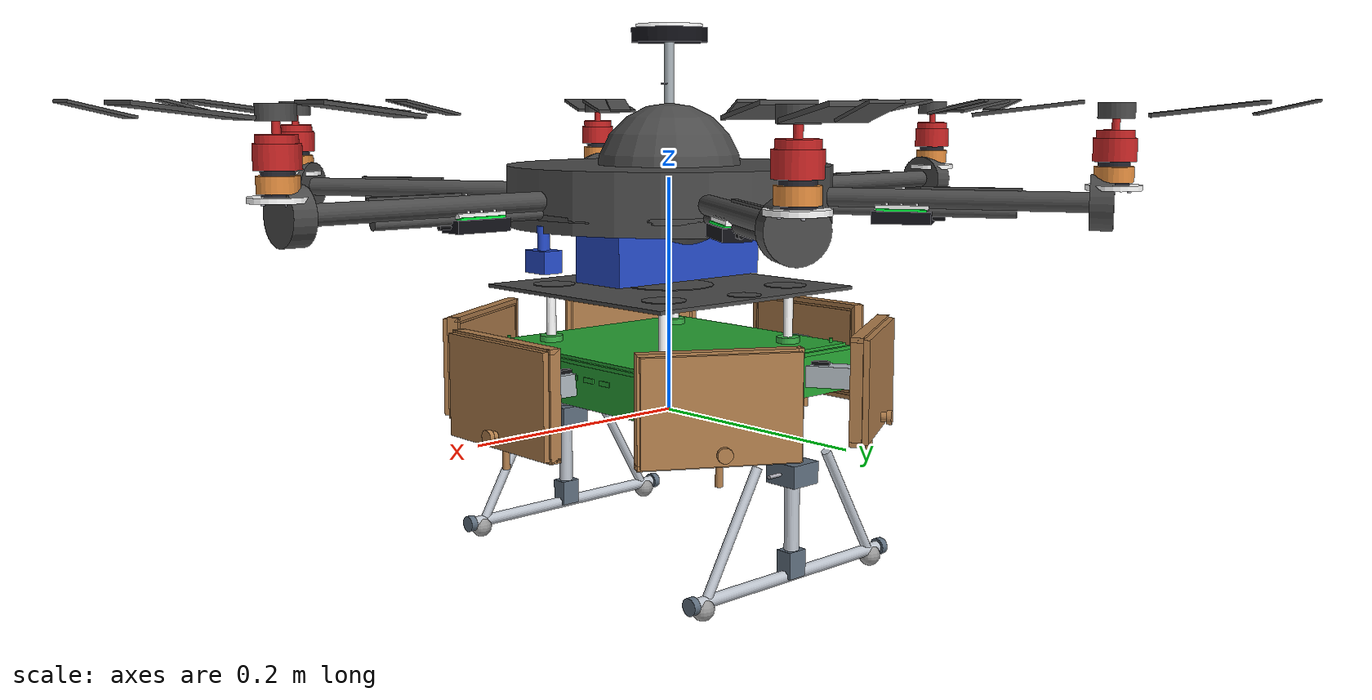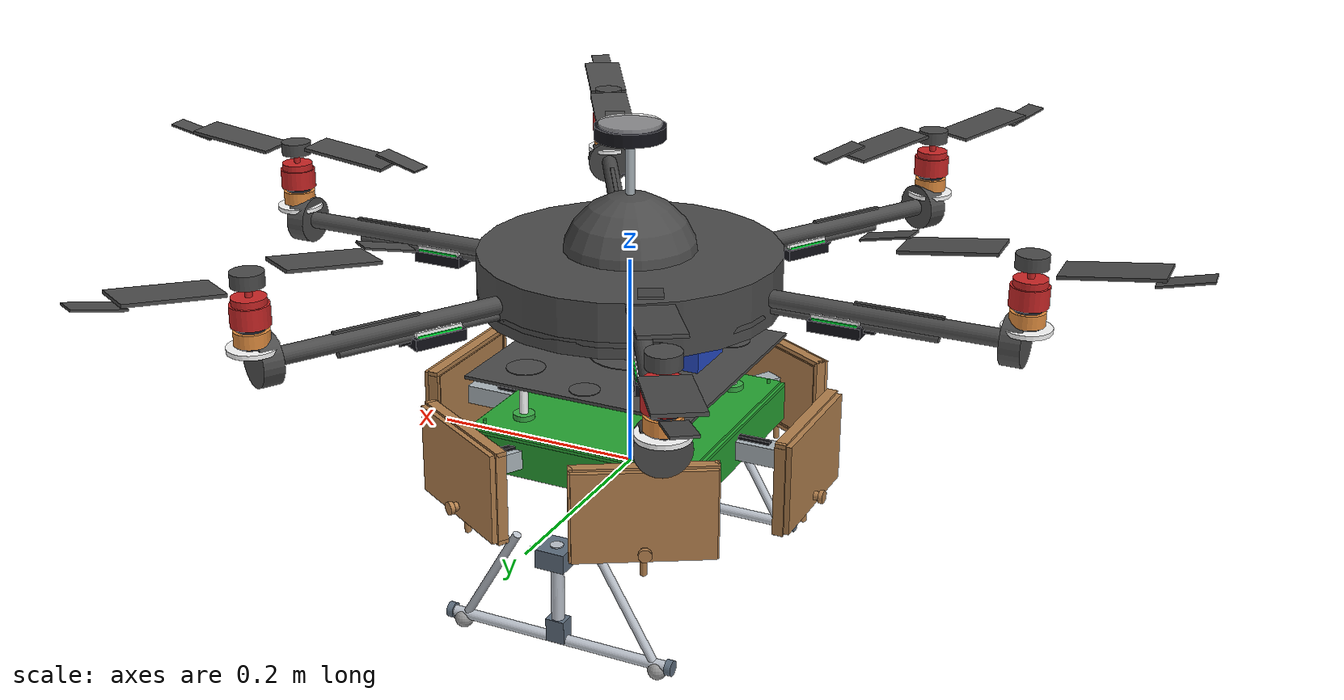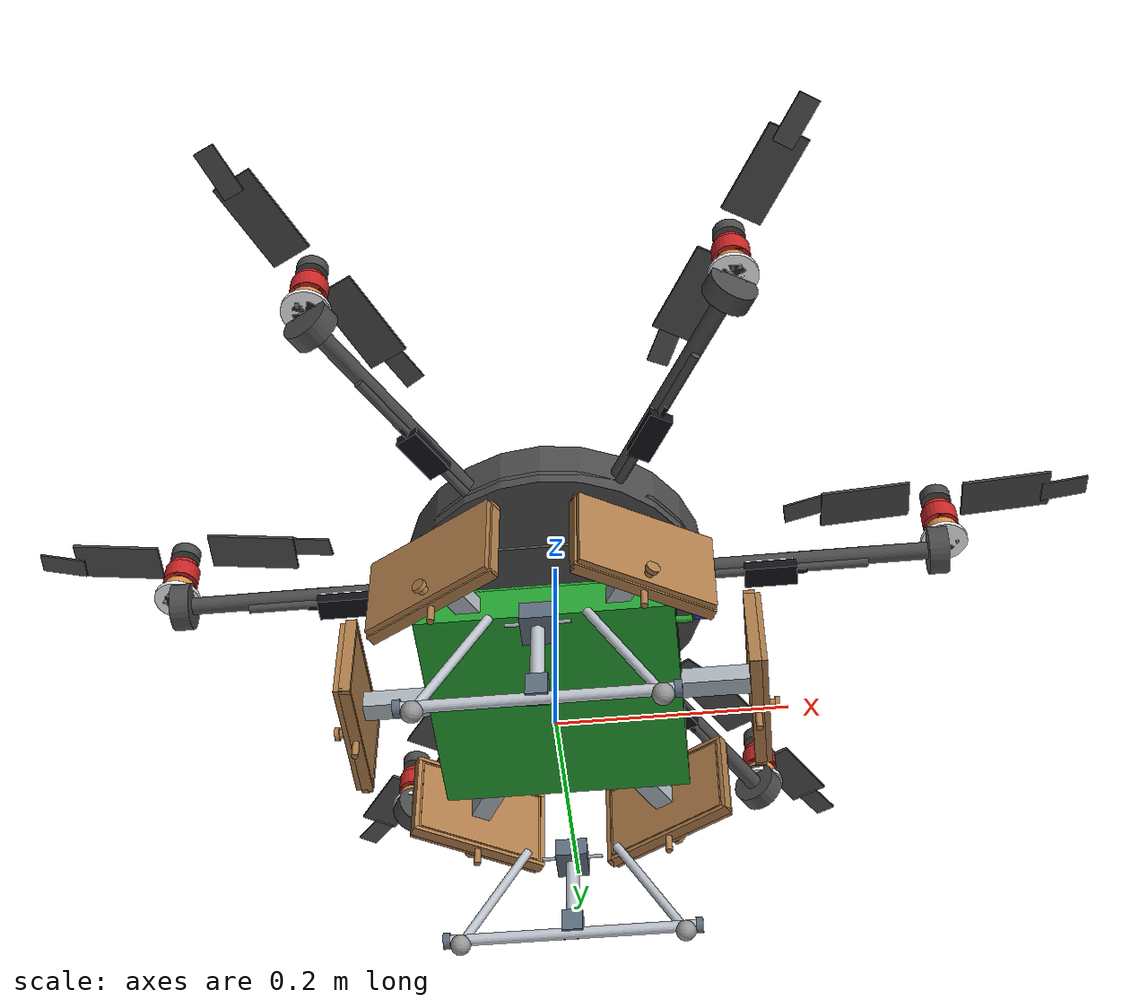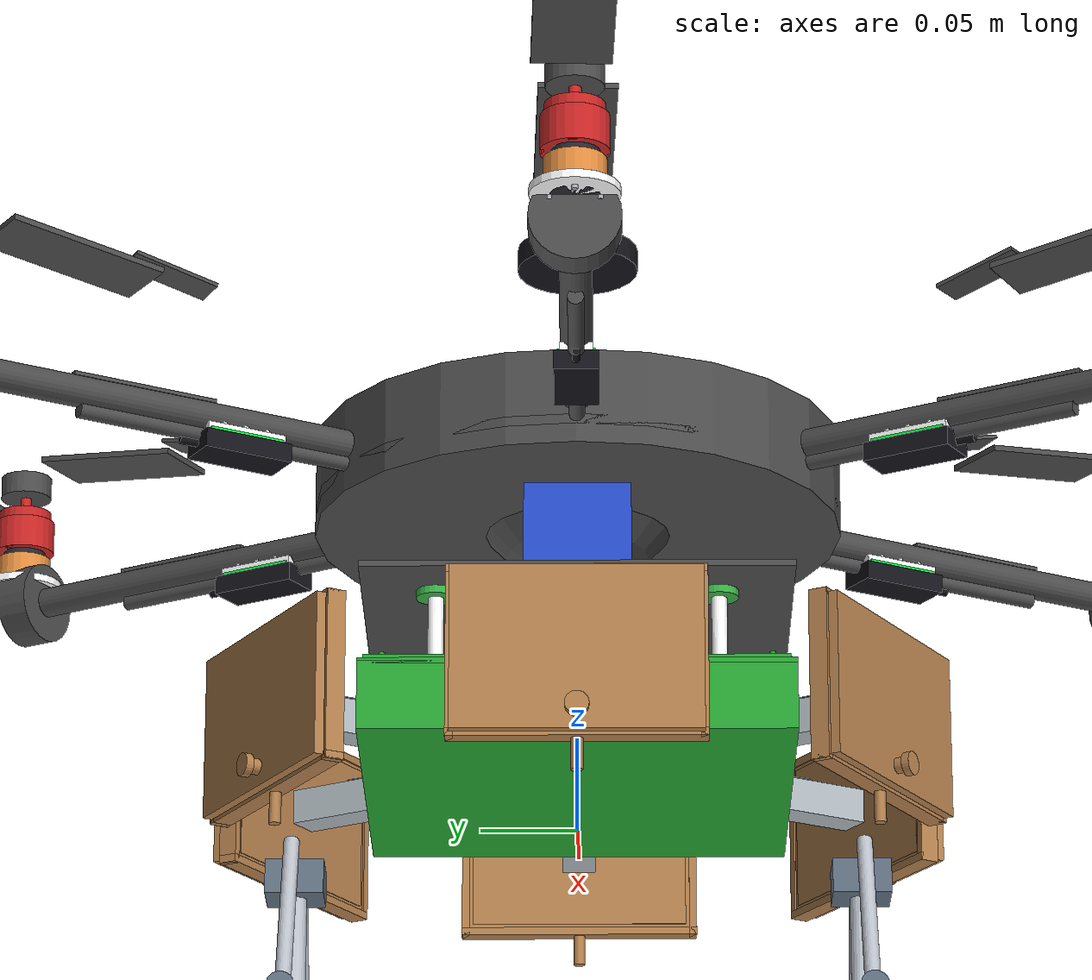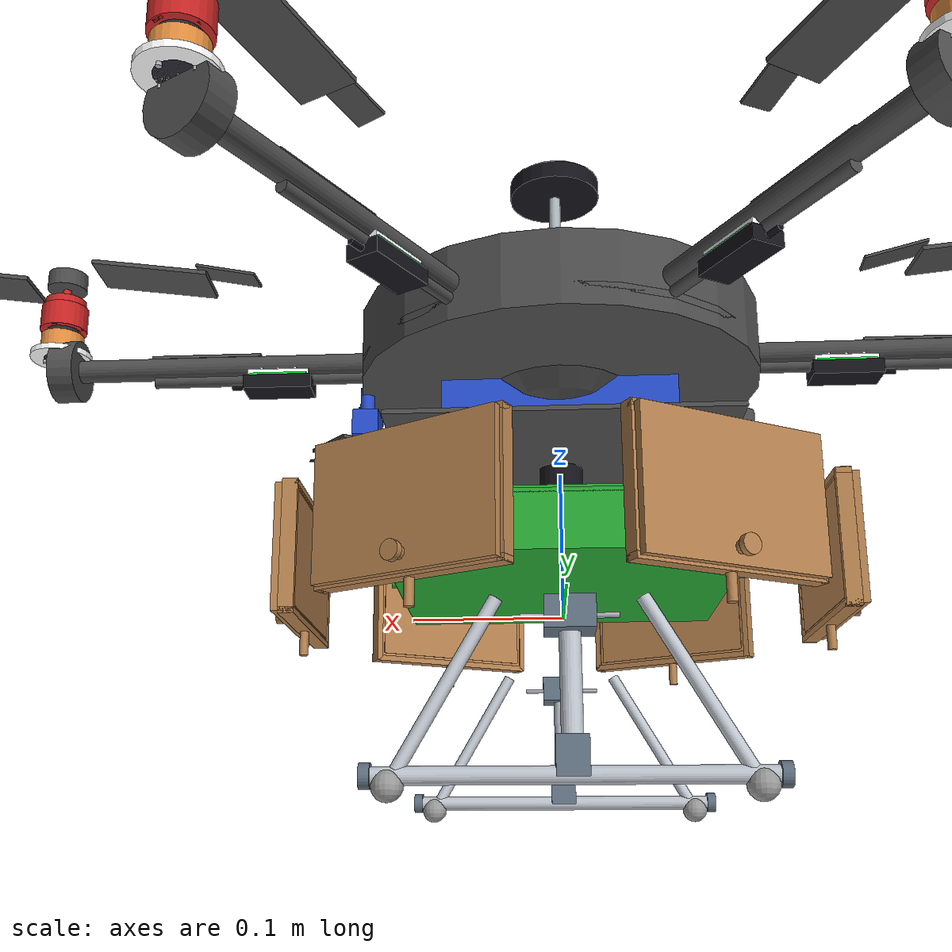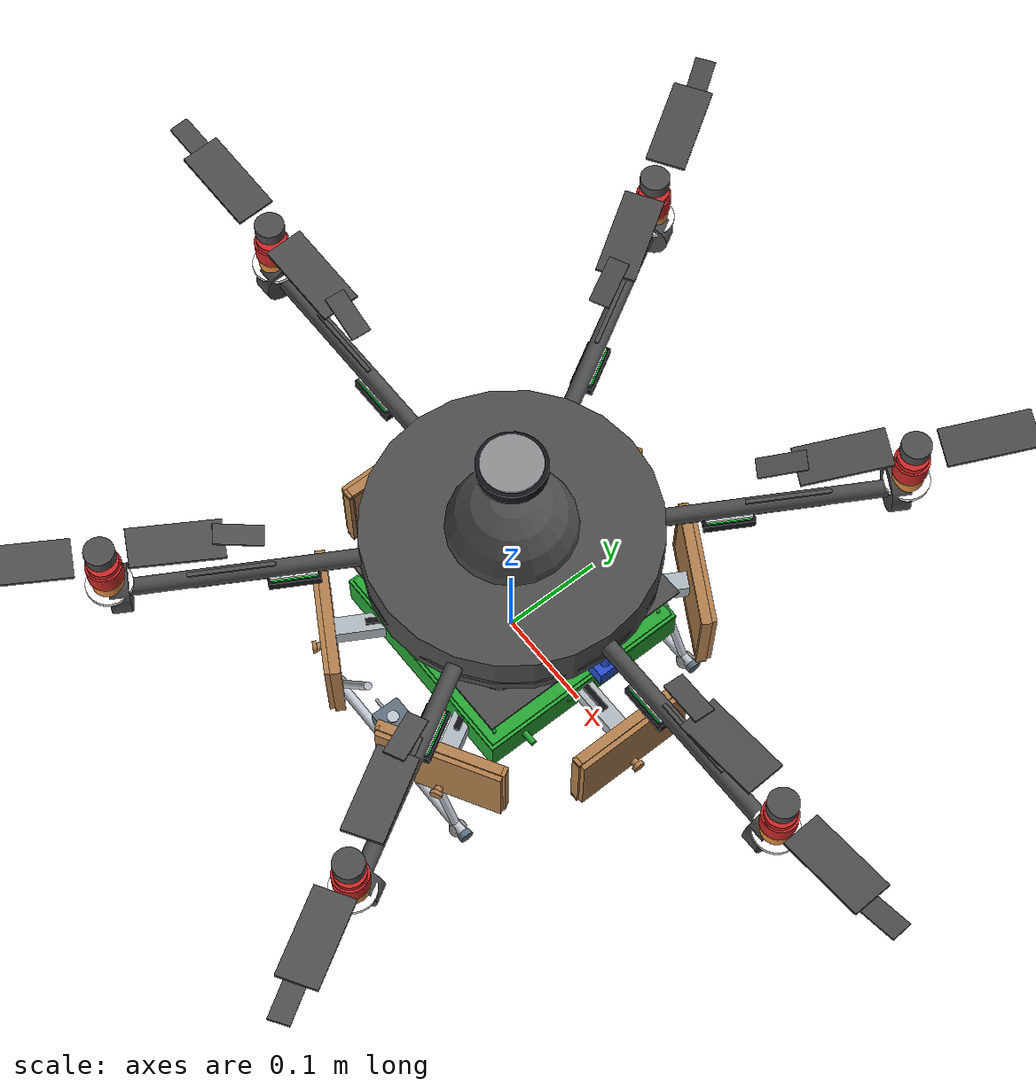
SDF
<sdf version='1.11'>
  <model name='mbc3_radar_drone'>
    <link name='base_link'>
      <inertial>
        <pose>0.0001455361101692728 -0.00044782347878249648 0.1120409613729428 0 0 0</pose>
        <mass>3.8341000000000012</mass>
        <inertia>
          <ixx>0.066852326243485097</ixx>
          <ixy>0</ixy>
          <ixz>0</ixz>
          <iyy>0.066852326243485097</iyy>
          <iyz>0</iyz>
          <izz>0.088652869552937469</izz>
        </inertia>
      </inertial>
      <collision name='base_link_fixed_joint_lump__body_hub_collision'>
        <pose>0 0 0.1865 0 0 0</pose>
        <geometry>
          <cylinder>
            <length>0.050000000000000003</length>
            <radius>0.13800000000000001</radius>
          </cylinder>
        </geometry>
        <surface>
          <contact>
            <ode/>
          </contact>
          <friction>
            <ode>
              <mu>0.80000000000000004</mu>
              <mu2>0.80000000000000004</mu2>
            </ode>
          </friction>
        </surface>
      </collision>
      <collision name='base_link_fixed_joint_lump__arm_0_collision_1'>
        <pose>0.17999999999999999 0 0.1865 0 1.5707963267948966 0</pose>
        <geometry>
          <cylinder>
            <length>0.35999999999999999</length>
            <radius>0.0080000000000000002</radius>
          </cylinder>
        </geometry>
        <surface>
          <contact>
            <ode/>
          </contact>
          <friction>
            <ode/>
          </friction>
        </surface>
      </collision>
      <collision name='base_link_fixed_joint_lump__esc_0_collision_2'>
        <pose>0.19800000000000001 0 0.17150000000000001 0 0 0</pose>
        <geometry>
          <box>
            <size>0.048000000000000001 0.021999999999999999 0.01</size>
          </box>
        </geometry>
      </collision>
      <collision name='base_link_fixed_joint_lump__motor_stator_0_collision_3'>
        <pose>0.35999999999999999 0 0.20749999999999999 0 0 0</pose>
        <geometry>
          <cylinder>
            <length>0.021999999999999999</length>
            <radius>0.016500000000000001</radius>
          </cylinder>
        </geometry>
      </collision>
      <collision name='base_link_fixed_joint_lump__arm_1_collision_4'>
        <pose>0.090000000000000024 0.1558845726811989 0.1865 -1.0471975511965981 1.5707963267948966 0</pose>
        <geometry>
          <cylinder>
            <length>0.35999999999999999</length>
            <radius>0.0080000000000000002</radius>
          </cylinder>
        </geometry>
        <surface>
          <contact>
            <ode/>
          </contact>
          <friction>
            <ode/>
          </friction>
        </surface>
      </collision>
      <collision name='base_link_fixed_joint_lump__esc_1_collision_5'>
        <pose>0.099000000000000032 0.17147302994931879 0.17150000000000001 0 0 1.0471975511965981</pose>
        <geometry>
          <box>
            <size>0.048000000000000001 0.021999999999999999 0.01</size>
          </box>
        </geometry>
      </collision>
      <collision name='base_link_fixed_joint_lump__motor_stator_1_collision_6'>
        <pose>0.17999999999999999 0.31176914536239791 0.20749999999999999 0 0 1.0471975511965981</pose>
        <geometry>
          <cylinder>
            <length>0.021999999999999999</length>
            <radius>0.016500000000000001</radius>
          </cylinder>
        </geometry>
      </collision>
      <collision name='base_link_fixed_joint_lump__arm_2_collision_7'>
        <pose>-0.089999999999999969 0.15588457268119901 0.1865 -2.0943951023931948 1.5707963267948966 0</pose>
        <geometry>
          <cylinder>
            <length>0.35999999999999999</length>
            <radius>0.0080000000000000002</radius>
          </cylinder>
        </geometry>
        <surface>
          <contact>
            <ode/>
          </contact>
          <friction>
            <ode/>
          </friction>
        </surface>
      </collision>
      <collision name='base_link_fixed_joint_lump__esc_2_collision_8'>
        <pose>-0.098999999999999977 0.1714730299493189 0.17150000000000001 0 0 2.0943951023931948</pose>
        <geometry>
          <box>
            <size>0.048000000000000001 0.021999999999999999 0.01</size>
          </box>
        </geometry>
      </collision>
      <collision name='base_link_fixed_joint_lump__motor_stator_2_collision_9'>
        <pose>-0.17999999999999991 0.31176914536239791 0.20749999999999999 0 0 2.0943951023931948</pose>
        <geometry>
          <cylinder>
            <length>0.021999999999999999</length>
            <radius>0.016500000000000001</radius>
          </cylinder>
        </geometry>
      </collision>
      <collision name='base_link_fixed_joint_lump__arm_3_collision_10'>
        <pose>-0.17999999999999999 2.2043642384652361e-17 0.1865 -3.1415926535897931 1.5707963267948966 0</pose>
        <geometry>
          <cylinder>
            <length>0.35999999999999999</length>
            <radius>0.0080000000000000002</radius>
          </cylinder>
        </geometry>
        <surface>
          <contact>
            <ode/>
          </contact>
          <friction>
            <ode/>
          </friction>
        </surface>
      </collision>
      <collision name='base_link_fixed_joint_lump__esc_3_collision_11'>
        <pose>-0.19800000000000001 2.4248006623117601e-17 0.17150000000000001 0 0 3.1415926535897931</pose>
        <geometry>
          <box>
            <size>0.048000000000000001 0.021999999999999999 0.01</size>
          </box>
        </geometry>
      </collision>
      <collision name='base_link_fixed_joint_lump__motor_stator_3_collision_12'>
        <pose>-0.35999999999999999 4.4087284769304723e-17 0.20749999999999999 0 0 3.1415926535897931</pose>
        <geometry>
          <cylinder>
            <length>0.021999999999999999</length>
            <radius>0.016500000000000001</radius>
          </cylinder>
        </geometry>
      </collision>
      <collision name='base_link_fixed_joint_lump__arm_4_collision_13'>
        <pose>-0.090000000000000135 -0.1558845726811989 0.1865 2.0943951023931948 1.5707963267948966 0</pose>
        <geometry>
          <cylinder>
            <length>0.35999999999999999</length>
            <radius>0.0080000000000000002</radius>
          </cylinder>
        </geometry>
        <surface>
          <contact>
            <ode/>
          </contact>
          <friction>
            <ode/>
          </friction>
        </surface>
      </collision>
      <collision name='base_link_fixed_joint_lump__esc_4_collision_14'>
        <pose>-0.099000000000000143 -0.17147302994931879 0.17150000000000001 0 0 -2.0943951023931962</pose>
        <geometry>
          <box>
            <size>0.048000000000000001 0.021999999999999999 0.01</size>
          </box>
        </geometry>
      </collision>
      <collision name='base_link_fixed_joint_lump__motor_stator_4_collision_15'>
        <pose>-0.1800000000000003 -0.31176914536239791 0.20749999999999999 0 0 -2.0943951023931962</pose>
        <geometry>
          <cylinder>
            <length>0.021999999999999999</length>
            <radius>0.016500000000000001</radius>
          </cylinder>
        </geometry>
      </collision>
      <collision name='base_link_fixed_joint_lump__arm_5_collision_16'>
        <pose>0.090000000000000024 -0.1558845726811989 0.1865 1.0471975511965976 1.5707963267948966 0</pose>
        <geometry>
          <cylinder>
            <length>0.35999999999999999</length>
            <radius>0.0080000000000000002</radius>
          </cylinder>
        </geometry>
        <surface>
          <contact>
            <ode/>
          </contact>
          <friction>
            <ode/>
          </friction>
        </surface>
      </collision>
      <collision name='base_link_fixed_joint_lump__esc_5_collision_17'>
        <pose>0.099000000000000032 -0.17147302994931879 0.17150000000000001 0 0 -1.0471975511965981</pose>
        <geometry>
          <box>
            <size>0.048000000000000001 0.021999999999999999 0.01</size>
          </box>
        </geometry>
      </collision>
      <collision name='base_link_fixed_joint_lump__motor_stator_5_collision_18'>
        <pose>0.17999999999999999 -0.31176914536239791 0.20749999999999999 0 0 -1.0471975511965981</pose>
        <geometry>
          <cylinder>
            <length>0.021999999999999999</length>
            <radius>0.016500000000000001</radius>
          </cylinder>
        </geometry>
      </collision>
      <collision name='base_link_fixed_joint_lump__battery_collision_19'>
        <pose>0 0 0.13900000000000001 0 0 0</pose>
        <geometry>
          <box>
            <size>0.170 0.065 0.055</size>
          </box>
        </geometry>
        <surface>
          <contact>
            <ode/>
          </contact>
          <friction>
            <ode/>
          </friction>
        </surface>
      </collision>
      <collision name='base_link_fixed_joint_lump__lg_post_L_collision_20'>
        <pose>0 0.14499999999999999 -0.090 0 0 0</pose>
        <geometry>
          <cylinder>
            <length>0.145</length>
            <radius>0.0080000000000000002</radius>
          </cylinder>
        </geometry>
      </collision>
      <collision name='base_link_fixed_joint_lump__lg_skid_L_collision_21'>
        <pose>0 0.14499999999999999 -0.172 0 1.5707963267948966 0</pose>
        <geometry>
          <cylinder>
            <length>0.22</length>
            <radius>0.014</radius>
          </cylinder>
        </geometry>
        <surface>
          <contact>
            <ode>
              <kp>1000000</kp>
              <kd>100</kd>
              <max_vel>0.5</max_vel>
              <min_depth>0.001</min_depth>
            </ode>
          </contact>
          <friction>
            <ode>
              <mu>1.8</mu>
              <mu2>1.8</mu2>
            </ode>
          </friction>
        </surface>
      </collision>
      <collision name='base_link_fixed_joint_lump__lg_post_R_collision_22'>
        <pose>0 -0.14499999999999999 -0.090 0 0 0</pose>
        <geometry>
          <cylinder>
            <length>0.145</length>
            <radius>0.0080000000000000002</radius>
          </cylinder>
        </geometry>
      </collision>
      <collision name='base_link_fixed_joint_lump__lg_skid_R_collision_23'>
        <pose>0 -0.14499999999999999 -0.172 0 1.5707963267948966 0</pose>
        <geometry>
          <cylinder>
            <length>0.22</length>
            <radius>0.014</radius>
          </cylinder>
        </geometry>
        <surface>
          <contact>
            <ode>
              <kp>1000000</kp>
              <kd>100</kd>
              <max_vel>0.5</max_vel>
              <min_depth>0.001</min_depth>
            </ode>
          </contact>
          <friction>
            <ode>
              <mu>1.8</mu>
              <mu2>1.8</mu2>
            </ode>
          </friction>
        </surface>
      </collision>
      <collision name='base_link_fixed_joint_lump__lg_support_front_L_collision_24'>
        <pose>0.067500000000000004 0.14499999999999999 -0.095 0 -0.34220 0</pose>
        <geometry>
          <cylinder>
            <length>0.1635</length>
            <radius>0.0050000000000000001</radius>
          </cylinder>
        </geometry>
      </collision>
      <collision name='base_link_fixed_joint_lump__lg_support_front_R_collision_25'>
        <pose>0.067500000000000004 -0.14499999999999999 -0.095 0 -0.34220 0</pose>
        <geometry>
          <cylinder>
            <length>0.1635</length>
            <radius>0.0050000000000000001</radius>
          </cylinder>
        </geometry>
      </collision>
      <collision name='base_link_fixed_joint_lump__lg_support_rear_L_collision_26'>
        <pose>-0.067500000000000004 0.14499999999999999 -0.095 0 0.34220 0</pose>
        <geometry>
          <cylinder>
            <length>0.1635</length>
            <radius>0.0050000000000000001</radius>
          </cylinder>
        </geometry>
      </collision>
      <collision name='base_link_fixed_joint_lump__lg_support_rear_R_collision_27'>
        <pose>-0.067500000000000004 -0.14499999999999999 -0.095 0 0.34220 0</pose>
        <geometry>
          <cylinder>
            <length>0.1635</length>
            <radius>0.0050000000000000001</radius>
          </cylinder>
        </geometry>
      </collision>
      <collision name='base_link_fixed_joint_lump__bottom_plate_collision_28'>
        <pose>0 0 0.107 0 0 0</pose>
        <geometry>
          <box>
            <size>0.22 0.22 0.0030000000000000001</size>
          </box>
        </geometry>
        <surface>
          <contact>
            <ode/>
          </contact>
          <friction>
            <ode/>
          </friction>
        </surface>
      </collision>
      <collision name='base_link_fixed_joint_lump__radar_box_collision_29'>
        <pose>0 0 0.037499999999999978 0 0 0</pose>
        <geometry>
          <box>
            <size>0.23599999999999999 0.23599999999999999 0.045999999999999999</size>
          </box>
        </geometry>
        <surface>
          <contact>
            <ode/>
          </contact>
          <friction>
            <ode/>
          </friction>
        </surface>
      </collision>
      <collision name='base_link_fixed_joint_lump__panel_arm_A_collision_30'>
        <pose>0.14000000000000001 0 0.037499999999999978 0 0 0</pose>
        <geometry>
          <box>
            <size>0.059999999999999998 0.017999999999999999 0.017999999999999999</size>
          </box>
        </geometry>
      </collision>
      <collision name='base_link_fixed_joint_lump__antenna_panel_A_collision_31'>
        <pose>0.18049999999999999 0 0.037499999999999978 0 0 0</pose>
        <geometry>
          <box>
            <size>0.014999999999999999 0.13200000000000001 0.091999999999999998</size>
          </box>
        </geometry>
        <surface>
          <contact>
            <ode/>
          </contact>
          <friction>
            <ode/>
          </friction>
        </surface>
      </collision>
      <collision name='base_link_fixed_joint_lump__panel_arm_B_collision_32'>
        <pose>0.070000000000000021 0.1212435565298214 0.037499999999999978 0 0 1.0471975511965981</pose>
        <geometry>
          <box>
            <size>0.059999999999999998 0.017999999999999999 0.017999999999999999</size>
          </box>
        </geometry>
      </collision>
      <collision name='base_link_fixed_joint_lump__antenna_panel_B_collision_33'>
        <pose>0.090250000000000025 0.15631758538309121 0.037499999999999978 0 0 1.0471975511965981</pose>
        <geometry>
          <box>
            <size>0.014999999999999999 0.13200000000000001 0.091999999999999998</size>
          </box>
        </geometry>
        <surface>
          <contact>
            <ode/>
          </contact>
          <friction>
            <ode/>
          </friction>
        </surface>
      </collision>
      <collision name='base_link_fixed_joint_lump__panel_arm_C_collision_34'>
        <pose>-0.069999999999999965 0.1212435565298214 0.037499999999999978 0 0 2.0943951023931948</pose>
        <geometry>
          <box>
            <size>0.059999999999999998 0.017999999999999999 0.017999999999999999</size>
          </box>
        </geometry>
      </collision>
      <collision name='base_link_fixed_joint_lump__antenna_panel_C_collision_35'>
        <pose>-0.090249999999999969 0.15631758538309121 0.037499999999999978 0 0 2.0943951023931948</pose>
        <geometry>
          <box>
            <size>0.014999999999999999 0.13200000000000001 0.091999999999999998</size>
          </box>
        </geometry>
        <surface>
          <contact>
            <ode/>
          </contact>
          <friction>
            <ode/>
          </friction>
        </surface>
      </collision>
      <collision name='base_link_fixed_joint_lump__panel_arm_D_collision_36'>
        <pose>-0.14000000000000001 1.7145055188062941e-17 0.037499999999999978 0 0 3.1415926535897931</pose>
        <geometry>
          <box>
            <size>0.059999999999999998 0.017999999999999999 0.017999999999999999</size>
          </box>
        </geometry>
      </collision>
      <collision name='base_link_fixed_joint_lump__antenna_panel_D_collision_37'>
        <pose>-0.18049999999999999 2.2104874724609729e-17 0.037499999999999978 0 0 3.1415926535897931</pose>
        <geometry>
          <box>
            <size>0.014999999999999999 0.13200000000000001 0.091999999999999998</size>
          </box>
        </geometry>
        <surface>
          <contact>
            <ode/>
          </contact>
          <friction>
            <ode/>
          </friction>
        </surface>
      </collision>
      <collision name='base_link_fixed_joint_lump__panel_arm_E_collision_38'>
        <pose>-0.070000000000000062 -0.1212435565298214 0.037499999999999978 0 0 -2.0943951023931962</pose>
        <geometry>
          <box>
            <size>0.059999999999999998 0.017999999999999999 0.017999999999999999</size>
          </box>
        </geometry>
      </collision>
      <collision name='base_link_fixed_joint_lump__antenna_panel_E_collision_39'>
        <pose>-0.090250000000000094 -0.15631758538309121 0.037499999999999978 0 0 -2.0943951023931962</pose>
        <geometry>
          <box>
            <size>0.014999999999999999 0.13200000000000001 0.091999999999999998</size>
          </box>
        </geometry>
        <surface>
          <contact>
            <ode/>
          </contact>
          <friction>
            <ode/>
          </friction>
        </surface>
      </collision>
      <collision name='base_link_fixed_joint_lump__panel_arm_F_collision_40'>
        <pose>0.070000000000000021 -0.1212435565298214 0.037499999999999978 0 0 -1.0471975511965981</pose>
        <geometry>
          <box>
            <size>0.059999999999999998 0.017999999999999999 0.017999999999999999</size>
          </box>
        </geometry>
      </collision>
      <collision name='base_link_fixed_joint_lump__antenna_panel_F_collision_41'>
        <pose>0.090250000000000025 -0.15631758538309121 0.037499999999999978 0 0 -1.0471975511965981</pose>
        <geometry>
          <box>
            <size>0.014999999999999999 0.13200000000000001 0.091999999999999998</size>
          </box>
        </geometry>
        <surface>
          <contact>
            <ode/>
          </contact>
          <friction>
            <ode/>
          </friction>
        </surface>
      </collision>
      <collision name='base_link_fixed_joint_lump__standoff_fl_collision_42'>
        <pose>0.071999999999999995 0.071999999999999995 0.08299999999999999 0 0 0</pose>
        <geometry>
          <cylinder>
            <length>0.044999999999999998</length>
            <radius>0.0040000000000000001</radius>
          </cylinder>
        </geometry>
      </collision>
      <collision name='base_link_fixed_joint_lump__standoff_fr_collision_43'>
        <pose>0.071999999999999995 -0.071999999999999995 0.08299999999999999 0 0 0</pose>
        <geometry>
          <cylinder>
            <length>0.044999999999999998</length>
            <radius>0.0040000000000000001</radius>
          </cylinder>
        </geometry>
      </collision>
      <collision name='base_link_fixed_joint_lump__standoff_rl_collision_44'>
        <pose>-0.071999999999999995 0.071999999999999995 0.08299999999999999 0 0 0</pose>
        <geometry>
          <cylinder>
            <length>0.044999999999999998</length>
            <radius>0.0040000000000000001</radius>
          </cylinder>
        </geometry>
      </collision>
      <collision name='base_link_fixed_joint_lump__standoff_rr_collision_45'>
        <pose>-0.071999999999999995 -0.071999999999999995 0.08299999999999999 0 0 0</pose>
        <geometry>
          <cylinder>
            <length>0.044999999999999998</length>
            <radius>0.0040000000000000001</radius>
          </cylinder>
        </geometry>
      </collision>
      <visual name='base_link_fixed_joint_lump__body_hub_visual'>
        <pose>0 0 0.1865 0 0 0</pose>
        <geometry>
          <cylinder>
            <length>0.05</length>
            <radius>0.138</radius>
          </cylinder>
        </geometry>
        <material>
          <script>
            <name>Gazebo/DarkGrey</name>
            <uri>file://media/materials/scripts/gazebo.material</uri>
          </script>
          <diffuse>0.125 0.125 0.149999991 1</diffuse>
          <ambient>0.125 0.125 0.149999991 1</ambient>
        </material>
      </visual>
      <visual name='base_link_fixed_joint_lump__body_hub_visual_1'>
        <pose>0 0 0.20050000000000001 0 0 0</pose>
        <geometry>
          <sphere>
            <radius>0.0625</radius>
          </sphere>
        </geometry>
        <material>
          <script>
            <name>Gazebo/DarkGrey</name>
            <uri>file://media/materials/scripts/gazebo.material</uri>
          </script>
          <diffuse>0.187500015 0.187500015 0.225000009 1</diffuse>
          <ambient>0.187500015 0.187500015 0.225000009 1</ambient>
        </material>
      </visual>
      <visual name='base_link_fixed_joint_lump__body_hub_visual_2'>
        <pose>0 0 0.19750000000000001 0 0 0</pose>
        <geometry>
          <cylinder>
            <length>0.0030000000000000001</length>
            <radius>0.115</radius>
          </cylinder>
        </geometry>
        <material>
          <script>
            <name>Gazebo/DarkGrey</name>
            <uri>file://media/materials/scripts/gazebo.material</uri>
          </script>
          <diffuse>0.125 0.125 0.149999991 1</diffuse>
          <ambient>0.125 0.125 0.149999991 1</ambient>
        </material>
      </visual>
      <visual name='base_link_fixed_joint_lump__body_hub_visual_3'>
        <pose>0 0 0.19850000000000001 0 0 0</pose>
        <geometry>
          <cylinder>
            <length>0.0030000000000000001</length>
            <radius>0.035000000000000003</radius>
          </cylinder>
        </geometry>
        <material>
          <script>
            <name>Gazebo/DarkGrey</name>
            <uri>file://media/materials/scripts/gazebo.material</uri>
          </script>
          <diffuse>0 1 0.25 1</diffuse>
          <ambient>0 1 0.25 1</ambient>
        </material>
      </visual>
      <visual name='base_link_fixed_joint_lump__body_hub_visual_4'>
        <pose>0 0 0.18149999999999999 0 0 0</pose>
        <geometry>
          <cylinder>
            <length>0.0040000000000000001</length>
            <radius>0.089999999999999997</radius>
          </cylinder>
        </geometry>
        <material>
          <script>
            <name>Gazebo/DarkGrey</name>
            <uri>file://media/materials/scripts/gazebo.material</uri>
          </script>
          <diffuse>0.900000036 0.724999964 0.400000006 1</diffuse>
          <ambient>0.900000036 0.724999964 0.400000006 1</ambient>
        </material>
      </visual>
      <visual name='base_link_fixed_joint_lump__body_hub_visual_5'>
        <pose>0.12 0 0.18149999999999999 0 1.5707963267948966 0</pose>
        <geometry>
          <box>
            <size>0.014 0.021999999999999999 0.016</size>
          </box>
        </geometry>
        <material>
          <script>
            <name>Gazebo/DarkGrey</name>
            <uri>file://media/materials/scripts/gazebo.material</uri>
          </script>
          <diffuse>0.0749999955 0.0749999955 0.099999994 1</diffuse>
          <ambient>0.0749999955 0.0749999955 0.099999994 1</ambient>
        </material>
      </visual>
      <visual name='base_link_fixed_joint_lump__body_hub_visual_6'>
        <pose>0 0 0.17399999999999999 0 0 0</pose>
        <geometry>
          <cylinder>
            <length>0.0050000000000000001</length>
            <radius>0.13800000000000001</radius>
          </cylinder>
        </geometry>
        <material>
          <script>
            <name>Gazebo/DarkGrey</name>
            <uri>file://media/materials/scripts/gazebo.material</uri>
          </script>
          <diffuse>1 1 1 1</diffuse>
          <ambient>1 1 1 1</ambient>
        </material>
      </visual>
      <visual name='base_link_fixed_joint_lump__body_hub_visual_7'>
        <pose>0.11749999999999999 0 0.1865 0 1.5707963267948966 0</pose>
        <geometry>
          <cylinder>
            <length>0.016</length>
            <radius>0.014999999999999999</radius>
          </cylinder>
        </geometry>
        <material>
          <script>
            <name>Gazebo/DarkGrey</name>
            <uri>file://media/materials/scripts/gazebo.material</uri>
          </script>
          <diffuse>0.6875 0.724999964 0.75000006 1</diffuse>
          <ambient>0.6875 0.724999964 0.75000006 1</ambient>
        </material>
      </visual>
      <visual name='base_link_fixed_joint_lump__body_hub_visual_8'>
        <pose>0.058749999999999997 0.101755 0.1865 0 1.5707963267948966 0</pose>
        <geometry>
          <cylinder>
            <length>0.016</length>
            <radius>0.014999999999999999</radius>
          </cylinder>
        </geometry>
        <material>
          <script>
            <name>Gazebo/DarkGrey</name>
            <uri>file://media/materials/scripts/gazebo.material</uri>
          </script>
          <diffuse>0.6875 0.724999964 0.75000006 1</diffuse>
          <ambient>0.6875 0.724999964 0.75000006 1</ambient>
        </material>
      </visual>
      <visual name='base_link_fixed_joint_lump__body_hub_visual_9'>
        <pose>-0.058749999999999997 0.101755 0.1865 0 1.5707963267948966 0</pose>
        <geometry>
          <cylinder>
            <length>0.016</length>
            <radius>0.014999999999999999</radius>
          </cylinder>
        </geometry>
        <material>
          <script>
            <name>Gazebo/DarkGrey</name>
            <uri>file://media/materials/scripts/gazebo.material</uri>
          </script>
          <diffuse>0.6875 0.724999964 0.75000006 1</diffuse>
          <ambient>0.6875 0.724999964 0.75000006 1</ambient>
        </material>
      </visual>
      <visual name='base_link_fixed_joint_lump__body_hub_visual_10'>
        <pose>-0.11749999999999999 0 0.1865 0 1.5707963267948966 0</pose>
        <geometry>
          <cylinder>
            <length>0.016</length>
            <radius>0.014999999999999999</radius>
          </cylinder>
        </geometry>
        <material>
          <script>
            <name>Gazebo/DarkGrey</name>
            <uri>file://media/materials/scripts/gazebo.material</uri>
          </script>
          <diffuse>0.6875 0.724999964 0.75000006 1</diffuse>
          <ambient>0.6875 0.724999964 0.75000006 1</ambient>
        </material>
      </visual>
      <visual name='base_link_fixed_joint_lump__body_hub_visual_11'>
        <pose>-0.058749999999999997 -0.101755 0.1865 0 1.5707963267948966 0</pose>
        <geometry>
          <cylinder>
            <length>0.016</length>
            <radius>0.014999999999999999</radius>
          </cylinder>
        </geometry>
        <material>
          <script>
            <name>Gazebo/DarkGrey</name>
            <uri>file://media/materials/scripts/gazebo.material</uri>
          </script>
          <diffuse>0.6875 0.724999964 0.75000006 1</diffuse>
          <ambient>0.6875 0.724999964 0.75000006 1</ambient>
        </material>
      </visual>
      <visual name='base_link_fixed_joint_lump__body_hub_visual_12'>
        <pose>0.058749999999999997 -0.101755 0.1865 0 1.5707963267948966 0</pose>
        <geometry>
          <cylinder>
            <length>0.016</length>
            <radius>0.014999999999999999</radius>
          </cylinder>
        </geometry>
        <material>
          <script>
            <name>Gazebo/DarkGrey</name>
            <uri>file://media/materials/scripts/gazebo.material</uri>
          </script>
          <diffuse>0.6875 0.724999964 0.75000006 1</diffuse>
          <ambient>0.6875 0.724999964 0.75000006 1</ambient>
        </material>
      </visual>
      <visual name='base_link_fixed_joint_lump__arm_0_visual_13'>
        <pose>0.17999999999999999 0 0.1865 0 1.5707963267948966 0</pose>
        <geometry>
          <cylinder>
            <length>0.35999999999999999</length>
            <radius>0.0080000000000000002</radius>
          </cylinder>
        </geometry>
        <material>
          <script>
            <name>Gazebo/DarkGrey</name>
            <uri>file://media/materials/scripts/gazebo.material</uri>
          </script>
          <diffuse>0.125 0.125 0.149999991 1</diffuse>
          <ambient>0.125 0.125 0.149999991 1</ambient>
        </material>
      </visual>
      <visual name='base_link_fixed_joint_lump__arm_0_visual_14'>
        <pose>0.17999999999999999 0 0.1865 0 1.5707963267948966 0</pose>
        <geometry>
          <cylinder>
            <length>0.35399999999999998</length>
            <radius>0.0060000000000000001</radius>
          </cylinder>
        </geometry>
        <material>
          <script>
            <name>Gazebo/DarkGrey</name>
            <uri>file://media/materials/scripts/gazebo.material</uri>
          </script>
          <diffuse>0.25 0.25 0.3125 0.300000012</diffuse>
          <ambient>0.25 0.25 0.3125 0.300000012</ambient>
        </material>
      </visual>
      <visual name='base_link_fixed_joint_lump__arm_0_visual_15'>
        <pose>0.35199999999999998 0 0.1865 0 1.5707963267948966 0</pose>
        <geometry>
          <cylinder>
            <length>0.017999999999999999</length>
            <radius>0.021999999999999999</radius>
          </cylinder>
        </geometry>
        <material>
          <script>
            <name>Gazebo/DarkGrey</name>
            <uri>file://media/materials/scripts/gazebo.material</uri>
          </script>
          <diffuse>0.6875 0.724999964 0.75000006 1</diffuse>
          <ambient>0.6875 0.724999964 0.75000006 1</ambient>
        </material>
      </visual>
      <visual name='base_link_fixed_joint_lump__arm_0_visual_16'>
        <pose>0.0080000000000000002 0 0.1865 0 1.5707963267948966 0</pose>
        <geometry>
          <cylinder>
            <length>0.017999999999999999</length>
            <radius>0.021999999999999999</radius>
          </cylinder>
        </geometry>
        <material>
          <script>
            <name>Gazebo/DarkGrey</name>
            <uri>file://media/materials/scripts/gazebo.material</uri>
          </script>
          <diffuse>0.6875 0.724999964 0.75000006 1</diffuse>
          <ambient>0.6875 0.724999964 0.75000006 1</ambient>
        </material>
      </visual>
      <visual name='base_link_fixed_joint_lump__arm_0_visual_17'>
        <pose>0.17999999999999999 0 0.17649999999999999 0 1.5707963267948966 0</pose>
        <geometry>
          <cylinder>
            <length>0.216</length>
            <radius>0.0040000000000000001</radius>
          </cylinder>
        </geometry>
        <material>
          <script>
            <name>Gazebo/DarkGrey</name>
            <uri>file://media/materials/scripts/gazebo.material</uri>
          </script>
          <diffuse>1 0.125 0.125 1</diffuse>
          <ambient>1 0.125 0.125 1</ambient>
        </material>
      </visual>
      <visual name='base_link_fixed_joint_lump__arm_0_visual_18'>
        <pose>0.252 0 0.19550000000000001 0 0 0</pose>
        <geometry>
          <box>
            <size>0.079199999999999993 0.0040000000000000001 0.002</size>
          </box>
        </geometry>
        <material>
          <script>
            <name>Gazebo/DarkGrey</name>
            <uri>file://media/materials/scripts/gazebo.material</uri>
          </script>
          <diffuse>0 1 0.25 1</diffuse>
          <ambient>0 1 0.25 1</ambient>
        </material>
      </visual>
      <visual name='base_link_fixed_joint_lump__esc_0_visual_19'>
        <pose>0.19800000000000001 0 0.17150000000000001 0 0 0</pose>
        <geometry>
          <box>
            <size>0.048000000000000001 0.021999999999999999 0.01</size>
          </box>
        </geometry>
        <material>
          <diffuse>0.0749999955 0.0749999955 0.099999994 1</diffuse>
          <ambient>0.0749999955 0.0749999955 0.099999994 1</ambient>
        </material>
      </visual>
      <visual name='base_link_fixed_joint_lump__esc_0_visual_20'>
        <pose>0.19800000000000001 0 0.17749999999999999 0 0 0</pose>
        <geometry>
          <box>
            <size>0.040800000000000003 0.018700000000000001 0.002</size>
          </box>
        </geometry>
        <material>
          <diffuse>0 1 0.25 1</diffuse>
          <ambient>0 1 0.25 1</ambient>
        </material>
      </visual>
      <visual name='base_link_fixed_joint_lump__esc_0_visual_21'>
        <pose>0.19800000000000001 0 0.17949999999999999 0 0 0</pose>
        <geometry>
          <box>
            <size>0.043200000000000002 0.016500000000000001 0.0040000000000000001</size>
          </box>
        </geometry>
        <material>
          <diffuse>1 1 1 1</diffuse>
          <ambient>1 1 1 1</ambient>
        </material>
      </visual>
      <visual name='base_link_fixed_joint_lump__esc_0_visual_22'>
        <pose>0.186 0 0.1825 0 0 0</pose>
        <geometry>
          <box>
            <size>0.002 0.0143 0.0060000000000000001</size>
          </box>
        </geometry>
        <material>
          <diffuse>1 1 1 1</diffuse>
          <ambient>1 1 1 1</ambient>
        </material>
      </visual>
      <visual name='base_link_fixed_joint_lump__esc_0_visual_23'>
        <pose>0.19800000000000001 0 0.1825 0 0 0</pose>
        <geometry>
          <box>
            <size>0.002 0.0143 0.0060000000000000001</size>
          </box>
        </geometry>
        <material>
          <diffuse>1 1 1 1</diffuse>
          <ambient>1 1 1 1</ambient>
        </material>
      </visual>
      <visual name='base_link_fixed_joint_lump__esc_0_visual_24'>
        <pose>0.20999999999999999 0 0.1825 0 0 0</pose>
        <geometry>
          <box>
            <size>0.002 0.0143 0.0060000000000000001</size>
          </box>
        </geometry>
        <material>
          <diffuse>1 1 1 1</diffuse>
          <ambient>1 1 1 1</ambient>
        </material>
      </visual>
      <visual name='base_link_fixed_joint_lump__esc_0_visual_25'>
        <pose>0.22700000000000001 0 0.17150000000000001 0 1.5707963267948966 0</pose>
        <geometry>
          <cylinder>
            <length>0.01</length>
            <radius>0.002</radius>
          </cylinder>
        </geometry>
        <material>
          <diffuse>0.0625 0.0625 0.0749999955 1</diffuse>
          <ambient>0.0625 0.0625 0.0749999955 1</ambient>
        </material>
      </visual>
      <visual name='base_link_fixed_joint_lump__motor_stator_0_visual_26'>
        <pose>0.35999999999999999 0 0.20749999999999999 0 0 0</pose>
        <geometry>
          <cylinder>
            <length>0.021999999999999999</length>
            <radius>0.012</radius>
          </cylinder>
        </geometry>
        <material>
          <diffuse>0.149999991 0.149999991 0.187500015 1</diffuse>
          <ambient>0.149999991 0.149999991 0.187500015 1</ambient>
        </material>
      </visual>
      <visual name='base_link_fixed_joint_lump__motor_stator_0_visual_27'>
        <pose>0.35999999999999999 0 0.20860000000000001 0 0 0</pose>
        <geometry>
          <cylinder>
            <length>0.0121</length>
            <radius>0.014999999999999999</radius>
          </cylinder>
        </geometry>
        <material>
          <diffuse>0.900000036 0.5625 0.25 1</diffuse>
          <ambient>0.900000036 0.5625 0.25 1</ambient>
        </material>
      </visual>
      <visual name='base_link_fixed_joint_lump__motor_stator_0_visual_28'>
        <pose>0.35999999999999999 0 0.19850000000000001 0 0 0</pose>
        <geometry>
          <cylinder>
            <length>0.0040000000000000001</length>
            <radius>0.021499999999999998</radius>
          </cylinder>
        </geometry>
        <material>
          <diffuse>1 1 1 1</diffuse>
          <ambient>1 1 1 1</ambient>
        </material>
      </visual>
      <visual name='base_link_fixed_joint_lump__motor_stator_0_visual_29'>
        <pose>0.37187999999999999 0 0.19750000000000001 0 0 0</pose>
        <geometry>
          <cylinder>
            <length>0.0060000000000000001</length>
            <radius>0.0015</radius>
          </cylinder>
        </geometry>
        <material>
          <diffuse>0.6875 0.6875 0.724999964 1</diffuse>
          <ambient>0.6875 0.6875 0.724999964 1</ambient>
        </material>
      </visual>
      <visual name='base_link_fixed_joint_lump__motor_stator_0_visual_30'>
        <pose>0.34811999999999999 0 0.19750000000000001 0 0 0</pose>
        <geometry>
          <cylinder>
            <length>0.0060000000000000001</length>
            <radius>0.0015</radius>
          </cylinder>
        </geometry>
        <material>
          <diffuse>0.6875 0.6875 0.724999964 1</diffuse>
          <ambient>0.6875 0.6875 0.724999964 1</ambient>
        </material>
      </visual>
      <visual name='base_link_fixed_joint_lump__motor_stator_0_visual_31'>
        <pose>0.35999999999999999 0.01188 0.19750000000000001 0 0 0</pose>
        <geometry>
          <cylinder>
            <length>0.0060000000000000001</length>
            <radius>0.0015</radius>
          </cylinder>
        </geometry>
        <material>
          <diffuse>0.6875 0.6875 0.724999964 1</diffuse>
          <ambient>0.6875 0.6875 0.724999964 1</ambient>
        </material>
      </visual>
      <visual name='base_link_fixed_joint_lump__motor_stator_0_visual_32'>
        <pose>0.35999999999999999 -0.01188 0.19750000000000001 0 0 0</pose>
        <geometry>
          <cylinder>
            <length>0.0060000000000000001</length>
            <radius>0.0015</radius>
          </cylinder>
        </geometry>
        <material>
          <diffuse>0.6875 0.6875 0.724999964 1</diffuse>
          <ambient>0.6875 0.6875 0.724999964 1</ambient>
        </material>
      </visual>
      <visual name='base_link_fixed_joint_lump__arm_1_visual_33'>
        <pose>0.090000000000000024 0.1558845726811989 0.1865 -1.0471975511965981 1.5707963267948966 0</pose>
        <geometry>
          <cylinder>
            <length>0.35999999999999999</length>
            <radius>0.0080000000000000002</radius>
          </cylinder>
        </geometry>
        <material>
          <script>
            <name>Gazebo/DarkGrey</name>
            <uri>file://media/materials/scripts/gazebo.material</uri>
          </script>
          <diffuse>0.125 0.125 0.149999991 1</diffuse>
          <ambient>0.125 0.125 0.149999991 1</ambient>
        </material>
      </visual>
      <visual name='base_link_fixed_joint_lump__arm_1_visual_34'>
        <pose>0.090000000000000024 0.1558845726811989 0.1865 -1.0471975511965981 1.5707963267948966 0</pose>
        <geometry>
          <cylinder>
            <length>0.35399999999999998</length>
            <radius>0.0060000000000000001</radius>
          </cylinder>
        </geometry>
        <material>
          <script>
            <name>Gazebo/DarkGrey</name>
            <uri>file://media/materials/scripts/gazebo.material</uri>
          </script>
          <diffuse>0.25 0.25 0.3125 0.300000012</diffuse>
          <ambient>0.25 0.25 0.3125 0.300000012</ambient>
        </material>
      </visual>
      <visual name='base_link_fixed_joint_lump__arm_1_visual_35'>
        <pose>0.17599999999999999 0.30484094213212243 0.1865 -1.0471975511965981 1.5707963267948966 0</pose>
        <geometry>
          <cylinder>
            <length>0.017999999999999999</length>
            <radius>0.021999999999999999</radius>
          </cylinder>
        </geometry>
        <material>
          <script>
            <name>Gazebo/DarkGrey</name>
            <uri>file://media/materials/scripts/gazebo.material</uri>
          </script>
          <diffuse>0.6875 0.724999964 0.75000006 1</diffuse>
          <ambient>0.6875 0.724999964 0.75000006 1</ambient>
        </material>
      </visual>
      <visual name='base_link_fixed_joint_lump__arm_1_visual_36'>
        <pose>0.0040000000000000018 0.0069282032302755087 0.1865 -1.0471975511965981 1.5707963267948966 0</pose>
        <geometry>
          <cylinder>
            <length>0.017999999999999999</length>
            <radius>0.021999999999999999</radius>
          </cylinder>
        </geometry>
        <material>
          <script>
            <name>Gazebo/DarkGrey</name>
            <uri>file://media/materials/scripts/gazebo.material</uri>
          </script>
          <diffuse>0.6875 0.724999964 0.75000006 1</diffuse>
          <ambient>0.6875 0.724999964 0.75000006 1</ambient>
        </material>
      </visual>
      <visual name='base_link_fixed_joint_lump__arm_1_visual_37'>
        <pose>0.090000000000000024 0.1558845726811989 0.17649999999999999 -1.0471975511965981 1.5707963267948966 0</pose>
        <geometry>
          <cylinder>
            <length>0.216</length>
            <radius>0.0040000000000000001</radius>
          </cylinder>
        </geometry>
        <material>
          <script>
            <name>Gazebo/DarkGrey</name>
            <uri>file://media/materials/scripts/gazebo.material</uri>
          </script>
          <diffuse>1 0.125 0.125 1</diffuse>
          <ambient>1 0.125 0.125 1</ambient>
        </material>
      </visual>
      <visual name='base_link_fixed_joint_lump__arm_1_visual_38'>
        <pose>0.12600000000000011 0.21823840175367851 0.19550000000000001 0 0 1.0471975511965981</pose>
        <geometry>
          <box>
            <size>0.079199999999999993 0.0040000000000000001 0.002</size>
          </box>
        </geometry>
        <material>
          <script>
            <name>Gazebo/DarkGrey</name>
            <uri>file://media/materials/scripts/gazebo.material</uri>
          </script>
          <diffuse>1 0.125 0.125 1</diffuse>
          <ambient>1 0.125 0.125 1</ambient>
        </material>
      </visual>
      <visual name='base_link_fixed_joint_lump__esc_1_visual_39'>
        <pose>0.099000000000000032 0.17147302994931879 0.17150000000000001 0 0 1.0471975511965981</pose>
        <geometry>
          <box>
            <size>0.048000000000000001 0.021999999999999999 0.01</size>
          </box>
        </geometry>
        <material>
          <diffuse>0.0749999955 0.0749999955 0.099999994 1</diffuse>
          <ambient>0.0749999955 0.0749999955 0.099999994 1</ambient>
        </material>
      </visual>
      <visual name='base_link_fixed_joint_lump__esc_1_visual_40'>
        <pose>0.099000000000000032 0.17147302994931879 0.17749999999999999 0 0 1.0471975511965981</pose>
        <geometry>
          <box>
            <size>0.040800000000000003 0.018700000000000001 0.002</size>
          </box>
        </geometry>
        <material>
          <diffuse>0 1 0.25 1</diffuse>
          <ambient>0 1 0.25 1</ambient>
        </material>
      </visual>
      <visual name='base_link_fixed_joint_lump__esc_1_visual_41'>
        <pose>0.099000000000000032 0.17147302994931879 0.17949999999999999 0 0 1.0471975511965981</pose>
        <geometry>
          <box>
            <size>0.043200000000000002 0.016500000000000001 0.0040000000000000001</size>
          </box>
        </geometry>
        <material>
          <diffuse>1 1 1 1</diffuse>
          <ambient>1 1 1 1</ambient>
        </material>
      </visual>
      <visual name='base_link_fixed_joint_lump__esc_1_visual_42'>
        <pose>0.093000000000000027 0.16108072510390559 0.1825 0 0 1.0471975511965981</pose>
        <geometry>
          <box>
            <size>0.002 0.0143 0.0060000000000000001</size>
          </box>
        </geometry>
        <material>
          <diffuse>1 1 1 1</diffuse>
          <ambient>1 1 1 1</ambient>
        </material>
      </visual>
      <visual name='base_link_fixed_joint_lump__esc_1_visual_43'>
        <pose>0.099000000000000032 0.17147302994931879 0.1825 0 0 1.0471975511965981</pose>
        <geometry>
          <box>
            <size>0.002 0.0143 0.0060000000000000001</size>
          </box>
        </geometry>
        <material>
          <diffuse>1 1 1 1</diffuse>
          <ambient>1 1 1 1</ambient>
        </material>
      </visual>
      <visual name='base_link_fixed_joint_lump__esc_1_visual_44'>
        <pose>0.105 0.1818653347947321 0.1825 0 0 1.0471975511965981</pose>
        <geometry>
          <box>
            <size>0.002 0.0143 0.0060000000000000001</size>
          </box>
        </geometry>
        <material>
          <diffuse>1 1 1 1</diffuse>
          <ambient>1 1 1 1</ambient>
        </material>
      </visual>
      <visual name='base_link_fixed_joint_lump__esc_1_visual_45'>
        <pose>0.1135 0.1965877666590676 0.17150000000000001 -1.0471975511965981 1.5707963267948966 0</pose>
        <geometry>
          <cylinder>
            <length>0.01</length>
            <radius>0.002</radius>
          </cylinder>
        </geometry>
        <material>
          <diffuse>0.0625 0.0625 0.0749999955 1</diffuse>
          <ambient>0.0625 0.0625 0.0749999955 1</ambient>
        </material>
      </visual>
      <visual name='base_link_fixed_joint_lump__motor_stator_1_visual_46'>
        <pose>0.17999999999999999 0.31176914536239791 0.20749999999999999 0 0 1.0471975511965981</pose>
        <geometry>
          <cylinder>
            <length>0.021999999999999999</length>
            <radius>0.012</radius>
          </cylinder>
        </geometry>
        <material>
          <diffuse>0.149999991 0.149999991 0.187500015 1</diffuse>
          <ambient>0.149999991 0.149999991 0.187500015 1</ambient>
        </material>
      </visual>
      <visual name='base_link_fixed_joint_lump__motor_stator_1_visual_47'>
        <pose>0.17999999999999999 0.31176914536239791 0.20860000000000001 0 0 1.0471975511965981</pose>
        <geometry>
          <cylinder>
            <length>0.0121</length>
            <radius>0.014999999999999999</radius>
          </cylinder>
        </geometry>
        <material>
          <diffuse>0.900000036 0.5625 0.25 1</diffuse>
          <ambient>0.900000036 0.5625 0.25 1</ambient>
        </material>
      </visual>
      <visual name='base_link_fixed_joint_lump__motor_stator_1_visual_48'>
        <pose>0.17999999999999999 0.31176914536239791 0.19850000000000001 0 0 1.0471975511965981</pose>
        <geometry>
          <cylinder>
            <length>0.0040000000000000001</length>
            <radius>0.021499999999999998</radius>
          </cylinder>
        </geometry>
        <material>
          <diffuse>1 1 1 1</diffuse>
          <ambient>1 1 1 1</ambient>
        </material>
      </visual>
      <visual name='base_link_fixed_joint_lump__motor_stator_1_visual_49'>
        <pose>0.18593999999999999 0.32205752715935698 0.19750000000000001 0 0 1.0471975511965981</pose>
        <geometry>
          <cylinder>
            <length>0.0060000000000000001</length>
            <radius>0.0015</radius>
          </cylinder>
        </geometry>
        <material>
          <diffuse>0.6875 0.6875 0.724999964 1</diffuse>
          <ambient>0.6875 0.6875 0.724999964 1</ambient>
        </material>
      </visual>
      <visual name='base_link_fixed_joint_lump__motor_stator_1_visual_50'>
        <pose>0.17405999999999999 0.30148076356543868 0.19750000000000001 0 0 1.0471975511965981</pose>
        <geometry>
          <cylinder>
            <length>0.0060000000000000001</length>
            <radius>0.0015</radius>
          </cylinder>
        </geometry>
        <material>
          <diffuse>0.6875 0.6875 0.724999964 1</diffuse>
          <ambient>0.6875 0.6875 0.724999964 1</ambient>
        </material>
      </visual>
      <visual name='base_link_fixed_joint_lump__motor_stator_1_visual_51'>
        <pose>0.1697116182030409 0.31770914536239792 0.19750000000000001 0 0 1.0471975511965981</pose>
        <geometry>
          <cylinder>
            <length>0.0060000000000000001</length>
            <radius>0.0015</radius>
          </cylinder>
        </geometry>
        <material>
          <diffuse>0.6875 0.6875 0.724999964 1</diffuse>
          <ambient>0.6875 0.6875 0.724999964 1</ambient>
        </material>
      </visual>
      <visual name='base_link_fixed_joint_lump__motor_stator_1_visual_52'>
        <pose>0.1902883817969592 0.30582914536239791 0.19750000000000001 0 0 1.0471975511965981</pose>
        <geometry>
          <cylinder>
            <length>0.0060000000000000001</length>
            <radius>0.0015</radius>
          </cylinder>
        </geometry>
        <material>
          <diffuse>0.6875 0.6875 0.724999964 1</diffuse>
          <ambient>0.6875 0.6875 0.724999964 1</ambient>
        </material>
      </visual>
      <visual name='base_link_fixed_joint_lump__arm_2_visual_53'>
        <pose>-0.089999999999999969 0.15588457268119901 0.1865 -2.0943951023931948 1.5707963267948966 0</pose>
        <geometry>
          <cylinder>
            <length>0.35999999999999999</length>
            <radius>0.0080000000000000002</radius>
          </cylinder>
        </geometry>
        <material>
          <script>
            <name>Gazebo/DarkGrey</name>
            <uri>file://media/materials/scripts/gazebo.material</uri>
          </script>
          <diffuse>0.125 0.125 0.149999991 1</diffuse>
          <ambient>0.125 0.125 0.149999991 1</ambient>
        </material>
      </visual>
      <visual name='base_link_fixed_joint_lump__arm_2_visual_54'>
        <pose>-0.089999999999999969 0.15588457268119901 0.1865 -2.0943951023931948 1.5707963267948966 0</pose>
        <geometry>
          <cylinder>
            <length>0.35399999999999998</length>
            <radius>0.0060000000000000001</radius>
          </cylinder>
        </geometry>
        <material>
          <script>
            <name>Gazebo/DarkGrey</name>
            <uri>file://media/materials/scripts/gazebo.material</uri>
          </script>
          <diffuse>0.25 0.25 0.3125 0.300000012</diffuse>
          <ambient>0.25 0.25 0.3125 0.300000012</ambient>
        </material>
      </visual>
      <visual name='base_link_fixed_joint_lump__arm_2_visual_55'>
        <pose>-0.17599999999999991 0.30484094213212243 0.1865 -2.0943951023931948 1.5707963267948966 0</pose>
        <geometry>
          <cylinder>
            <length>0.017999999999999999</length>
            <radius>0.021999999999999999</radius>
          </cylinder>
        </geometry>
        <material>
          <script>
            <name>Gazebo/DarkGrey</name>
            <uri>file://media/materials/scripts/gazebo.material</uri>
          </script>
          <diffuse>0.6875 0.724999964 0.75000006 1</diffuse>
          <ambient>0.6875 0.724999964 0.75000006 1</ambient>
        </material>
      </visual>
      <visual name='base_link_fixed_joint_lump__arm_2_visual_56'>
        <pose>-0.0039999999999999983 0.0069282032302755104 0.1865 -2.0943951023931948 1.5707963267948966 0</pose>
        <geometry>
          <cylinder>
            <length>0.017999999999999999</length>
            <radius>0.021999999999999999</radius>
          </cylinder>
        </geometry>
        <material>
          <script>
            <name>Gazebo/DarkGrey</name>
            <uri>file://media/materials/scripts/gazebo.material</uri>
          </script>
          <diffuse>0.6875 0.724999964 0.75000006 1</diffuse>
          <ambient>0.6875 0.724999964 0.75000006 1</ambient>
        </material>
      </visual>
      <visual name='base_link_fixed_joint_lump__arm_2_visual_57'>
        <pose>-0.089999999999999969 0.15588457268119901 0.17649999999999999 -2.0943951023931948 1.5707963267948966 0</pose>
        <geometry>
          <cylinder>
            <length>0.216</length>
            <radius>0.0040000000000000001</radius>
          </cylinder>
        </geometry>
        <material>
          <script>
            <name>Gazebo/DarkGrey</name>
            <uri>file://media/materials/scripts/gazebo.material</uri>
          </script>
          <diffuse>1 0.125 0.125 1</diffuse>
          <ambient>1 0.125 0.125 1</ambient>
        </material>
      </visual>
      <visual name='base_link_fixed_joint_lump__arm_2_visual_58'>
        <pose>-0.12599999999999989 0.21823840175367859 0.19550000000000001 0 0 2.0943951023931948</pose>
        <geometry>
          <box>
            <size>0.079199999999999993 0.0040000000000000001 0.002</size>
          </box>
        </geometry>
        <material>
          <script>
            <name>Gazebo/DarkGrey</name>
            <uri>file://media/materials/scripts/gazebo.material</uri>
          </script>
          <diffuse>0 1 0.25 1</diffuse>
          <ambient>0 1 0.25 1</ambient>
        </material>
      </visual>
      <visual name='base_link_fixed_joint_lump__esc_2_visual_59'>
        <pose>-0.098999999999999977 0.1714730299493189 0.17150000000000001 0 0 2.0943951023931948</pose>
        <geometry>
          <box>
            <size>0.048000000000000001 0.021999999999999999 0.01</size>
          </box>
        </geometry>
        <material>
          <diffuse>0.0749999955 0.0749999955 0.099999994 1</diffuse>
          <ambient>0.0749999955 0.0749999955 0.099999994 1</ambient>
        </material>
      </visual>
      <visual name='base_link_fixed_joint_lump__esc_2_visual_60'>
        <pose>-0.098999999999999977 0.1714730299493189 0.17749999999999999 0 0 2.0943951023931948</pose>
        <geometry>
          <box>
            <size>0.040800000000000003 0.018700000000000001 0.002</size>
          </box>
        </geometry>
        <material>
          <diffuse>0 1 0.25 1</diffuse>
          <ambient>0 1 0.25 1</ambient>
        </material>
      </visual>
      <visual name='base_link_fixed_joint_lump__esc_2_visual_61'>
        <pose>-0.098999999999999977 0.1714730299493189 0.17949999999999999 0 0 2.0943951023931948</pose>
        <geometry>
          <box>
            <size>0.043200000000000002 0.016500000000000001 0.0040000000000000001</size>
          </box>
        </geometry>
        <material>
          <diffuse>1 1 1 1</diffuse>
          <ambient>1 1 1 1</ambient>
        </material>
      </visual>
      <visual name='base_link_fixed_joint_lump__esc_2_visual_62'>
        <pose>-0.092999999999999972 0.16108072510390559 0.1825 0 0 2.0943951023931948</pose>
        <geometry>
          <box>
            <size>0.002 0.0143 0.0060000000000000001</size>
          </box>
        </geometry>
        <material>
          <diffuse>1 1 1 1</diffuse>
          <ambient>1 1 1 1</ambient>
        </material>
      </visual>
      <visual name='base_link_fixed_joint_lump__esc_2_visual_63'>
        <pose>-0.098999999999999977 0.1714730299493189 0.1825 0 0 2.0943951023931948</pose>
        <geometry>
          <box>
            <size>0.002 0.0143 0.0060000000000000001</size>
          </box>
        </geometry>
        <material>
          <diffuse>1 1 1 1</diffuse>
          <ambient>1 1 1 1</ambient>
        </material>
      </visual>
      <visual name='base_link_fixed_joint_lump__esc_2_visual_64'>
        <pose>-0.105 0.18186533479473219 0.1825 0 0 2.0943951023931948</pose>
        <geometry>
          <box>
            <size>0.002 0.0143 0.0060000000000000001</size>
          </box>
        </geometry>
        <material>
          <diffuse>1 1 1 1</diffuse>
          <ambient>1 1 1 1</ambient>
        </material>
      </visual>
      <visual name='base_link_fixed_joint_lump__esc_2_visual_65'>
        <pose>-0.1135 0.1965877666590676 0.17150000000000001 -2.0943951023931948 1.5707963267948966 0</pose>
        <geometry>
          <cylinder>
            <length>0.01</length>
            <radius>0.002</radius>
          </cylinder>
        </geometry>
        <material>
          <diffuse>0.0625 0.0625 0.0749999955 1</diffuse>
          <ambient>0.0625 0.0625 0.0749999955 1</ambient>
        </material>
      </visual>
      <visual name='base_link_fixed_joint_lump__motor_stator_2_visual_66'>
        <pose>-0.17999999999999991 0.31176914536239791 0.20749999999999999 0 0 2.0943951023931948</pose>
        <geometry>
          <cylinder>
            <length>0.021999999999999999</length>
            <radius>0.012</radius>
          </cylinder>
        </geometry>
        <material>
          <diffuse>0.149999991 0.149999991 0.187500015 1</diffuse>
          <ambient>0.149999991 0.149999991 0.187500015 1</ambient>
        </material>
      </visual>
      <visual name='base_link_fixed_joint_lump__motor_stator_2_visual_67'>
        <pose>-0.17999999999999991 0.31176914536239791 0.20860000000000001 0 0 2.0943951023931948</pose>
        <geometry>
          <cylinder>
            <length>0.0121</length>
            <radius>0.014999999999999999</radius>
          </cylinder>
        </geometry>
        <material>
          <diffuse>0.900000036 0.5625 0.25 1</diffuse>
          <ambient>0.900000036 0.5625 0.25 1</ambient>
        </material>
      </visual>
      <visual name='base_link_fixed_joint_lump__motor_stator_2_visual_68'>
        <pose>-0.17999999999999991 0.31176914536239791 0.19850000000000001 0 0 2.0943951023931948</pose>
        <geometry>
          <cylinder>
            <length>0.0040000000000000001</length>
            <radius>0.021499999999999998</radius>
          </cylinder>
        </geometry>
        <material>
          <diffuse>1 1 1 1</diffuse>
          <ambient>1 1 1 1</ambient>
        </material>
      </visual>
      <visual name='base_link_fixed_joint_lump__motor_stator_2_visual_69'>
        <pose>-0.18593999999999999 0.32205752715935709 0.19750000000000001 0 0 2.0943951023931948</pose>
        <geometry>
          <cylinder>
            <length>0.0060000000000000001</length>
            <radius>0.0015</radius>
          </cylinder>
        </geometry>
        <material>
          <diffuse>0.6875 0.6875 0.724999964 1</diffuse>
          <ambient>0.6875 0.6875 0.724999964 1</ambient>
        </material>
      </visual>
      <visual name='base_link_fixed_joint_lump__motor_stator_2_visual_70'>
        <pose>-0.17405999999999991 0.30148076356543879 0.19750000000000001 0 0 2.0943951023931948</pose>
        <geometry>
          <cylinder>
            <length>0.0060000000000000001</length>
            <radius>0.0015</radius>
          </cylinder>
        </geometry>
        <material>
          <diffuse>0.6875 0.6875 0.724999964 1</diffuse>
          <ambient>0.6875 0.6875 0.724999964 1</ambient>
        </material>
      </visual>
      <visual name='base_link_fixed_joint_lump__motor_stator_2_visual_71'>
        <pose>-0.19028838179695909 0.30582914536239791 0.19750000000000001 0 0 2.0943951023931948</pose>
        <geometry>
          <cylinder>
            <length>0.0060000000000000001</length>
            <radius>0.0015</radius>
          </cylinder>
        </geometry>
        <material>
          <diffuse>0.6875 0.6875 0.724999964 1</diffuse>
          <ambient>0.6875 0.6875 0.724999964 1</ambient>
        </material>
      </visual>
      <visual name='base_link_fixed_joint_lump__motor_stator_2_visual_72'>
        <pose>-0.16971161820304079 0.31770914536239792 0.19750000000000001 0 0 2.0943951023931948</pose>
        <geometry>
          <cylinder>
            <length>0.0060000000000000001</length>
            <radius>0.0015</radius>
          </cylinder>
        </geometry>
        <material>
          <diffuse>0.6875 0.6875 0.724999964 1</diffuse>
          <ambient>0.6875 0.6875 0.724999964 1</ambient>
        </material>
      </visual>
      <visual name='base_link_fixed_joint_lump__arm_3_visual_73'>
        <pose>-0.17999999999999999 2.2043642384652361e-17 0.1865 -3.1415926535897931 1.5707963267948966 0</pose>
        <geometry>
          <cylinder>
            <length>0.35999999999999999</length>
            <radius>0.0080000000000000002</radius>
          </cylinder>
        </geometry>
        <material>
          <script>
            <name>Gazebo/DarkGrey</name>
            <uri>file://media/materials/scripts/gazebo.material</uri>
          </script>
          <diffuse>0.125 0.125 0.149999991 1</diffuse>
          <ambient>0.125 0.125 0.149999991 1</ambient>
        </material>
      </visual>
      <visual name='base_link_fixed_joint_lump__arm_3_visual_74'>
        <pose>-0.17999999999999999 2.2043642384652361e-17 0.1865 -3.1415926535897931 1.5707963267948966 0</pose>
        <geometry>
          <cylinder>
            <length>0.35399999999999998</length>
            <radius>0.0060000000000000001</radius>
          </cylinder>
        </geometry>
        <material>
          <script>
            <name>Gazebo/DarkGrey</name>
            <uri>file://media/materials/scripts/gazebo.material</uri>
          </script>
          <diffuse>0.25 0.25 0.3125 0.300000012</diffuse>
          <ambient>0.25 0.25 0.3125 0.300000012</ambient>
        </material>
      </visual>
      <visual name='base_link_fixed_joint_lump__arm_3_visual_75'>
        <pose>-0.35199999999999998 4.310756732998683e-17 0.1865 -3.1415926535897931 1.5707963267948966 0</pose>
        <geometry>
          <cylinder>
            <length>0.017999999999999999</length>
            <radius>0.021999999999999999</radius>
          </cylinder>
        </geometry>
        <material>
          <script>
            <name>Gazebo/DarkGrey</name>
            <uri>file://media/materials/scripts/gazebo.material</uri>
          </script>
          <diffuse>0.6875 0.724999964 0.75000006 1</diffuse>
          <ambient>0.6875 0.724999964 0.75000006 1</ambient>
        </material>
      </visual>
      <visual name='base_link_fixed_joint_lump__arm_3_visual_76'>
        <pose>-0.0080000000000000002 9.7971743931788251e-19 0.1865 -3.1415926535897931 1.5707963267948966 0</pose>
        <geometry>
          <cylinder>
            <length>0.017999999999999999</length>
            <radius>0.021999999999999999</radius>
          </cylinder>
        </geometry>
        <material>
          <script>
            <name>Gazebo/DarkGrey</name>
            <uri>file://media/materials/scripts/gazebo.material</uri>
          </script>
          <diffuse>0.6875 0.724999964 0.75000006 1</diffuse>
          <ambient>0.6875 0.724999964 0.75000006 1</ambient>
        </material>
      </visual>
      <visual name='base_link_fixed_joint_lump__arm_3_visual_77'>
        <pose>-0.17999999999999999 2.2043642384652361e-17 0.17649999999999999 -3.1415926535897931 1.5707963267948966 0</pose>
        <geometry>
          <cylinder>
            <length>0.216</length>
            <radius>0.0040000000000000001</radius>
          </cylinder>
        </geometry>
        <material>
          <script>
            <name>Gazebo/DarkGrey</name>
            <uri>file://media/materials/scripts/gazebo.material</uri>
          </script>
          <diffuse>1 0.125 0.125 1</diffuse>
          <ambient>1 0.125 0.125 1</ambient>
        </material>
      </visual>
      <visual name='base_link_fixed_joint_lump__arm_3_visual_78'>
        <pose>-0.252 3.08610993385133e-17 0.19550000000000001 0 0 3.1415926535897931</pose>
        <geometry>
          <box>
            <size>0.079199999999999993 0.0040000000000000001 0.002</size>
          </box>
        </geometry>
        <material>
          <script>
            <name>Gazebo/DarkGrey</name>
            <uri>file://media/materials/scripts/gazebo.material</uri>
          </script>
          <diffuse>1 0.125 0.125 1</diffuse>
          <ambient>1 0.125 0.125 1</ambient>
        </material>
      </visual>
      <visual name='base_link_fixed_joint_lump__esc_3_visual_79'>
        <pose>-0.19800000000000001 2.4248006623117601e-17 0.17150000000000001 0 0 3.1415926535897931</pose>
        <geometry>
          <box>
            <size>0.048000000000000001 0.021999999999999999 0.01</size>
          </box>
        </geometry>
        <material>
          <diffuse>0.0749999955 0.0749999955 0.099999994 1</diffuse>
          <ambient>0.0749999955 0.0749999955 0.099999994 1</ambient>
        </material>
      </visual>
      <visual name='base_link_fixed_joint_lump__esc_3_visual_80'>
        <pose>-0.19800000000000001 2.4248006623117601e-17 0.17749999999999999 0 0 3.1415926535897931</pose>
        <geometry>
          <box>
            <size>0.040800000000000003 0.018700000000000001 0.002</size>
          </box>
        </geometry>
        <material>
          <diffuse>0 1 0.25 1</diffuse>
          <ambient>0 1 0.25 1</ambient>
        </material>
      </visual>
      <visual name='base_link_fixed_joint_lump__esc_3_visual_81'>
        <pose>-0.19800000000000001 2.4248006623117601e-17 0.17949999999999999 0 0 3.1415926535897931</pose>
        <geometry>
          <box>
            <size>0.043200000000000002 0.016500000000000001 0.0040000000000000001</size>
          </box>
        </geometry>
        <material>
          <diffuse>1 1 1 1</diffuse>
          <ambient>1 1 1 1</ambient>
        </material>
      </visual>
      <visual name='base_link_fixed_joint_lump__esc_3_visual_82'>
        <pose>-0.186 2.2778430464140769e-17 0.1825 0 0 3.1415926535897931</pose>
        <geometry>
          <box>
            <size>0.002 0.0143 0.0060000000000000001</size>
          </box>
        </geometry>
        <material>
          <diffuse>1 1 1 1</diffuse>
          <ambient>1 1 1 1</ambient>
        </material>
      </visual>
      <visual name='base_link_fixed_joint_lump__esc_3_visual_83'>
        <pose>-0.19800000000000001 2.4248006623117601e-17 0.1825 0 0 3.1415926535897931</pose>
        <geometry>
          <box>
            <size>0.002 0.0143 0.0060000000000000001</size>
          </box>
        </geometry>
        <material>
          <diffuse>1 1 1 1</diffuse>
          <ambient>1 1 1 1</ambient>
        </material>
      </visual>
      <visual name='base_link_fixed_joint_lump__esc_3_visual_84'>
        <pose>-0.20999999999999999 2.5717582782094419e-17 0.1825 0 0 3.1415926535897931</pose>
        <geometry>
          <box>
            <size>0.002 0.0143 0.0060000000000000001</size>
          </box>
        </geometry>
        <material>
          <diffuse>1 1 1 1</diffuse>
          <ambient>1 1 1 1</ambient>
        </material>
      </visual>
      <visual name='base_link_fixed_joint_lump__esc_3_visual_85'>
        <pose>-0.22700000000000001 2.7799482340644918e-17 0.17150000000000001 -3.1415926535897931 1.5707963267948966 0</pose>
        <geometry>
          <cylinder>
            <length>0.01</length>
            <radius>0.002</radius>
          </cylinder>
        </geometry>
        <material>
          <diffuse>0.0625 0.0625 0.0749999955 1</diffuse>
          <ambient>0.0625 0.0625 0.0749999955 1</ambient>
        </material>
      </visual>
      <visual name='base_link_fixed_joint_lump__motor_stator_3_visual_86'>
        <pose>-0.35999999999999999 4.4087284769304723e-17 0.20749999999999999 0 0 3.1415926535897931</pose>
        <geometry>
          <cylinder>
            <length>0.021999999999999999</length>
            <radius>0.012</radius>
          </cylinder>
        </geometry>
        <material>
          <diffuse>0.149999991 0.149999991 0.187500015 1</diffuse>
          <ambient>0.149999991 0.149999991 0.187500015 1</ambient>
        </material>
      </visual>
      <visual name='base_link_fixed_joint_lump__motor_stator_3_visual_87'>
        <pose>-0.35999999999999999 4.4087284769304723e-17 0.20860000000000001 0 0 3.1415926535897931</pose>
        <geometry>
          <cylinder>
            <length>0.0121</length>
            <radius>0.014999999999999999</radius>
          </cylinder>
        </geometry>
        <material>
          <diffuse>0.900000036 0.5625 0.25 1</diffuse>
          <ambient>0.900000036 0.5625 0.25 1</ambient>
        </material>
      </visual>
      <visual name='base_link_fixed_joint_lump__motor_stator_3_visual_88'>
        <pose>-0.35999999999999999 4.4087284769304723e-17 0.19850000000000001 0 0 3.1415926535897931</pose>
        <geometry>
          <cylinder>
            <length>0.0040000000000000001</length>
            <radius>0.021499999999999998</radius>
          </cylinder>
        </geometry>
        <material>
          <diffuse>1 1 1 1</diffuse>
          <ambient>1 1 1 1</ambient>
        </material>
      </visual>
      <visual name='base_link_fixed_joint_lump__motor_stator_3_visual_89'>
        <pose>-0.37187999999999999 4.5542165166691771e-17 0.19750000000000001 0 0 3.1415926535897931</pose>
        <geometry>
          <cylinder>
            <length>0.0060000000000000001</length>
            <radius>0.0015</radius>
          </cylinder>
        </geometry>
        <material>
          <diffuse>0.6875 0.6875 0.724999964 1</diffuse>
          <ambient>0.6875 0.6875 0.724999964 1</ambient>
        </material>
      </visual>
      <visual name='base_link_fixed_joint_lump__motor_stator_3_visual_90'>
        <pose>-0.34811999999999999 4.2632404371917662e-17 0.19750000000000001 0 0 3.1415926535897931</pose>
        <geometry>
          <cylinder>
            <length>0.0060000000000000001</length>
            <radius>0.0015</radius>
          </cylinder>
        </geometry>
        <material>
          <diffuse>0.6875 0.6875 0.724999964 1</diffuse>
          <ambient>0.6875 0.6875 0.724999964 1</ambient>
        </material>
      </visual>
      <visual name='base_link_fixed_joint_lump__motor_stator_3_visual_91'>
        <pose>-0.35999999999999999 -0.01187999999999996 0.19750000000000001 0 0 3.1415926535897931</pose>
        <geometry>
          <cylinder>
            <length>0.0060000000000000001</length>
            <radius>0.0015</radius>
          </cylinder>
        </geometry>
        <material>
          <diffuse>0.6875 0.6875 0.724999964 1</diffuse>
          <ambient>0.6875 0.6875 0.724999964 1</ambient>
        </material>
      </visual>
      <visual name='base_link_fixed_joint_lump__motor_stator_3_visual_92'>
        <pose>-0.35999999999999999 0.01188000000000004 0.19750000000000001 0 0 3.1415926535897931</pose>
        <geometry>
          <cylinder>
            <length>0.0060000000000000001</length>
            <radius>0.0015</radius>
          </cylinder>
        </geometry>
        <material>
          <diffuse>0.6875 0.6875 0.724999964 1</diffuse>
          <ambient>0.6875 0.6875 0.724999964 1</ambient>
        </material>
      </visual>
      <visual name='base_link_fixed_joint_lump__arm_4_visual_93'>
        <pose>-0.090000000000000135 -0.1558845726811989 0.1865 2.0943951023931948 1.5707963267948966 0</pose>
        <geometry>
          <cylinder>
            <length>0.35999999999999999</length>
            <radius>0.0080000000000000002</radius>
          </cylinder>
        </geometry>
        <material>
          <script>
            <name>Gazebo/DarkGrey</name>
            <uri>file://media/materials/scripts/gazebo.material</uri>
          </script>
          <diffuse>0.125 0.125 0.149999991 1</diffuse>
          <ambient>0.125 0.125 0.149999991 1</ambient>
        </material>
      </visual>
      <visual name='base_link_fixed_joint_lump__arm_4_visual_94'>
        <pose>-0.090000000000000135 -0.1558845726811989 0.1865 2.0943951023931948 1.5707963267948966 0</pose>
        <geometry>
          <cylinder>
            <length>0.35399999999999998</length>
            <radius>0.0060000000000000001</radius>
          </cylinder>
        </geometry>
        <material>
          <script>
            <name>Gazebo/DarkGrey</name>
            <uri>file://media/materials/scripts/gazebo.material</uri>
          </script>
          <diffuse>0.25 0.25 0.3125 0.300000012</diffuse>
          <ambient>0.25 0.25 0.3125 0.300000012</ambient>
        </material>
      </visual>
      <visual name='base_link_fixed_joint_lump__arm_4_visual_95'>
        <pose>-0.17600000000000021 -0.30484094213212232 0.1865 2.0943951023931948 1.5707963267948966 0</pose>
        <geometry>
          <cylinder>
            <length>0.017999999999999999</length>
            <radius>0.021999999999999999</radius>
          </cylinder>
        </geometry>
        <material>
          <script>
            <name>Gazebo/DarkGrey</name>
            <uri>file://media/materials/scripts/gazebo.material</uri>
          </script>
          <diffuse>0.6875 0.724999964 0.75000006 1</diffuse>
          <ambient>0.6875 0.724999964 0.75000006 1</ambient>
        </material>
      </visual>
      <visual name='base_link_fixed_joint_lump__arm_4_visual_96'>
        <pose>-0.0040000000000000044 -0.0069282032302755078 0.1865 2.0943951023931948 1.5707963267948966 0</pose>
        <geometry>
          <cylinder>
            <length>0.017999999999999999</length>
            <radius>0.021999999999999999</radius>
          </cylinder>
        </geometry>
        <material>
          <script>
            <name>Gazebo/DarkGrey</name>
            <uri>file://media/materials/scripts/gazebo.material</uri>
          </script>
          <diffuse>0.6875 0.724999964 0.75000006 1</diffuse>
          <ambient>0.6875 0.724999964 0.75000006 1</ambient>
        </material>
      </visual>
      <visual name='base_link_fixed_joint_lump__arm_4_visual_97'>
        <pose>-0.090000000000000135 -0.1558845726811989 0.17649999999999999 2.0943951023931948 1.5707963267948966 0</pose>
        <geometry>
          <cylinder>
            <length>0.216</length>
            <radius>0.0040000000000000001</radius>
          </cylinder>
        </geometry>
        <material>
          <script>
            <name>Gazebo/DarkGrey</name>
            <uri>file://media/materials/scripts/gazebo.material</uri>
          </script>
          <diffuse>1 0.125 0.125 1</diffuse>
          <ambient>1 0.125 0.125 1</ambient>
        </material>
      </visual>
      <visual name='base_link_fixed_joint_lump__arm_4_visual_98'>
        <pose>-0.1260000000000002 -0.21823840175367851 0.19550000000000001 0 0 -2.0943951023931962</pose>
        <geometry>
          <box>
            <size>0.079199999999999993 0.0040000000000000001 0.002</size>
          </box>
        </geometry>
        <material>
          <script>
            <name>Gazebo/DarkGrey</name>
            <uri>file://media/materials/scripts/gazebo.material</uri>
          </script>
          <diffuse>0 1 0.25 1</diffuse>
          <ambient>0 1 0.25 1</ambient>
        </material>
      </visual>
      <visual name='base_link_fixed_joint_lump__esc_4_visual_99'>
        <pose>-0.099000000000000143 -0.17147302994931879 0.17150000000000001 0 0 -2.0943951023931962</pose>
        <geometry>
          <box>
            <size>0.048000000000000001 0.021999999999999999 0.01</size>
          </box>
        </geometry>
        <material>
          <diffuse>0.0749999955 0.0749999955 0.099999994 1</diffuse>
          <ambient>0.0749999955 0.0749999955 0.099999994 1</ambient>
        </material>
      </visual>
      <visual name='base_link_fixed_joint_lump__esc_4_visual_100'>
        <pose>-0.099000000000000143 -0.17147302994931879 0.17749999999999999 0 0 -2.0943951023931962</pose>
        <geometry>
          <box>
            <size>0.040800000000000003 0.018700000000000001 0.002</size>
          </box>
        </geometry>
        <material>
          <diffuse>0 1 0.25 1</diffuse>
          <ambient>0 1 0.25 1</ambient>
        </material>
      </visual>
      <visual name='base_link_fixed_joint_lump__esc_4_visual_101'>
        <pose>-0.099000000000000143 -0.17147302994931879 0.17949999999999999 0 0 -2.0943951023931962</pose>
        <geometry>
          <box>
            <size>0.043200000000000002 0.016500000000000001 0.0040000000000000001</size>
          </box>
        </geometry>
        <material>
          <diffuse>1 1 1 1</diffuse>
          <ambient>1 1 1 1</ambient>
        </material>
      </visual>
      <visual name='base_link_fixed_joint_lump__esc_4_visual_102'>
        <pose>-0.093000000000000083 -0.16108072510390559 0.1825 0 0 -2.0943951023931962</pose>
        <geometry>
          <box>
            <size>0.002 0.0143 0.0060000000000000001</size>
          </box>
        </geometry>
        <material>
          <diffuse>1 1 1 1</diffuse>
          <ambient>1 1 1 1</ambient>
        </material>
      </visual>
      <visual name='base_link_fixed_joint_lump__esc_4_visual_103'>
        <pose>-0.099000000000000143 -0.17147302994931879 0.1825 0 0 -2.0943951023931962</pose>
        <geometry>
          <box>
            <size>0.002 0.0143 0.0060000000000000001</size>
          </box>
        </geometry>
        <material>
          <diffuse>1 1 1 1</diffuse>
          <ambient>1 1 1 1</ambient>
        </material>
      </visual>
      <visual name='base_link_fixed_joint_lump__esc_4_visual_104'>
        <pose>-0.10500000000000009 -0.1818653347947321 0.1825 0 0 -2.0943951023931962</pose>
        <geometry>
          <box>
            <size>0.002 0.0143 0.0060000000000000001</size>
          </box>
        </geometry>
        <material>
          <diffuse>1 1 1 1</diffuse>
          <ambient>1 1 1 1</ambient>
        </material>
      </visual>
      <visual name='base_link_fixed_joint_lump__esc_4_visual_105'>
        <pose>-0.1135000000000002 -0.1965877666590676 0.17150000000000001 2.0943951023931948 1.5707963267948966 0</pose>
        <geometry>
          <cylinder>
            <length>0.01</length>
            <radius>0.002</radius>
          </cylinder>
        </geometry>
        <material>
          <diffuse>0.0625 0.0625 0.0749999955 1</diffuse>
          <ambient>0.0625 0.0625 0.0749999955 1</ambient>
        </material>
      </visual>
      <visual name='base_link_fixed_joint_lump__motor_stator_4_visual_106'>
        <pose>-0.1800000000000003 -0.31176914536239791 0.20749999999999999 0 0 -2.0943951023931962</pose>
        <geometry>
          <cylinder>
            <length>0.021999999999999999</length>
            <radius>0.012</radius>
          </cylinder>
        </geometry>
        <material>
          <diffuse>0.149999991 0.149999991 0.187500015 1</diffuse>
          <ambient>0.149999991 0.149999991 0.187500015 1</ambient>
        </material>
      </visual>
      <visual name='base_link_fixed_joint_lump__motor_stator_4_visual_107'>
        <pose>-0.1800000000000003 -0.31176914536239791 0.20860000000000001 0 0 -2.0943951023931962</pose>
        <geometry>
          <cylinder>
            <length>0.0121</length>
            <radius>0.014999999999999999</radius>
          </cylinder>
        </geometry>
        <material>
          <diffuse>0.900000036 0.5625 0.25 1</diffuse>
          <ambient>0.900000036 0.5625 0.25 1</ambient>
        </material>
      </visual>
      <visual name='base_link_fixed_joint_lump__motor_stator_4_visual_108'>
        <pose>-0.1800000000000003 -0.31176914536239791 0.19850000000000001 0 0 -2.0943951023931962</pose>
        <geometry>
          <cylinder>
            <length>0.0040000000000000001</length>
            <radius>0.021499999999999998</radius>
          </cylinder>
        </geometry>
        <material>
          <diffuse>1 1 1 1</diffuse>
          <ambient>1 1 1 1</ambient>
        </material>
      </visual>
      <visual name='base_link_fixed_joint_lump__motor_stator_4_visual_109'>
        <pose>-0.18594000000000019 -0.32205752715935698 0.19750000000000001 0 0 -2.0943951023931962</pose>
        <geometry>
          <cylinder>
            <length>0.0060000000000000001</length>
            <radius>0.0015</radius>
          </cylinder>
        </geometry>
        <material>
          <diffuse>0.6875 0.6875 0.724999964 1</diffuse>
          <ambient>0.6875 0.6875 0.724999964 1</ambient>
        </material>
      </visual>
      <visual name='base_link_fixed_joint_lump__motor_stator_4_visual_110'>
        <pose>-0.17406000000000019 -0.30148076356543868 0.19750000000000001 0 0 -2.0943951023931962</pose>
        <geometry>
          <cylinder>
            <length>0.0060000000000000001</length>
            <radius>0.0015</radius>
          </cylinder>
        </geometry>
        <material>
          <diffuse>0.6875 0.6875 0.724999964 1</diffuse>
          <ambient>0.6875 0.6875 0.724999964 1</ambient>
        </material>
      </visual>
      <visual name='base_link_fixed_joint_lump__motor_stator_4_visual_111'>
        <pose>-0.16971161820304109 -0.31770914536239792 0.19750000000000001 0 0 -2.0943951023931962</pose>
        <geometry>
          <cylinder>
            <length>0.0060000000000000001</length>
            <radius>0.0015</radius>
          </cylinder>
        </geometry>
        <material>
          <diffuse>0.6875 0.6875 0.724999964 1</diffuse>
          <ambient>0.6875 0.6875 0.724999964 1</ambient>
        </material>
      </visual>
      <visual name='base_link_fixed_joint_lump__motor_stator_4_visual_112'>
        <pose>-0.19028838179695939 -0.30582914536239791 0.19750000000000001 0 0 -2.0943951023931962</pose>
        <geometry>
          <cylinder>
            <length>0.0060000000000000001</length>
            <radius>0.0015</radius>
          </cylinder>
        </geometry>
        <material>
          <diffuse>0.6875 0.6875 0.724999964 1</diffuse>
          <ambient>0.6875 0.6875 0.724999964 1</ambient>
        </material>
      </visual>
      <visual name='base_link_fixed_joint_lump__arm_5_visual_113'>
        <pose>0.090000000000000024 -0.1558845726811989 0.1865 1.0471975511965976 1.5707963267948966 0</pose>
        <geometry>
          <cylinder>
            <length>0.35999999999999999</length>
            <radius>0.0080000000000000002</radius>
          </cylinder>
        </geometry>
        <material>
          <script>
            <name>Gazebo/DarkGrey</name>
            <uri>file://media/materials/scripts/gazebo.material</uri>
          </script>
          <diffuse>0.125 0.125 0.149999991 1</diffuse>
          <ambient>0.125 0.125 0.149999991 1</ambient>
        </material>
      </visual>
      <visual name='base_link_fixed_joint_lump__arm_5_visual_114'>
        <pose>0.090000000000000024 -0.1558845726811989 0.1865 1.0471975511965976 1.5707963267948966 0</pose>
        <geometry>
          <cylinder>
            <length>0.35399999999999998</length>
            <radius>0.0060000000000000001</radius>
          </cylinder>
        </geometry>
        <material>
          <script>
            <name>Gazebo/DarkGrey</name>
            <uri>file://media/materials/scripts/gazebo.material</uri>
          </script>
          <diffuse>0.25 0.25 0.3125 0.300000012</diffuse>
          <ambient>0.25 0.25 0.3125 0.300000012</ambient>
        </material>
      </visual>
      <visual name='base_link_fixed_joint_lump__arm_5_visual_115'>
        <pose>0.17599999999999999 -0.30484094213212243 0.1865 1.0471975511965976 1.5707963267948966 0</pose>
        <geometry>
          <cylinder>
            <length>0.017999999999999999</length>
            <radius>0.021999999999999999</radius>
          </cylinder>
        </geometry>
        <material>
          <script>
            <name>Gazebo/DarkGrey</name>
            <uri>file://media/materials/scripts/gazebo.material</uri>
          </script>
          <diffuse>0.6875 0.724999964 0.75000006 1</diffuse>
          <ambient>0.6875 0.724999964 0.75000006 1</ambient>
        </material>
      </visual>
      <visual name='base_link_fixed_joint_lump__arm_5_visual_116'>
        <pose>0.0040000000000000018 -0.0069282032302755087 0.1865 1.0471975511965976 1.5707963267948966 0</pose>
        <geometry>
          <cylinder>
            <length>0.017999999999999999</length>
            <radius>0.021999999999999999</radius>
          </cylinder>
        </geometry>
        <material>
          <script>
            <name>Gazebo/DarkGrey</name>
            <uri>file://media/materials/scripts/gazebo.material</uri>
          </script>
          <diffuse>0.6875 0.724999964 0.75000006 1</diffuse>
          <ambient>0.6875 0.724999964 0.75000006 1</ambient>
        </material>
      </visual>
      <visual name='base_link_fixed_joint_lump__arm_5_visual_117'>
        <pose>0.090000000000000024 -0.1558845726811989 0.17649999999999999 1.0471975511965976 1.5707963267948966 0</pose>
        <geometry>
          <cylinder>
            <length>0.216</length>
            <radius>0.0040000000000000001</radius>
          </cylinder>
        </geometry>
        <material>
          <script>
            <name>Gazebo/DarkGrey</name>
            <uri>file://media/materials/scripts/gazebo.material</uri>
          </script>
          <diffuse>1 0.125 0.125 1</diffuse>
          <ambient>1 0.125 0.125 1</ambient>
        </material>
      </visual>
      <visual name='base_link_fixed_joint_lump__arm_5_visual_118'>
        <pose>0.12600000000000011 -0.21823840175367851 0.19550000000000001 0 0 -1.0471975511965981</pose>
        <geometry>
          <box>
            <size>0.079199999999999993 0.0040000000000000001 0.002</size>
          </box>
        </geometry>
        <material>
          <script>
            <name>Gazebo/DarkGrey</name>
            <uri>file://media/materials/scripts/gazebo.material</uri>
          </script>
          <diffuse>1 0.125 0.125 1</diffuse>
          <ambient>1 0.125 0.125 1</ambient>
        </material>
      </visual>
      <visual name='base_link_fixed_joint_lump__esc_5_visual_119'>
        <pose>0.099000000000000032 -0.17147302994931879 0.17150000000000001 0 0 -1.0471975511965981</pose>
        <geometry>
          <box>
            <size>0.048000000000000001 0.021999999999999999 0.01</size>
          </box>
        </geometry>
        <material>
          <diffuse>0.0749999955 0.0749999955 0.099999994 1</diffuse>
          <ambient>0.0749999955 0.0749999955 0.099999994 1</ambient>
        </material>
      </visual>
      <visual name='base_link_fixed_joint_lump__esc_5_visual_120'>
        <pose>0.099000000000000032 -0.17147302994931879 0.17749999999999999 0 0 -1.0471975511965981</pose>
        <geometry>
          <box>
            <size>0.040800000000000003 0.018700000000000001 0.002</size>
          </box>
        </geometry>
        <material>
          <diffuse>0 1 0.25 1</diffuse>
          <ambient>0 1 0.25 1</ambient>
        </material>
      </visual>
      <visual name='base_link_fixed_joint_lump__esc_5_visual_121'>
        <pose>0.099000000000000032 -0.17147302994931879 0.17949999999999999 0 0 -1.0471975511965981</pose>
        <geometry>
          <box>
            <size>0.043200000000000002 0.016500000000000001 0.0040000000000000001</size>
          </box>
        </geometry>
        <material>
          <diffuse>1 1 1 1</diffuse>
          <ambient>1 1 1 1</ambient>
        </material>
      </visual>
      <visual name='base_link_fixed_joint_lump__esc_5_visual_122'>
        <pose>0.093000000000000027 -0.16108072510390559 0.1825 0 0 -1.0471975511965981</pose>
        <geometry>
          <box>
            <size>0.002 0.0143 0.0060000000000000001</size>
          </box>
        </geometry>
        <material>
          <diffuse>1 1 1 1</diffuse>
          <ambient>1 1 1 1</ambient>
        </material>
      </visual>
      <visual name='base_link_fixed_joint_lump__esc_5_visual_123'>
        <pose>0.099000000000000032 -0.17147302994931879 0.1825 0 0 -1.0471975511965981</pose>
        <geometry>
          <box>
            <size>0.002 0.0143 0.0060000000000000001</size>
          </box>
        </geometry>
        <material>
          <diffuse>1 1 1 1</diffuse>
          <ambient>1 1 1 1</ambient>
        </material>
      </visual>
      <visual name='base_link_fixed_joint_lump__esc_5_visual_124'>
        <pose>0.105 -0.1818653347947321 0.1825 0 0 -1.0471975511965981</pose>
        <geometry>
          <box>
            <size>0.002 0.0143 0.0060000000000000001</size>
          </box>
        </geometry>
        <material>
          <diffuse>1 1 1 1</diffuse>
          <ambient>1 1 1 1</ambient>
        </material>
      </visual>
      <visual name='base_link_fixed_joint_lump__esc_5_visual_125'>
        <pose>0.1135 -0.1965877666590676 0.17150000000000001 1.0471975511965976 1.5707963267948966 0</pose>
        <geometry>
          <cylinder>
            <length>0.01</length>
            <radius>0.002</radius>
          </cylinder>
        </geometry>
        <material>
          <diffuse>0.0625 0.0625 0.0749999955 1</diffuse>
          <ambient>0.0625 0.0625 0.0749999955 1</ambient>
        </material>
      </visual>
      <visual name='base_link_fixed_joint_lump__motor_stator_5_visual_126'>
        <pose>0.17999999999999999 -0.31176914536239791 0.20749999999999999 0 0 -1.0471975511965981</pose>
        <geometry>
          <cylinder>
            <length>0.021999999999999999</length>
            <radius>0.012</radius>
          </cylinder>
        </geometry>
        <material>
          <diffuse>0.149999991 0.149999991 0.187500015 1</diffuse>
          <ambient>0.149999991 0.149999991 0.187500015 1</ambient>
        </material>
      </visual>
      <visual name='base_link_fixed_joint_lump__motor_stator_5_visual_127'>
        <pose>0.17999999999999999 -0.31176914536239791 0.20860000000000001 0 0 -1.0471975511965981</pose>
        <geometry>
          <cylinder>
            <length>0.0121</length>
            <radius>0.014999999999999999</radius>
          </cylinder>
        </geometry>
        <material>
          <diffuse>0.900000036 0.5625 0.25 1</diffuse>
          <ambient>0.900000036 0.5625 0.25 1</ambient>
        </material>
      </visual>
      <visual name='base_link_fixed_joint_lump__motor_stator_5_visual_128'>
        <pose>0.17999999999999999 -0.31176914536239791 0.19850000000000001 0 0 -1.0471975511965981</pose>
        <geometry>
          <cylinder>
            <length>0.0040000000000000001</length>
            <radius>0.021499999999999998</radius>
          </cylinder>
        </geometry>
        <material>
          <diffuse>1 1 1 1</diffuse>
          <ambient>1 1 1 1</ambient>
        </material>
      </visual>
      <visual name='base_link_fixed_joint_lump__motor_stator_5_visual_129'>
        <pose>0.18593999999999999 -0.32205752715935698 0.19750000000000001 0 0 -1.0471975511965981</pose>
        <geometry>
          <cylinder>
            <length>0.0060000000000000001</length>
            <radius>0.0015</radius>
          </cylinder>
        </geometry>
        <material>
          <diffuse>0.6875 0.6875 0.724999964 1</diffuse>
          <ambient>0.6875 0.6875 0.724999964 1</ambient>
        </material>
      </visual>
      <visual name='base_link_fixed_joint_lump__motor_stator_5_visual_130'>
        <pose>0.17405999999999999 -0.30148076356543868 0.19750000000000001 0 0 -1.0471975511965981</pose>
        <geometry>
          <cylinder>
            <length>0.0060000000000000001</length>
            <radius>0.0015</radius>
          </cylinder>
        </geometry>
        <material>
          <diffuse>0.6875 0.6875 0.724999964 1</diffuse>
          <ambient>0.6875 0.6875 0.724999964 1</ambient>
        </material>
      </visual>
      <visual name='base_link_fixed_joint_lump__motor_stator_5_visual_131'>
        <pose>0.1902883817969592 -0.30582914536239791 0.19750000000000001 0 0 -1.0471975511965981</pose>
        <geometry>
          <cylinder>
            <length>0.0060000000000000001</length>
            <radius>0.0015</radius>
          </cylinder>
        </geometry>
        <material>
          <diffuse>0.6875 0.6875 0.724999964 1</diffuse>
          <ambient>0.6875 0.6875 0.724999964 1</ambient>
        </material>
      </visual>
      <visual name='base_link_fixed_joint_lump__motor_stator_5_visual_132'>
        <pose>0.1697116182030409 -0.31770914536239792 0.19750000000000001 0 0 -1.0471975511965981</pose>
        <geometry>
          <cylinder>
            <length>0.0060000000000000001</length>
            <radius>0.0015</radius>
          </cylinder>
        </geometry>
        <material>
          <diffuse>0.6875 0.6875 0.724999964 1</diffuse>
          <ambient>0.6875 0.6875 0.724999964 1</ambient>
        </material>
      </visual>
      <visual name='base_link_fixed_joint_lump__baro_link_visual_133'>
        <pose>-0.0050000000000000001 -0.033000000000000002 0.19350000000000001 0 0 0</pose>
        <geometry>
          <box>
            <size>0.0050000000000000001 0.0050000000000000001 0.002</size>
          </box>
        </geometry>
        <material>
          <diffuse>0.0749999955 0.0749999955 0.099999994 1</diffuse>
          <ambient>0.0749999955 0.0749999955 0.099999994 1</ambient>
        </material>
      </visual>
      <visual name='base_link_fixed_joint_lump__battery_visual_134'>
        <pose>0 0 0.13900000000000001 0 0 0</pose>
        <geometry>
          <box>
            <size>0.160 0.055 0.048</size>
          </box>
        </geometry>
        <material>
          <script>
            <name>Gazebo/Blue</name>
            <uri>file://media/materials/scripts/gazebo.material</uri>
          </script>
          <diffuse>0.225000009 0.400000006 1 1</diffuse>
          <ambient>0.225000009 0.400000006 1 1</ambient>
        </material>
      </visual>
      <visual name='base_link_fixed_joint_lump__battery_visual_135'>
        <pose>0 0 0.16650000000000001 0 0 0</pose>
        <geometry>
          <box>
            <size>0.21675 0.05525 0.002</size>
          </box>
        </geometry>
        <material>
          <script>
            <name>Gazebo/Blue</name>
            <uri>file://media/materials/scripts/gazebo.material</uri>
          </script>
          <diffuse>0.0625 0.0625 0.0749999955 1</diffuse>
          <ambient>0.0625 0.0625 0.0749999955 1</ambient>
        </material>
      </visual>
      <visual name='base_link_fixed_joint_lump__battery_visual_136'>
        <pose>0.1125 0 0.16750000000000001 0 0 0</pose>
        <geometry>
          <box>
            <size>0.021999999999999999 0.074999999999999997 0.0040000000000000001</size>
          </box>
        </geometry>
        <material>
          <script>
            <name>Gazebo/Blue</name>
            <uri>file://media/materials/scripts/gazebo.material</uri>
          </script>
          <diffuse>0.0625 0.0625 0.0749999955 1</diffuse>
          <ambient>0.0625 0.0625 0.0749999955 1</ambient>
        </material>
      </visual>
      <visual name='base_link_fixed_joint_lump__battery_visual_137'>
        <pose>-0.1125 0 0.16750000000000001 0 0 0</pose>
        <geometry>
          <box>
            <size>0.021999999999999999 0.074999999999999997 0.0040000000000000001</size>
          </box>
        </geometry>
        <material>
          <script>
            <name>Gazebo/Blue</name>
            <uri>file://media/materials/scripts/gazebo.material</uri>
          </script>
          <diffuse>0.0625 0.0625 0.0749999955 1</diffuse>
          <ambient>0.0625 0.0625 0.0749999955 1</ambient>
        </material>
      </visual>
      <visual name='base_link_fixed_joint_lump__battery_visual_138'>
        <pose>0.13450000000000001 0 0.13900000000000001 0 1.5707963267948966 0</pose>
        <geometry>
          <box>
            <size>0.017999999999999999 0.024 0.017999999999999999</size>
          </box>
        </geometry>
        <material>
          <script>
            <name>Gazebo/Blue</name>
            <uri>file://media/materials/scripts/gazebo.material</uri>
          </script>
          <diffuse>0.0749999955 0.0749999955 0.099999994 1</diffuse>
          <ambient>0.0749999955 0.0749999955 0.099999994 1</ambient>
        </material>
      </visual>
      <visual name='base_link_fixed_joint_lump__battery_visual_139'>
        <pose>0.13450000000000001 0 0.15225 0 0 0</pose>
        <geometry>
          <cylinder>
            <length>0.029999999999999999</length>
            <radius>0.0050000000000000001</radius>
          </cylinder>
        </geometry>
        <material>
          <script>
            <name>Gazebo/Blue</name>
            <uri>file://media/materials/scripts/gazebo.material</uri>
          </script>
          <diffuse>0.0625 0.0625 0.0749999955 1</diffuse>
          <ambient>0.0625 0.0625 0.0749999955 1</ambient>
        </material>
      </visual>
      <visual name='base_link_fixed_joint_lump__battery_visual_140'>
        <pose>0 0 0.16850000000000001 0 0 0</pose>
        <geometry>
          <box>
            <size>0.22950000000000001 0.058500000000000003 0.0040000000000000001</size>
          </box>
        </geometry>
        <material>
          <script>
            <name>Gazebo/Blue</name>
            <uri>file://media/materials/scripts/gazebo.material</uri>
          </script>
          <diffuse>1 1 1 1</diffuse>
          <ambient>1 1 1 1</ambient>
        </material>
      </visual>
      <visual name='base_link_fixed_joint_lump__fcu_link_visual_141'>
        <pose>0 -0.033000000000000002 0.18149999999999999 0 0 0</pose>
        <geometry>
          <box>
            <size>0.037999999999999999 0.037999999999999999 0.021999999999999999</size>
          </box>
        </geometry>
        <material>
          <diffuse>0.0749999955 0.0749999955 0.099999994 1</diffuse>
          <ambient>0.0749999955 0.0749999955 0.099999994 1</ambient>
        </material>
      </visual>
      <visual name='base_link_fixed_joint_lump__fcu_link_visual_142'>
        <pose>0.021999999999999999 -0.042999999999999997 0.19350000000000001 0 0 0</pose>
        <geometry>
          <cylinder>
            <length>0.0060000000000000001</length>
            <radius>0.0050000000000000001</radius>
          </cylinder>
        </geometry>
        <material>
          <diffuse>1 0.125 0.125 1</diffuse>
          <ambient>1 0.125 0.125 1</ambient>
        </material>
      </visual>
      <visual name='base_link_fixed_joint_lump__fcu_link_visual_143'>
        <pose>0.02 -0.023 0.19350000000000001 0 0 0</pose>
        <geometry>
          <box>
            <size>0.0040000000000000001 0.014 0.0040000000000000001</size>
          </box>
        </geometry>
        <material>
          <diffuse>0 1 0.25 1</diffuse>
          <ambient>0 1 0.25 1</ambient>
        </material>
      </visual>
      <visual name='base_link_fixed_joint_lump__fcu_link_visual_144'>
        <pose>-0.021999999999999999 -0.033000000000000002 0.17549999999999999 0 1.5707963267948966 0</pose>
        <geometry>
          <box>
            <size>0.0060000000000000001 0.01 0.0040000000000000001</size>
          </box>
        </geometry>
        <material>
          <diffuse>0.6875 0.724999964 0.75000006 1</diffuse>
          <ambient>0.6875 0.724999964 0.75000006 1</ambient>
        </material>
      </visual>
      <visual name='base_link_fixed_joint_lump__fcu_link_visual_145'>
        <pose>0.021999999999999999 -0.021000000000000001 0.17749999999999999 0 1.5707963267948966 0</pose>
        <geometry>
          <cylinder>
            <length>0.0080000000000000002</length>
            <radius>0.0030000000000000001</radius>
          </cylinder>
        </geometry>
        <material>
          <diffuse>0.6875 0.6875 0.724999964 1</diffuse>
          <ambient>0.6875 0.6875 0.724999964 1</ambient>
        </material>
      </visual>
      <visual name='base_link_fixed_joint_lump__gps_link_visual_146'>
        <pose>0 0 0.27400000000000002 0 0 0</pose>
        <geometry>
          <cylinder>
            <length>0.089999999999999997</length>
            <radius>0.0040000000000000001</radius>
          </cylinder>
        </geometry>
        <material>
          <diffuse>0.6875 0.724999964 0.75000006 1</diffuse>
          <ambient>0.6875 0.724999964 0.75000006 1</ambient>
        </material>
      </visual>
      <visual name='base_link_fixed_joint_lump__gps_link_visual_147'>
        <pose>0 0 0.31900000000000001 0 0 0</pose>
        <geometry>
          <cylinder>
            <length>0.012</length>
            <radius>0.032000000000000001</radius>
          </cylinder>
        </geometry>
        <material>
          <diffuse>0.0749999955 0.0749999955 0.099999994 1</diffuse>
          <ambient>0.0749999955 0.0749999955 0.099999994 1</ambient>
        </material>
      </visual>
      <visual name='base_link_fixed_joint_lump__gps_link_visual_148'>
        <pose>0 0 0.315 0 0 0</pose>
        <geometry>
          <cylinder>
            <length>0.0030000000000000001</length>
            <radius>0.029999999999999999</radius>
          </cylinder>
        </geometry>
        <material>
          <diffuse>0 1 0.25 1</diffuse>
          <ambient>0 1 0.25 1</ambient>
        </material>
      </visual>
      <visual name='base_link_fixed_joint_lump__gps_link_visual_149'>
        <pose>0 0 0.32600000000000001 0 0 0</pose>
        <geometry>
          <cylinder>
            <length>0.0040000000000000001</length>
            <radius>0.028000000000000001</radius>
          </cylinder>
        </geometry>
        <material>
          <diffuse>1 1 1 0.550000012</diffuse>
          <ambient>1 1 1 0.550000012</ambient>
        </material>
      </visual>
      <visual name='base_link_fixed_joint_lump__gps_link_visual_150'>
        <pose>0.0040000000000000001 0 0.22900000000000001 0 0 0</pose>
        <geometry>
          <cylinder>
            <length>0.059999999999999998</length>
            <radius>0.002</radius>
          </cylinder>
        </geometry>
        <material>
          <diffuse>0.0625 0.0625 0.0749999955 1</diffuse>
          <ambient>0.0625 0.0625 0.0749999955 1</ambient>
        </material>
      </visual>
      <visual name='base_link_fixed_joint_lump__imu_link_visual_151'>
        <pose>0.028000000000000001 0.028000000000000001 0.18149999999999999 0 0 0</pose>
        <geometry>
          <box>
            <size>0.035999999999999997 0.033000000000000002 0.0089999999999999993</size>
          </box>
        </geometry>
        <material>
          <script>
            <name>Gazebo/Green</name>
            <uri>file://media/materials/scripts/gazebo.material</uri>
          </script>
          <diffuse>0.900000036 0.724999964 0.400000006 1</diffuse>
          <ambient>0.900000036 0.724999964 0.400000006 1</ambient>
        </material>
      </visual>
      <visual name='base_link_fixed_joint_lump__imu_link_visual_152'>
        <pose>0.048000000000000001 0.028000000000000001 0.18149999999999999 0 0 0</pose>
        <geometry>
          <box>
            <size>0.0060000000000000001 0.01 0.0060000000000000001</size>
          </box>
        </geometry>
        <material>
          <script>
            <name>Gazebo/Green</name>
            <uri>file://media/materials/scripts/gazebo.material</uri>
          </script>
          <diffuse>0.0749999955 0.0749999955 0.099999994 1</diffuse>
          <ambient>0.0749999955 0.0749999955 0.099999994 1</ambient>
        </material>
      </visual>
      <visual name='base_link_fixed_joint_lump__lg_post_L_visual_153'>
        <pose>0 0.14499999999999999 -0.0625 0 0 0</pose>
        <geometry>
          <cylinder>
            <length>0.089999999999999997</length>
            <radius>0.0060000000000000001</radius>
          </cylinder>
        </geometry>
        <material>
          <diffuse>0.75000006 0.775000036 0.81249994 1</diffuse>
          <ambient>0.75000006 0.775000036 0.81249994 1</ambient>
        </material>
      </visual>
      <visual name='base_link_fixed_joint_lump__lg_post_L_visual_154'>
        <pose>0 0.14499999999999999 -0.027500000000000021 0 0 0</pose>
        <geometry>
          <box>
            <size>0.028000000000000001 0.029999999999999999 0.017999999999999999</size>
          </box>
        </geometry>
        <material>
          <diffuse>0.37500003 0.4375 0.5 1</diffuse>
          <ambient>0.37500003 0.4375 0.5 1</ambient>
        </material>
      </visual>
      <visual name='base_link_fixed_joint_lump__lg_post_L_visual_155'>
        <pose>0.012 0.14499999999999999 -0.027500000000000021 0 1.5707963267948966 0</pose>
        <geometry>
          <cylinder>
            <length>0.029999999999999999</length>
            <radius>0.0015</radius>
          </cylinder>
        </geometry>
        <material>
          <diffuse>0.6875 0.6875 0.724999964 1</diffuse>
          <ambient>0.6875 0.6875 0.724999964 1</ambient>
        </material>
      </visual>
      <visual name='base_link_fixed_joint_lump__lg_post_L_visual_156'>
        <pose>-0.012 0.14499999999999999 -0.027500000000000021 0 1.5707963267948966 0</pose>
        <geometry>
          <cylinder>
            <length>0.029999999999999999</length>
            <radius>0.0015</radius>
          </cylinder>
        </geometry>
        <material>
          <diffuse>0.6875 0.6875 0.724999964 1</diffuse>
          <ambient>0.6875 0.6875 0.724999964 1</ambient>
        </material>
      </visual>
      <visual name='base_link_fixed_joint_lump__lg_skid_L_visual_157'>
        <pose>0 0.14499999999999999 -0.1125 0 1.5707963267948966 0</pose>
        <geometry>
          <cylinder>
            <length>0.22</length>
            <radius>0.0050000000000000001</radius>
          </cylinder>
        </geometry>
        <material>
          <script>
            <name>Gazebo/Grey</name>
            <uri>file://media/materials/scripts/gazebo.material</uri>
          </script>
          <diffuse>0.75000006 0.775000036 0.81249994 1</diffuse>
          <ambient>0.75000006 0.775000036 0.81249994 1</ambient>
        </material>
      </visual>
      <visual name='base_link_fixed_joint_lump__lg_skid_L_visual_158'>
        <pose>0 0.14499999999999999 -0.10249999999999999 0 0 0</pose>
        <geometry>
          <box>
            <size>0.017999999999999999 0.014 0.021999999999999999</size>
          </box>
        </geometry>
        <material>
          <script>
            <name>Gazebo/Grey</name>
            <uri>file://media/materials/scripts/gazebo.material</uri>
          </script>
          <diffuse>0.37500003 0.4375 0.5 1</diffuse>
          <ambient>0.37500003 0.4375 0.5 1</ambient>
        </material>
      </visual>
      <visual name='base_link_fixed_joint_lump__lg_skid_L_visual_159'>
        <pose>0.098000000000000004 0.14499999999999999 -0.11749999999999999 0 0 0</pose>
        <geometry>
          <sphere>
            <radius>0.0089999999999999993</radius>
          </sphere>
        </geometry>
        <material>
          <script>
            <name>Gazebo/Grey</name>
            <uri>file://media/materials/scripts/gazebo.material</uri>
          </script>
          <diffuse>0.125 0.125 0.125 1</diffuse>
          <ambient>0.125 0.125 0.125 1</ambient>
        </material>
      </visual>
      <visual name='base_link_fixed_joint_lump__lg_skid_L_visual_160'>
        <pose>-0.098000000000000004 0.14499999999999999 -0.11749999999999999 0 0 0</pose>
        <geometry>
          <sphere>
            <radius>0.0089999999999999993</radius>
          </sphere>
        </geometry>
        <material>
          <script>
            <name>Gazebo/Grey</name>
            <uri>file://media/materials/scripts/gazebo.material</uri>
          </script>
          <diffuse>0.125 0.125 0.125 1</diffuse>
          <ambient>0.125 0.125 0.125 1</ambient>
        </material>
      </visual>
      <visual name='base_link_fixed_joint_lump__lg_skid_L_visual_161'>
        <pose>0.11 0.14499999999999999 -0.1125 0 1.5707963267948966 0</pose>
        <geometry>
          <cylinder>
            <length>0.0060000000000000001</length>
            <radius>0.0070000000000000001</radius>
          </cylinder>
        </geometry>
        <material>
          <script>
            <name>Gazebo/Grey</name>
            <uri>file://media/materials/scripts/gazebo.material</uri>
          </script>
          <diffuse>0.37500003 0.4375 0.5 1</diffuse>
          <ambient>0.37500003 0.4375 0.5 1</ambient>
        </material>
      </visual>
      <visual name='base_link_fixed_joint_lump__lg_skid_L_visual_162'>
        <pose>-0.11 0.14499999999999999 -0.1125 0 1.5707963267948966 0</pose>
        <geometry>
          <cylinder>
            <length>0.0060000000000000001</length>
            <radius>0.0070000000000000001</radius>
          </cylinder>
        </geometry>
        <material>
          <script>
            <name>Gazebo/Grey</name>
            <uri>file://media/materials/scripts/gazebo.material</uri>
          </script>
          <diffuse>0.37500003 0.4375 0.5 1</diffuse>
          <ambient>0.37500003 0.4375 0.5 1</ambient>
        </material>
      </visual>
      <visual name='base_link_fixed_joint_lump__lg_post_R_visual_163'>
        <pose>0 -0.14499999999999999 -0.0625 0 0 0</pose>
        <geometry>
          <cylinder>
            <length>0.089999999999999997</length>
            <radius>0.0060000000000000001</radius>
          </cylinder>
        </geometry>
        <material>
          <diffuse>0.75000006 0.775000036 0.81249994 1</diffuse>
          <ambient>0.75000006 0.775000036 0.81249994 1</ambient>
        </material>
      </visual>
      <visual name='base_link_fixed_joint_lump__lg_post_R_visual_164'>
        <pose>0 -0.14499999999999999 -0.027500000000000021 0 0 0</pose>
        <geometry>
          <box>
            <size>0.028000000000000001 0.029999999999999999 0.017999999999999999</size>
          </box>
        </geometry>
        <material>
          <diffuse>0.37500003 0.4375 0.5 1</diffuse>
          <ambient>0.37500003 0.4375 0.5 1</ambient>
        </material>
      </visual>
      <visual name='base_link_fixed_joint_lump__lg_post_R_visual_165'>
        <pose>0.012 -0.14499999999999999 -0.027500000000000021 0 1.5707963267948966 0</pose>
        <geometry>
          <cylinder>
            <length>0.029999999999999999</length>
            <radius>0.0015</radius>
          </cylinder>
        </geometry>
        <material>
          <diffuse>0.6875 0.6875 0.724999964 1</diffuse>
          <ambient>0.6875 0.6875 0.724999964 1</ambient>
        </material>
      </visual>
      <visual name='base_link_fixed_joint_lump__lg_post_R_visual_166'>
        <pose>-0.012 -0.14499999999999999 -0.027500000000000021 0 1.5707963267948966 0</pose>
        <geometry>
          <cylinder>
            <length>0.029999999999999999</length>
            <radius>0.0015</radius>
          </cylinder>
        </geometry>
        <material>
          <diffuse>0.6875 0.6875 0.724999964 1</diffuse>
          <ambient>0.6875 0.6875 0.724999964 1</ambient>
        </material>
      </visual>
      <visual name='base_link_fixed_joint_lump__lg_skid_R_visual_167'>
        <pose>0 -0.14499999999999999 -0.1125 0 1.5707963267948966 0</pose>
        <geometry>
          <cylinder>
            <length>0.22</length>
            <radius>0.0050000000000000001</radius>
          </cylinder>
        </geometry>
        <material>
          <script>
            <name>Gazebo/Grey</name>
            <uri>file://media/materials/scripts/gazebo.material</uri>
          </script>
          <diffuse>0.75000006 0.775000036 0.81249994 1</diffuse>
          <ambient>0.75000006 0.775000036 0.81249994 1</ambient>
        </material>
      </visual>
      <visual name='base_link_fixed_joint_lump__lg_skid_R_visual_168'>
        <pose>0 -0.14499999999999999 -0.10249999999999999 0 0 0</pose>
        <geometry>
          <box>
            <size>0.017999999999999999 0.014 0.021999999999999999</size>
          </box>
        </geometry>
        <material>
          <script>
            <name>Gazebo/Grey</name>
            <uri>file://media/materials/scripts/gazebo.material</uri>
          </script>
          <diffuse>0.37500003 0.4375 0.5 1</diffuse>
          <ambient>0.37500003 0.4375 0.5 1</ambient>
        </material>
      </visual>
      <visual name='base_link_fixed_joint_lump__lg_skid_R_visual_169'>
        <pose>0.098000000000000004 -0.14499999999999999 -0.11749999999999999 0 0 0</pose>
        <geometry>
          <sphere>
            <radius>0.0089999999999999993</radius>
          </sphere>
        </geometry>
        <material>
          <script>
            <name>Gazebo/Grey</name>
            <uri>file://media/materials/scripts/gazebo.material</uri>
          </script>
          <diffuse>0.125 0.125 0.125 1</diffuse>
          <ambient>0.125 0.125 0.125 1</ambient>
        </material>
      </visual>
      <visual name='base_link_fixed_joint_lump__lg_skid_R_visual_170'>
        <pose>-0.098000000000000004 -0.14499999999999999 -0.11749999999999999 0 0 0</pose>
        <geometry>
          <sphere>
            <radius>0.0089999999999999993</radius>
          </sphere>
        </geometry>
        <material>
          <script>
            <name>Gazebo/Grey</name>
            <uri>file://media/materials/scripts/gazebo.material</uri>
          </script>
          <diffuse>0.125 0.125 0.125 1</diffuse>
          <ambient>0.125 0.125 0.125 1</ambient>
        </material>
      </visual>
      <visual name='base_link_fixed_joint_lump__lg_skid_R_visual_171'>
        <pose>0.11 -0.14499999999999999 -0.1125 0 1.5707963267948966 0</pose>
        <geometry>
          <cylinder>
            <length>0.0060000000000000001</length>
            <radius>0.0070000000000000001</radius>
          </cylinder>
        </geometry>
        <material>
          <script>
            <name>Gazebo/Grey</name>
            <uri>file://media/materials/scripts/gazebo.material</uri>
          </script>
          <diffuse>0.37500003 0.4375 0.5 1</diffuse>
          <ambient>0.37500003 0.4375 0.5 1</ambient>
        </material>
      </visual>
      <visual name='base_link_fixed_joint_lump__lg_skid_R_visual_172'>
        <pose>-0.11 -0.14499999999999999 -0.1125 0 1.5707963267948966 0</pose>
        <geometry>
          <cylinder>
            <length>0.0060000000000000001</length>
            <radius>0.0070000000000000001</radius>
          </cylinder>
        </geometry>
        <material>
          <script>
            <name>Gazebo/Grey</name>
            <uri>file://media/materials/scripts/gazebo.material</uri>
          </script>
          <diffuse>0.37500003 0.4375 0.5 1</diffuse>
          <ambient>0.37500003 0.4375 0.5 1</ambient>
        </material>
      </visual>
      <visual name='base_link_fixed_joint_lump__lg_support_front_L_visual_173'>
        <pose>0.067500000000000004 0.14499999999999999 -0.065000000000000058 0 -0.52479577165010749 0</pose>
        <geometry>
          <cylinder>
            <length>0.10977249200050079</length>
            <radius>0.0040000000000000001</radius>
          </cylinder>
        </geometry>
        <material>
          <diffuse>0.75000006 0.775000036 0.81249994 1</diffuse>
          <ambient>0.75000006 0.775000036 0.81249994 1</ambient>
        </material>
      </visual>
      <visual name='base_link_fixed_joint_lump__lg_support_front_R_visual_174'>
        <pose>0.067500000000000004 -0.14499999999999999 -0.065000000000000058 0 -0.52479577165010749 0</pose>
        <geometry>
          <cylinder>
            <length>0.10977249200050079</length>
            <radius>0.0040000000000000001</radius>
          </cylinder>
        </geometry>
        <material>
          <diffuse>0.75000006 0.775000036 0.81249994 1</diffuse>
          <ambient>0.75000006 0.775000036 0.81249994 1</ambient>
        </material>
      </visual>
      <visual name='base_link_fixed_joint_lump__lg_support_rear_L_visual_175'>
        <pose>-0.067500000000000004 0.14499999999999999 -0.065000000000000058 0 0.52479577165010749 0</pose>
        <geometry>
          <cylinder>
            <length>0.10977249200050079</length>
            <radius>0.0040000000000000001</radius>
          </cylinder>
        </geometry>
        <material>
          <diffuse>0.75000006 0.775000036 0.81249994 1</diffuse>
          <ambient>0.75000006 0.775000036 0.81249994 1</ambient>
        </material>
      </visual>
      <visual name='base_link_fixed_joint_lump__lg_support_rear_R_visual_176'>
        <pose>-0.067500000000000004 -0.14499999999999999 -0.065000000000000058 0 0.52479577165010749 0</pose>
        <geometry>
          <cylinder>
            <length>0.10977249200050079</length>
            <radius>0.0040000000000000001</radius>
          </cylinder>
        </geometry>
        <material>
          <diffuse>0.75000006 0.775000036 0.81249994 1</diffuse>
          <ambient>0.75000006 0.775000036 0.81249994 1</ambient>
        </material>
      </visual>
      <visual name='base_link_fixed_joint_lump__mag_link_visual_177'>
        <pose>0.0060000000000000001 0 0.27900000000000003 0 0 0</pose>
        <geometry>
          <box>
            <size>0.0040000000000000001 0.0040000000000000001 0.001</size>
          </box>
        </geometry>
        <material>
          <diffuse>0.0749999955 0.0749999955 0.099999994 1</diffuse>
          <ambient>0.0749999955 0.0749999955 0.099999994 1</ambient>
        </material>
      </visual>
      <visual name='base_link_fixed_joint_lump__bottom_plate_visual_178'>
        <pose>0 0 0.107 0 0 0</pose>
        <geometry>
          <box>
            <size>0.22 0.22 0.0030000000000000001</size>
          </box>
        </geometry>
        <material>
          <script>
            <name>Gazebo/DarkGrey</name>
            <uri>file://media/materials/scripts/gazebo.material</uri>
          </script>
          <diffuse>0.125 0.125 0.149999991 1</diffuse>
          <ambient>0.125 0.125 0.149999991 1</ambient>
        </material>
      </visual>
      <visual name='base_link_fixed_joint_lump__bottom_plate_visual_179'>
        <pose>0 0 0.1087 0 0 0</pose>
        <geometry>
          <cylinder>
            <length>0.001</length>
            <radius>0.037999999999999999</radius>
          </cylinder>
        </geometry>
        <material>
          <script>
            <name>Gazebo/DarkGrey</name>
            <uri>file://media/materials/scripts/gazebo.material</uri>
          </script>
          <diffuse>0.187500015 0.187500015 0.225000009 1</diffuse>
          <ambient>0.187500015 0.187500015 0.225000009 1</ambient>
        </material>
      </visual>
      <visual name='base_link_fixed_joint_lump__bottom_plate_visual_180'>
        <pose>0.070000000000000007 0.070000000000000007 0.1087 0 0 0</pose>
        <geometry>
          <cylinder>
            <length>0.001</length>
            <radius>0.017999999999999999</radius>
          </cylinder>
        </geometry>
        <material>
          <script>
            <name>Gazebo/DarkGrey</name>
            <uri>file://media/materials/scripts/gazebo.material</uri>
          </script>
          <diffuse>0.25 0.25 0.3125 0.300000012</diffuse>
          <ambient>0.25 0.25 0.3125 0.300000012</ambient>
        </material>
      </visual>
      <visual name='base_link_fixed_joint_lump__bottom_plate_visual_181'>
        <pose>-0.070000000000000007 0.070000000000000007 0.1087 0 0 0</pose>
        <geometry>
          <cylinder>
            <length>0.001</length>
            <radius>0.017999999999999999</radius>
          </cylinder>
        </geometry>
        <material>
          <script>
            <name>Gazebo/DarkGrey</name>
            <uri>file://media/materials/scripts/gazebo.material</uri>
          </script>
          <diffuse>0.25 0.25 0.3125 0.300000012</diffuse>
          <ambient>0.25 0.25 0.3125 0.300000012</ambient>
        </material>
      </visual>
      <visual name='base_link_fixed_joint_lump__bottom_plate_visual_182'>
        <pose>0.070000000000000007 -0.070000000000000007 0.1087 0 0 0</pose>
        <geometry>
          <cylinder>
            <length>0.001</length>
            <radius>0.017999999999999999</radius>
          </cylinder>
        </geometry>
        <material>
          <script>
            <name>Gazebo/DarkGrey</name>
            <uri>file://media/materials/scripts/gazebo.material</uri>
          </script>
          <diffuse>0.25 0.25 0.3125 0.300000012</diffuse>
          <ambient>0.25 0.25 0.3125 0.300000012</ambient>
        </material>
      </visual>
      <visual name='base_link_fixed_joint_lump__bottom_plate_visual_183'>
        <pose>-0.070000000000000007 -0.070000000000000007 0.1087 0 0 0</pose>
        <geometry>
          <cylinder>
            <length>0.001</length>
            <radius>0.017999999999999999</radius>
          </cylinder>
        </geometry>
        <material>
          <script>
            <name>Gazebo/DarkGrey</name>
            <uri>file://media/materials/scripts/gazebo.material</uri>
          </script>
          <diffuse>0.25 0.25 0.3125 0.300000012</diffuse>
          <ambient>0.25 0.25 0.3125 0.300000012</ambient>
        </material>
      </visual>
      <visual name='base_link_fixed_joint_lump__bottom_plate_visual_184'>
        <pose>0 0.089999999999999997 0.1087 0 0 0</pose>
        <geometry>
          <cylinder>
            <length>0.001</length>
            <radius>0.014</radius>
          </cylinder>
        </geometry>
        <material>
          <script>
            <name>Gazebo/DarkGrey</name>
            <uri>file://media/materials/scripts/gazebo.material</uri>
          </script>
          <diffuse>0.25 0.25 0.3125 0.300000012</diffuse>
          <ambient>0.25 0.25 0.3125 0.300000012</ambient>
        </material>
      </visual>
      <visual name='base_link_fixed_joint_lump__bottom_plate_visual_185'>
        <pose>0 -0.089999999999999997 0.1087 0 0 0</pose>
        <geometry>
          <cylinder>
            <length>0.001</length>
            <radius>0.014</radius>
          </cylinder>
        </geometry>
        <material>
          <script>
            <name>Gazebo/DarkGrey</name>
            <uri>file://media/materials/scripts/gazebo.material</uri>
          </script>
          <diffuse>0.25 0.25 0.3125 0.300000012</diffuse>
          <ambient>0.25 0.25 0.3125 0.300000012</ambient>
        </material>
      </visual>
      <visual name='base_link_fixed_joint_lump__optical_flow_link_visual_186'>
        <pose>0 0 0.095500000000000002 3.1415926535897931 0 0</pose>
        <geometry>
          <cylinder>
            <length>0.017999999999999999</length>
            <radius>0.014999999999999999</radius>
          </cylinder>
        </geometry>
        <material>
          <diffuse>0.0749999955 0.0749999955 0.099999994 1</diffuse>
          <ambient>0.0749999955 0.0749999955 0.099999994 1</ambient>
        </material>
      </visual>
      <visual name='base_link_fixed_joint_lump__optical_flow_link_visual_187'>
        <pose>0 1.224646799147353e-18 0.1055 3.1415926535897931 0 0</pose>
        <geometry>
          <cylinder>
            <length>0.0050000000000000001</length>
            <radius>0.01</radius>
          </cylinder>
        </geometry>
        <material>
          <diffuse>1 1 1 0.550000012</diffuse>
          <ambient>1 1 1 0.550000012</ambient>
        </material>
      </visual>
      <visual name='base_link_fixed_joint_lump__radar_box_visual_188'>
        <pose>0 0 0.037499999999999978 0 0 0</pose>
        <geometry>
          <box>
            <size>0.22 0.22 0.035999999999999997</size>
          </box>
        </geometry>
        <material>
          <script>
            <name>Gazebo/Green</name>
            <uri>file://media/materials/scripts/gazebo.material</uri>
          </script>
          <diffuse>0.25 0.450000018 0.349999994 1</diffuse>
          <ambient>0.25 0.450000018 0.349999994 1</ambient>
        </material>
      </visual>
      <visual name='base_link_fixed_joint_lump__radar_box_visual_189'>
        <pose>0 0 0.057500000000000002 0 0 0</pose>
        <geometry>
          <box>
            <size>0.214 0.214 0.0040000000000000001</size>
          </box>
        </geometry>
        <material>
          <script>
            <name>Gazebo/Green</name>
            <uri>file://media/materials/scripts/gazebo.material</uri>
          </script>
          <diffuse>1 1 1 1</diffuse>
          <ambient>1 1 1 1</ambient>
        </material>
      </visual>
      <visual name='base_link_fixed_joint_lump__radar_box_visual_190'>
        <pose>0.098000000000000004 0.098000000000000004 0.060499999999999998 0 0 0</pose>
        <geometry>
          <cylinder>
            <length>0.0060000000000000001</length>
            <radius>0.0015</radius>
          </cylinder>
        </geometry>
        <material>
          <script>
            <name>Gazebo/Green</name>
            <uri>file://media/materials/scripts/gazebo.material</uri>
          </script>
          <diffuse>0.6875 0.6875 0.724999964 1</diffuse>
          <ambient>0.6875 0.6875 0.724999964 1</ambient>
        </material>
      </visual>
      <visual name='base_link_fixed_joint_lump__radar_box_visual_191'>
        <pose>-0.098000000000000004 0.098000000000000004 0.060499999999999998 0 0 0</pose>
        <geometry>
          <cylinder>
            <length>0.0060000000000000001</length>
            <radius>0.0015</radius>
          </cylinder>
        </geometry>
        <material>
          <script>
            <name>Gazebo/Green</name>
            <uri>file://media/materials/scripts/gazebo.material</uri>
          </script>
          <diffuse>0.6875 0.6875 0.724999964 1</diffuse>
          <ambient>0.6875 0.6875 0.724999964 1</ambient>
        </material>
      </visual>
      <visual name='base_link_fixed_joint_lump__radar_box_visual_192'>
        <pose>0.098000000000000004 -0.098000000000000004 0.060499999999999998 0 0 0</pose>
        <geometry>
          <cylinder>
            <length>0.0060000000000000001</length>
            <radius>0.0015</radius>
          </cylinder>
        </geometry>
        <material>
          <script>
            <name>Gazebo/Green</name>
            <uri>file://media/materials/scripts/gazebo.material</uri>
          </script>
          <diffuse>0.6875 0.6875 0.724999964 1</diffuse>
          <ambient>0.6875 0.6875 0.724999964 1</ambient>
        </material>
      </visual>
      <visual name='base_link_fixed_joint_lump__radar_box_visual_193'>
        <pose>-0.098000000000000004 -0.098000000000000004 0.060499999999999998 0 0 0</pose>
        <geometry>
          <cylinder>
            <length>0.0060000000000000001</length>
            <radius>0.0015</radius>
          </cylinder>
        </geometry>
        <material>
          <script>
            <name>Gazebo/Green</name>
            <uri>file://media/materials/scripts/gazebo.material</uri>
          </script>
          <diffuse>0.6875 0.6875 0.724999964 1</diffuse>
          <ambient>0.6875 0.6875 0.724999964 1</ambient>
        </material>
      </visual>
      <visual name='base_link_fixed_joint_lump__radar_box_visual_194'>
        <pose>0.058000000000000003 0.058000000000000003 0.050499999999999989 0 0 0</pose>
        <geometry>
          <box>
            <size>0.058000000000000003 0.058000000000000003 0.0070000000000000001</size>
          </box>
        </geometry>
        <material>
          <script>
            <name>Gazebo/Green</name>
            <uri>file://media/materials/scripts/gazebo.material</uri>
          </script>
          <diffuse>0.900000036 0.724999964 0.400000006 1</diffuse>
          <ambient>0.900000036 0.724999964 0.400000006 1</ambient>
        </material>
      </visual>
      <visual name='base_link_fixed_joint_lump__radar_box_visual_195'>
        <pose>-0.058000000000000003 0.058000000000000003 0.050499999999999989 0 0 0</pose>
        <geometry>
          <box>
            <size>0.058000000000000003 0.058000000000000003 0.0070000000000000001</size>
          </box>
        </geometry>
        <material>
          <script>
            <name>Gazebo/Green</name>
            <uri>file://media/materials/scripts/gazebo.material</uri>
          </script>
          <diffuse>0.900000036 0.724999964 0.400000006 1</diffuse>
          <ambient>0.900000036 0.724999964 0.400000006 1</ambient>
        </material>
      </visual>
      <visual name='base_link_fixed_joint_lump__radar_box_visual_196'>
        <pose>0.058000000000000003 -0.058000000000000003 0.050499999999999989 0 0 0</pose>
        <geometry>
          <box>
            <size>0.058000000000000003 0.058000000000000003 0.0070000000000000001</size>
          </box>
        </geometry>
        <material>
          <script>
            <name>Gazebo/Green</name>
            <uri>file://media/materials/scripts/gazebo.material</uri>
          </script>
          <diffuse>0.900000036 0.724999964 0.400000006 1</diffuse>
          <ambient>0.900000036 0.724999964 0.400000006 1</ambient>
        </material>
      </visual>
      <visual name='base_link_fixed_joint_lump__radar_box_visual_197'>
        <pose>-0.058000000000000003 -0.058000000000000003 0.050499999999999989 0 0 0</pose>
        <geometry>
          <box>
            <size>0.058000000000000003 0.058000000000000003 0.0070000000000000001</size>
          </box>
        </geometry>
        <material>
          <script>
            <name>Gazebo/Green</name>
            <uri>file://media/materials/scripts/gazebo.material</uri>
          </script>
          <diffuse>0.900000036 0.724999964 0.400000006 1</diffuse>
          <ambient>0.900000036 0.724999964 0.400000006 1</ambient>
        </material>
      </visual>
      <visual name='base_link_fixed_joint_lump__radar_box_visual_198'>
        <pose>0 0 0.032499999999999973 0 0 0</pose>
        <geometry>
          <box>
            <size>0.069000000000000006 0.044999999999999998 0.016</size>
          </box>
        </geometry>
        <material>
          <script>
            <name>Gazebo/Green</name>
            <uri>file://media/materials/scripts/gazebo.material</uri>
          </script>
          <diffuse>1 1 1 1</diffuse>
          <ambient>1 1 1 1</ambient>
        </material>
      </visual>
      <visual name='base_link_fixed_joint_lump__radar_box_visual_199'>
        <pose>0 0 0.044499999999999977 0 0 0</pose>
        <geometry>
          <box>
            <size>0.059999999999999998 0.037999999999999999 0.012</size>
          </box>
        </geometry>
        <material>
          <script>
            <name>Gazebo/Green</name>
            <uri>file://media/materials/scripts/gazebo.material</uri>
          </script>
          <diffuse>0.6875 0.724999964 0.75000006 1</diffuse>
          <ambient>0.6875 0.724999964 0.75000006 1</ambient>
        </material>
      </visual>
      <visual name='base_link_fixed_joint_lump__radar_box_visual_200'>
        <pose>-0.024 0 0.03949999999999998 0 0 0</pose>
        <geometry>
          <box>
            <size>0.002 0.035999999999999997 0.014</size>
          </box>
        </geometry>
        <material>
          <script>
            <name>Gazebo/Green</name>
            <uri>file://media/materials/scripts/gazebo.material</uri>
          </script>
          <diffuse>1 1 1 1</diffuse>
          <ambient>1 1 1 1</ambient>
        </material>
      </visual>
      <visual name='base_link_fixed_joint_lump__radar_box_visual_201'>
        <pose>-0.012 0 0.03949999999999998 0 0 0</pose>
        <geometry>
          <box>
            <size>0.002 0.035999999999999997 0.014</size>
          </box>
        </geometry>
        <material>
          <script>
            <name>Gazebo/Green</name>
            <uri>file://media/materials/scripts/gazebo.material</uri>
          </script>
          <diffuse>1 1 1 1</diffuse>
          <ambient>1 1 1 1</ambient>
        </material>
      </visual>
      <visual name='base_link_fixed_joint_lump__radar_box_visual_202'>
        <pose>0 0 0.03949999999999998 0 0 0</pose>
        <geometry>
          <box>
            <size>0.002 0.035999999999999997 0.014</size>
          </box>
        </geometry>
        <material>
          <script>
            <name>Gazebo/Green</name>
            <uri>file://media/materials/scripts/gazebo.material</uri>
          </script>
          <diffuse>1 1 1 1</diffuse>
          <ambient>1 1 1 1</ambient>
        </material>
      </visual>
      <visual name='base_link_fixed_joint_lump__radar_box_visual_203'>
        <pose>0.012 0 0.03949999999999998 0 0 0</pose>
        <geometry>
          <box>
            <size>0.002 0.035999999999999997 0.014</size>
          </box>
        </geometry>
        <material>
          <script>
            <name>Gazebo/Green</name>
            <uri>file://media/materials/scripts/gazebo.material</uri>
          </script>
          <diffuse>1 1 1 1</diffuse>
          <ambient>1 1 1 1</ambient>
        </material>
      </visual>
      <visual name='base_link_fixed_joint_lump__radar_box_visual_204'>
        <pose>0.024 0 0.03949999999999998 0 0 0</pose>
        <geometry>
          <box>
            <size>0.002 0.035999999999999997 0.014</size>
          </box>
        </geometry>
        <material>
          <script>
            <name>Gazebo/Green</name>
            <uri>file://media/materials/scripts/gazebo.material</uri>
          </script>
          <diffuse>1 1 1 1</diffuse>
          <ambient>1 1 1 1</ambient>
        </material>
      </visual>
      <visual name='base_link_fixed_joint_lump__radar_box_visual_205'>
        <pose>0.071999999999999995 -0.071999999999999995 0.0275 0 0 0</pose>
        <geometry>
          <box>
            <size>0.058000000000000003 0.037999999999999999 0.01</size>
          </box>
        </geometry>
        <material>
          <script>
            <name>Gazebo/Green</name>
            <uri>file://media/materials/scripts/gazebo.material</uri>
          </script>
          <diffuse>0.900000036 0.724999964 0.400000006 1</diffuse>
          <ambient>0.900000036 0.724999964 0.400000006 1</ambient>
        </material>
      </visual>
      <visual name='base_link_fixed_joint_lump__radar_box_visual_206'>
        <pose>0.11700000000000001 -0.071999999999999995 0.042499999999999982 0 1.5707963267948966 0</pose>
        <geometry>
          <cylinder>
            <length>0.014</length>
            <radius>0.0030000000000000001</radius>
          </cylinder>
        </geometry>
        <material>
          <script>
            <name>Gazebo/Green</name>
            <uri>file://media/materials/scripts/gazebo.material</uri>
          </script>
          <diffuse>0.6875 0.6875 0.724999964 1</diffuse>
          <ambient>0.6875 0.6875 0.724999964 1</ambient>
        </material>
      </visual>
      <visual name='base_link_fixed_joint_lump__radar_box_visual_207'>
        <pose>0.1105 0.044999999999999998 0.043499999999999983 0 0 0</pose>
        <geometry>
          <box>
            <size>0.001 0.012 0.0040000000000000001</size>
          </box>
        </geometry>
        <material>
          <script>
            <name>Gazebo/Green</name>
            <uri>file://media/materials/scripts/gazebo.material</uri>
          </script>
          <diffuse>0.0625 0.0625 0.0749999955 1</diffuse>
          <ambient>0.0625 0.0625 0.0749999955 1</ambient>
        </material>
      </visual>
      <visual name='base_link_fixed_joint_lump__radar_box_visual_208'>
        <pose>0.1105 0.025000000000000001 0.043499999999999983 0 0 0</pose>
        <geometry>
          <box>
            <size>0.001 0.012 0.0040000000000000001</size>
          </box>
        </geometry>
        <material>
          <script>
            <name>Gazebo/Green</name>
            <uri>file://media/materials/scripts/gazebo.material</uri>
          </script>
          <diffuse>0.0625 0.0625 0.0749999955 1</diffuse>
          <ambient>0.0625 0.0625 0.0749999955 1</ambient>
        </material>
      </visual>
      <visual name='base_link_fixed_joint_lump__radar_box_visual_209'>
        <pose>0.1105 0.0050000000000000001 0.043499999999999983 0 0 0</pose>
        <geometry>
          <box>
            <size>0.001 0.012 0.0040000000000000001</size>
          </box>
        </geometry>
        <material>
          <script>
            <name>Gazebo/Green</name>
            <uri>file://media/materials/scripts/gazebo.material</uri>
          </script>
          <diffuse>0.0625 0.0625 0.0749999955 1</diffuse>
          <ambient>0.0625 0.0625 0.0749999955 1</ambient>
        </material>
      </visual>
      <visual name='base_link_fixed_joint_lump__radar_box_visual_210'>
        <pose>0.1105 -0.014999999999999999 0.043499999999999983 0 0 0</pose>
        <geometry>
          <box>
            <size>0.001 0.012 0.0040000000000000001</size>
          </box>
        </geometry>
        <material>
          <script>
            <name>Gazebo/Green</name>
            <uri>file://media/materials/scripts/gazebo.material</uri>
          </script>
          <diffuse>0.0625 0.0625 0.0749999955 1</diffuse>
          <ambient>0.0625 0.0625 0.0749999955 1</ambient>
        </material>
      </visual>
      <visual name='base_link_fixed_joint_lump__radar_box_visual_211'>
        <pose>0.104 0 0.028500000000000001 0 1.5707963267948966 0</pose>
        <geometry>
          <cylinder>
            <length>0.012</length>
            <radius>0.0040000000000000001</radius>
          </cylinder>
        </geometry>
        <material>
          <script>
            <name>Gazebo/Green</name>
            <uri>file://media/materials/scripts/gazebo.material</uri>
          </script>
          <diffuse>0.0749999955 0.0749999955 0.099999994 1</diffuse>
          <ambient>0.0749999955 0.0749999955 0.099999994 1</ambient>
        </material>
      </visual>
      <visual name='base_link_fixed_joint_lump__radar_box_visual_212'>
        <pose>-0.104 0 0.028500000000000001 0 1.5707963267948966 0</pose>
        <geometry>
          <cylinder>
            <length>0.012</length>
            <radius>0.0040000000000000001</radius>
          </cylinder>
        </geometry>
        <material>
          <script>
            <name>Gazebo/Green</name>
            <uri>file://media/materials/scripts/gazebo.material</uri>
          </script>
          <diffuse>0.0749999955 0.0749999955 0.099999994 1</diffuse>
          <ambient>0.0749999955 0.0749999955 0.099999994 1</ambient>
        </material>
      </visual>
      <visual name='base_link_fixed_joint_lump__radar_box_visual_213'>
        <pose>0 0.104 0.028500000000000001 0 0 0</pose>
        <geometry>
          <cylinder>
            <length>0.012</length>
            <radius>0.0040000000000000001</radius>
          </cylinder>
        </geometry>
        <material>
          <script>
            <name>Gazebo/Green</name>
            <uri>file://media/materials/scripts/gazebo.material</uri>
          </script>
          <diffuse>0.0749999955 0.0749999955 0.099999994 1</diffuse>
          <ambient>0.0749999955 0.0749999955 0.099999994 1</ambient>
        </material>
      </visual>
      <visual name='base_link_fixed_joint_lump__radar_box_visual_214'>
        <pose>0 -0.104 0.028500000000000001 0 0 0</pose>
        <geometry>
          <cylinder>
            <length>0.012</length>
            <radius>0.0040000000000000001</radius>
          </cylinder>
        </geometry>
        <material>
          <script>
            <name>Gazebo/Green</name>
            <uri>file://media/materials/scripts/gazebo.material</uri>
          </script>
          <diffuse>0.0749999955 0.0749999955 0.099999994 1</diffuse>
          <ambient>0.0749999955 0.0749999955 0.099999994 1</ambient>
        </material>
      </visual>
      <visual name='base_link_fixed_joint_lump__radar_box_visual_215'>
        <pose>0 0 0.055499999999999987 0 0 0</pose>
        <geometry>
          <box>
            <size>0.22 0.22 0.0030000000000000001</size>
          </box>
        </geometry>
        <material>
          <script>
            <name>Gazebo/Green</name>
            <uri>file://media/materials/scripts/gazebo.material</uri>
          </script>
          <diffuse>0.125 0.125 0.125 1</diffuse>
          <ambient>0.125 0.125 0.125 1</ambient>
        </material>
      </visual>
      <visual name='base_link_fixed_joint_lump__panel_arm_A_visual_216'>
        <pose>0.14000000000000001 0 0.037499999999999978 0 0 0</pose>
        <geometry>
          <box>
            <size>0.059999999999999998 0.017999999999999999 0.017999999999999999</size>
          </box>
        </geometry>
        <material>
          <diffuse>0.6875 0.724999964 0.75000006 1</diffuse>
          <ambient>0.6875 0.724999964 0.75000006 1</ambient>
        </material>
      </visual>
      <visual name='base_link_fixed_joint_lump__panel_arm_A_visual_217'>
        <pose>0.125 0 0.047499999999999987 0 0 0</pose>
        <geometry>
          <box>
            <size>0.029999999999999999 0.0060000000000000001 0.0040000000000000001</size>
          </box>
        </geometry>
        <material>
          <diffuse>0.0625 0.0625 0.0749999955 1</diffuse>
          <ambient>0.0625 0.0625 0.0749999955 1</ambient>
        </material>
      </visual>
      <visual name='base_link_fixed_joint_lump__panel_arm_A_visual_218'>
        <pose>0.16 0 0.037499999999999978 0 1.5707963267948966 0</pose>
        <geometry>
          <cylinder>
            <length>0.0080000000000000002</length>
            <radius>0.0015</radius>
          </cylinder>
        </geometry>
        <material>
          <diffuse>0.6875 0.6875 0.724999964 1</diffuse>
          <ambient>0.6875 0.6875 0.724999964 1</ambient>
        </material>
      </visual>
      <visual name='base_link_fixed_joint_lump__panel_arm_A_visual_219'>
        <pose>0.12 0 0.037499999999999978 0 1.5707963267948966 0</pose>
        <geometry>
          <cylinder>
            <length>0.0080000000000000002</length>
            <radius>0.0015</radius>
          </cylinder>
        </geometry>
        <material>
          <diffuse>0.6875 0.6875 0.724999964 1</diffuse>
          <ambient>0.6875 0.6875 0.724999964 1</ambient>
        </material>
      </visual>
      <visual name='base_link_fixed_joint_lump__antenna_panel_A_visual_220'>
        <pose>0.17399999999999999 0 0.037499999999999978 0 0 0</pose>
        <geometry>
          <box>
            <size>0.0080000000000000002 0.12 0.080000000000000002</size>
          </box>
        </geometry>
        <material>
          <script>
            <name>Gazebo/WoodPallet</name>
            <uri>file://media/materials/scripts/gazebo.material</uri>
          </script>
          <diffuse>0.900000036 0.724999964 0.400000006 1</diffuse>
          <ambient>0.900000036 0.724999964 0.400000006 1</ambient>
        </material>
      </visual>
      <visual name='base_link_fixed_joint_lump__antenna_panel_A_visual_221'>
        <pose>0.16980000000000001 0 0.037499999999999978 0 0 0</pose>
        <geometry>
          <box>
            <size>0.00040000000000000002 0.11600000000000001 0.075999999999999998</size>
          </box>
        </geometry>
        <material>
          <script>
            <name>Gazebo/WoodPallet</name>
            <uri>file://media/materials/scripts/gazebo.material</uri>
          </script>
          <diffuse>0.900000036 0.5625 0.25 1</diffuse>
          <ambient>0.900000036 0.5625 0.25 1</ambient>
        </material>
      </visual>
      <visual name='base_link_fixed_joint_lump__antenna_panel_A_visual_222'>
        <pose>0.17899999999999999 -0.042000000000000003 0.01150000000000001 0 0 0</pose>
        <geometry>
          <box>
            <size>0.001 0.017999999999999999 0.016</size>
          </box>
        </geometry>
        <material>
          <script>
            <name>Gazebo/WoodPallet</name>
            <uri>file://media/materials/scripts/gazebo.material</uri>
          </script>
          <diffuse>0.900000036 0.5625 0.25 1</diffuse>
          <ambient>0.900000036 0.5625 0.25 1</ambient>
        </material>
      </visual>
      <visual name='base_link_fixed_joint_lump__antenna_panel_A_visual_223'>
        <pose>0.17899999999999999 -0.014 0.01150000000000001 0 0 0</pose>
        <geometry>
          <box>
            <size>0.001 0.017999999999999999 0.016</size>
          </box>
        </geometry>
        <material>
          <script>
            <name>Gazebo/WoodPallet</name>
            <uri>file://media/materials/scripts/gazebo.material</uri>
          </script>
          <diffuse>0.900000036 0.5625 0.25 1</diffuse>
          <ambient>0.900000036 0.5625 0.25 1</ambient>
        </material>
      </visual>
      <visual name='base_link_fixed_joint_lump__antenna_panel_A_visual_224'>
        <pose>0.17899999999999999 0.014 0.01150000000000001 0 0 0</pose>
        <geometry>
          <box>
            <size>0.001 0.017999999999999999 0.016</size>
          </box>
        </geometry>
        <material>
          <script>
            <name>Gazebo/WoodPallet</name>
            <uri>file://media/materials/scripts/gazebo.material</uri>
          </script>
          <diffuse>0.900000036 0.5625 0.25 1</diffuse>
          <ambient>0.900000036 0.5625 0.25 1</ambient>
        </material>
      </visual>
      <visual name='base_link_fixed_joint_lump__antenna_panel_A_visual_225'>
        <pose>0.17899999999999999 0.042000000000000003 0.01150000000000001 0 0 0</pose>
        <geometry>
          <box>
            <size>0.001 0.017999999999999999 0.016</size>
          </box>
        </geometry>
        <material>
          <script>
            <name>Gazebo/WoodPallet</name>
            <uri>file://media/materials/scripts/gazebo.material</uri>
          </script>
          <diffuse>0.900000036 0.5625 0.25 1</diffuse>
          <ambient>0.900000036 0.5625 0.25 1</ambient>
        </material>
      </visual>
      <visual name='base_link_fixed_joint_lump__antenna_panel_A_visual_226'>
        <pose>0.17899999999999999 -0.042000000000000003 0.037499999999999978 0 0 0</pose>
        <geometry>
          <box>
            <size>0.001 0.017999999999999999 0.016</size>
          </box>
        </geometry>
        <material>
          <script>
            <name>Gazebo/WoodPallet</name>
            <uri>file://media/materials/scripts/gazebo.material</uri>
          </script>
          <diffuse>0.900000036 0.5625 0.25 1</diffuse>
          <ambient>0.900000036 0.5625 0.25 1</ambient>
        </material>
      </visual>
      <visual name='base_link_fixed_joint_lump__antenna_panel_A_visual_227'>
        <pose>0.17899999999999999 -0.014 0.037499999999999978 0 0 0</pose>
        <geometry>
          <box>
            <size>0.001 0.017999999999999999 0.016</size>
          </box>
        </geometry>
        <material>
          <script>
            <name>Gazebo/WoodPallet</name>
            <uri>file://media/materials/scripts/gazebo.material</uri>
          </script>
          <diffuse>0.900000036 0.5625 0.25 1</diffuse>
          <ambient>0.900000036 0.5625 0.25 1</ambient>
        </material>
      </visual>
      <visual name='base_link_fixed_joint_lump__antenna_panel_A_visual_228'>
        <pose>0.17899999999999999 0.014 0.037499999999999978 0 0 0</pose>
        <geometry>
          <box>
            <size>0.001 0.017999999999999999 0.016</size>
          </box>
        </geometry>
        <material>
          <script>
            <name>Gazebo/WoodPallet</name>
            <uri>file://media/materials/scripts/gazebo.material</uri>
          </script>
          <diffuse>0.900000036 0.5625 0.25 1</diffuse>
          <ambient>0.900000036 0.5625 0.25 1</ambient>
        </material>
      </visual>
      <visual name='base_link_fixed_joint_lump__antenna_panel_A_visual_229'>
        <pose>0.17899999999999999 0.042000000000000003 0.037499999999999978 0 0 0</pose>
        <geometry>
          <box>
            <size>0.001 0.017999999999999999 0.016</size>
          </box>
        </geometry>
        <material>
          <script>
            <name>Gazebo/WoodPallet</name>
            <uri>file://media/materials/scripts/gazebo.material</uri>
          </script>
          <diffuse>0.900000036 0.5625 0.25 1</diffuse>
          <ambient>0.900000036 0.5625 0.25 1</ambient>
        </material>
      </visual>
      <visual name='base_link_fixed_joint_lump__antenna_panel_A_visual_230'>
        <pose>0.17899999999999999 -0.042000000000000003 0.063499999999999987 0 0 0</pose>
        <geometry>
          <box>
            <size>0.001 0.017999999999999999 0.016</size>
          </box>
        </geometry>
        <material>
          <script>
            <name>Gazebo/WoodPallet</name>
            <uri>file://media/materials/scripts/gazebo.material</uri>
          </script>
          <diffuse>0.900000036 0.5625 0.25 1</diffuse>
          <ambient>0.900000036 0.5625 0.25 1</ambient>
        </material>
      </visual>
      <visual name='base_link_fixed_joint_lump__antenna_panel_A_visual_231'>
        <pose>0.17899999999999999 -0.014 0.063499999999999987 0 0 0</pose>
        <geometry>
          <box>
            <size>0.001 0.017999999999999999 0.016</size>
          </box>
        </geometry>
        <material>
          <script>
            <name>Gazebo/WoodPallet</name>
            <uri>file://media/materials/scripts/gazebo.material</uri>
          </script>
          <diffuse>0.900000036 0.5625 0.25 1</diffuse>
          <ambient>0.900000036 0.5625 0.25 1</ambient>
        </material>
      </visual>
      <visual name='base_link_fixed_joint_lump__antenna_panel_A_visual_232'>
        <pose>0.17899999999999999 0.014 0.063499999999999987 0 0 0</pose>
        <geometry>
          <box>
            <size>0.001 0.017999999999999999 0.016</size>
          </box>
        </geometry>
        <material>
          <script>
            <name>Gazebo/WoodPallet</name>
            <uri>file://media/materials/scripts/gazebo.material</uri>
          </script>
          <diffuse>0.900000036 0.5625 0.25 1</diffuse>
          <ambient>0.900000036 0.5625 0.25 1</ambient>
        </material>
      </visual>
      <visual name='base_link_fixed_joint_lump__antenna_panel_A_visual_233'>
        <pose>0.17899999999999999 0.042000000000000003 0.063499999999999987 0 0 0</pose>
        <geometry>
          <box>
            <size>0.001 0.017999999999999999 0.016</size>
          </box>
        </geometry>
        <material>
          <script>
            <name>Gazebo/WoodPallet</name>
            <uri>file://media/materials/scripts/gazebo.material</uri>
          </script>
          <diffuse>0.900000036 0.5625 0.25 1</diffuse>
          <ambient>0.900000036 0.5625 0.25 1</ambient>
        </material>
      </visual>
      <visual name='base_link_fixed_joint_lump__antenna_panel_A_visual_234'>
        <pose>0.17849999999999999 0 0.01150000000000001 0 0 0</pose>
        <geometry>
          <box>
            <size>0.00050000000000000001 0.091999999999999998 0.001</size>
          </box>
        </geometry>
        <material>
          <script>
            <name>Gazebo/WoodPallet</name>
            <uri>file://media/materials/scripts/gazebo.material</uri>
          </script>
          <diffuse>0.900000036 0.5625 0.25 1</diffuse>
          <ambient>0.900000036 0.5625 0.25 1</ambient>
        </material>
      </visual>
      <visual name='base_link_fixed_joint_lump__antenna_panel_A_visual_235'>
        <pose>0.17849999999999999 0 0.037499999999999978 0 0 0</pose>
        <geometry>
          <box>
            <size>0.00050000000000000001 0.091999999999999998 0.001</size>
          </box>
        </geometry>
        <material>
          <script>
            <name>Gazebo/WoodPallet</name>
            <uri>file://media/materials/scripts/gazebo.material</uri>
          </script>
          <diffuse>0.900000036 0.5625 0.25 1</diffuse>
          <ambient>0.900000036 0.5625 0.25 1</ambient>
        </material>
      </visual>
      <visual name='base_link_fixed_joint_lump__antenna_panel_A_visual_236'>
        <pose>0.17849999999999999 0 0.063499999999999987 0 0 0</pose>
        <geometry>
          <box>
            <size>0.00050000000000000001 0.091999999999999998 0.001</size>
          </box>
        </geometry>
        <material>
          <script>
            <name>Gazebo/WoodPallet</name>
            <uri>file://media/materials/scripts/gazebo.material</uri>
          </script>
          <diffuse>0.900000036 0.5625 0.25 1</diffuse>
          <ambient>0.900000036 0.5625 0.25 1</ambient>
        </material>
      </visual>
      <visual name='base_link_fixed_joint_lump__antenna_panel_A_visual_237'>
        <pose>0.17849999999999999 0 0.037499999999999978 0 0 0</pose>
        <geometry>
          <box>
            <size>0.00050000000000000001 0.001 0.059999999999999998</size>
          </box>
        </geometry>
        <material>
          <script>
            <name>Gazebo/WoodPallet</name>
            <uri>file://media/materials/scripts/gazebo.material</uri>
          </script>
          <diffuse>0.900000036 0.5625 0.25 1</diffuse>
          <ambient>0.900000036 0.5625 0.25 1</ambient>
        </material>
      </visual>
      <visual name='base_link_fixed_joint_lump__antenna_panel_A_visual_238'>
        <pose>0.18149999999999999 0 0.037499999999999978 0 0 0</pose>
        <geometry>
          <box>
            <size>0.0050000000000000001 0.124 0.084000000000000005</size>
          </box>
        </geometry>
        <material>
          <script>
            <name>Gazebo/WoodPallet</name>
            <uri>file://media/materials/scripts/gazebo.material</uri>
          </script>
          <diffuse>1 1 1 0.550000012</diffuse>
          <ambient>1 1 1 0.550000012</ambient>
        </material>
      </visual>
      <visual name='base_link_fixed_joint_lump__antenna_panel_A_visual_239'>
        <pose>0.17399999999999999 0 0.079499999999999987 0 0 0</pose>
        <geometry>
          <box>
            <size>0.01 0.128 0.0040000000000000001</size>
          </box>
        </geometry>
        <material>
          <script>
            <name>Gazebo/WoodPallet</name>
            <uri>file://media/materials/scripts/gazebo.material</uri>
          </script>
          <diffuse>0.6875 0.724999964 0.75000006 1</diffuse>
          <ambient>0.6875 0.724999964 0.75000006 1</ambient>
        </material>
      </visual>
      <visual name='base_link_fixed_joint_lump__antenna_panel_A_visual_240'>
        <pose>0.17399999999999999 0 -0.004500000000000004 0 0 0</pose>
        <geometry>
          <box>
            <size>0.01 0.128 0.0040000000000000001</size>
          </box>
        </geometry>
        <material>
          <script>
            <name>Gazebo/WoodPallet</name>
            <uri>file://media/materials/scripts/gazebo.material</uri>
          </script>
          <diffuse>0.6875 0.724999964 0.75000006 1</diffuse>
          <ambient>0.6875 0.724999964 0.75000006 1</ambient>
        </material>
      </visual>
      <visual name='base_link_fixed_joint_lump__antenna_panel_A_visual_241'>
        <pose>0.17399999999999999 0.062 0.037499999999999978 0 0 0</pose>
        <geometry>
          <box>
            <size>0.01 0.0040000000000000001 0.087999999999999995</size>
          </box>
        </geometry>
        <material>
          <script>
            <name>Gazebo/WoodPallet</name>
            <uri>file://media/materials/scripts/gazebo.material</uri>
          </script>
          <diffuse>0.6875 0.724999964 0.75000006 1</diffuse>
          <ambient>0.6875 0.724999964 0.75000006 1</ambient>
        </material>
      </visual>
      <visual name='base_link_fixed_joint_lump__antenna_panel_A_visual_242'>
        <pose>0.17399999999999999 -0.062 0.037499999999999978 0 0 0</pose>
        <geometry>
          <box>
            <size>0.01 0.0040000000000000001 0.087999999999999995</size>
          </box>
        </geometry>
        <material>
          <script>
            <name>Gazebo/WoodPallet</name>
            <uri>file://media/materials/scripts/gazebo.material</uri>
          </script>
          <diffuse>0.6875 0.724999964 0.75000006 1</diffuse>
          <ambient>0.6875 0.724999964 0.75000006 1</ambient>
        </material>
      </visual>
      <visual name='base_link_fixed_joint_lump__antenna_panel_A_visual_243'>
        <pose>0.184 0 0.0055000000000000049 0 1.5707963267948966 0</pose>
        <geometry>
          <cylinder>
            <length>0.012</length>
            <radius>0.0040000000000000001</radius>
          </cylinder>
        </geometry>
        <material>
          <script>
            <name>Gazebo/WoodPallet</name>
            <uri>file://media/materials/scripts/gazebo.material</uri>
          </script>
          <diffuse>0.6875 0.6875 0.724999964 1</diffuse>
          <ambient>0.6875 0.6875 0.724999964 1</ambient>
        </material>
      </visual>
      <visual name='base_link_fixed_joint_lump__antenna_panel_A_visual_244'>
        <pose>0.191 0 0.0055000000000000049 0 1.5707963267948966 0</pose>
        <geometry>
          <cylinder>
            <length>0.0040000000000000001</length>
            <radius>0.0060000000000000001</radius>
          </cylinder>
        </geometry>
        <material>
          <script>
            <name>Gazebo/WoodPallet</name>
            <uri>file://media/materials/scripts/gazebo.material</uri>
          </script>
          <diffuse>1 1 1 1</diffuse>
          <ambient>1 1 1 1</ambient>
        </material>
      </visual>
      <visual name='base_link_fixed_joint_lump__antenna_panel_A_visual_245'>
        <pose>0.17399999999999999 0 -0.012500000000000009 0 0 0</pose>
        <geometry>
          <cylinder>
            <length>0.02</length>
            <radius>0.0030000000000000001</radius>
          </cylinder>
        </geometry>
        <material>
          <script>
            <name>Gazebo/WoodPallet</name>
            <uri>file://media/materials/scripts/gazebo.material</uri>
          </script>
          <diffuse>0.0625 0.0625 0.0749999955 1</diffuse>
          <ambient>0.0625 0.0625 0.0749999955 1</ambient>
        </material>
      </visual>
      <visual name='base_link_fixed_joint_lump__panel_arm_B_visual_246'>
        <pose>0.070000000000000021 0.1212435565298214 0.037499999999999978 0 0 1.0471975511965981</pose>
        <geometry>
          <box>
            <size>0.059999999999999998 0.017999999999999999 0.017999999999999999</size>
          </box>
        </geometry>
        <material>
          <diffuse>0.6875 0.724999964 0.75000006 1</diffuse>
          <ambient>0.6875 0.724999964 0.75000006 1</ambient>
        </material>
      </visual>
      <visual name='base_link_fixed_joint_lump__panel_arm_B_visual_247'>
        <pose>0.062500000000000014 0.1082531754730548 0.047499999999999987 0 0 1.0471975511965981</pose>
        <geometry>
          <box>
            <size>0.029999999999999999 0.0060000000000000001 0.0040000000000000001</size>
          </box>
        </geometry>
        <material>
          <diffuse>0.0625 0.0625 0.0749999955 1</diffuse>
          <ambient>0.0625 0.0625 0.0749999955 1</ambient>
        </material>
      </visual>
      <visual name='base_link_fixed_joint_lump__panel_arm_B_visual_248'>
        <pose>0.080000000000000016 0.13856406460551021 0.037499999999999978 -1.0471975511965981 1.5707963267948966 0</pose>
        <geometry>
          <cylinder>
            <length>0.0080000000000000002</length>
            <radius>0.0015</radius>
          </cylinder>
        </geometry>
        <material>
          <diffuse>0.6875 0.6875 0.724999964 1</diffuse>
          <ambient>0.6875 0.6875 0.724999964 1</ambient>
        </material>
      </visual>
      <visual name='base_link_fixed_joint_lump__panel_arm_B_visual_249'>
        <pose>0.060000000000000019 0.1039230484541326 0.037499999999999978 -1.0471975511965981 1.5707963267948966 0</pose>
        <geometry>
          <cylinder>
            <length>0.0080000000000000002</length>
            <radius>0.0015</radius>
          </cylinder>
        </geometry>
        <material>
          <diffuse>0.6875 0.6875 0.724999964 1</diffuse>
          <ambient>0.6875 0.6875 0.724999964 1</ambient>
        </material>
      </visual>
      <visual name='base_link_fixed_joint_lump__antenna_panel_B_visual_250'>
        <pose>0.087000000000000022 0.1506884202584923 0.037499999999999978 0 0 1.0471975511965981</pose>
        <geometry>
          <box>
            <size>0.0080000000000000002 0.12 0.080000000000000002</size>
          </box>
        </geometry>
        <material>
          <script>
            <name>Gazebo/WoodPallet</name>
            <uri>file://media/materials/scripts/gazebo.material</uri>
          </script>
          <diffuse>0.900000036 0.724999964 0.400000006 1</diffuse>
          <ambient>0.900000036 0.724999964 0.400000006 1</ambient>
        </material>
      </visual>
      <visual name='base_link_fixed_joint_lump__antenna_panel_B_visual_251'>
        <pose>0.084900000000000017 0.1470511135625977 0.037499999999999978 0 0 1.0471975511965981</pose>
        <geometry>
          <box>
            <size>0.00040000000000000002 0.11600000000000001 0.075999999999999998</size>
          </box>
        </geometry>
        <material>
          <script>
            <name>Gazebo/WoodPallet</name>
            <uri>file://media/materials/scripts/gazebo.material</uri>
          </script>
          <diffuse>0.900000036 0.5625 0.25 1</diffuse>
          <ambient>0.900000036 0.5625 0.25 1</ambient>
        </material>
      </visual>
      <visual name='base_link_fixed_joint_lump__antenna_panel_B_visual_252'>
        <pose>0.12587306695894651 0.1340185472774145 0.01150000000000001 0 0 1.0471975511965981</pose>
        <geometry>
          <box>
            <size>0.001 0.017999999999999999 0.016</size>
          </box>
        </geometry>
        <material>
          <script>
            <name>Gazebo/WoodPallet</name>
            <uri>file://media/materials/scripts/gazebo.material</uri>
          </script>
          <diffuse>0.900000036 0.5625 0.25 1</diffuse>
          <ambient>0.900000036 0.5625 0.25 1</ambient>
        </material>
      </visual>
      <visual name='base_link_fixed_joint_lump__antenna_panel_B_visual_253'>
        <pose>0.1016243556529822 0.14801854727741451 0.01150000000000001 0 0 1.0471975511965981</pose>
        <geometry>
          <box>
            <size>0.001 0.017999999999999999 0.016</size>
          </box>
        </geometry>
        <material>
          <script>
            <name>Gazebo/WoodPallet</name>
            <uri>file://media/materials/scripts/gazebo.material</uri>
          </script>
          <diffuse>0.900000036 0.5625 0.25 1</diffuse>
          <ambient>0.900000036 0.5625 0.25 1</ambient>
        </material>
      </visual>
      <visual name='base_link_fixed_joint_lump__antenna_panel_B_visual_254'>
        <pose>0.07737564434701788 0.16201854727741449 0.01150000000000001 0 0 1.0471975511965981</pose>
        <geometry>
          <box>
            <size>0.001 0.017999999999999999 0.016</size>
          </box>
        </geometry>
        <material>
          <script>
            <name>Gazebo/WoodPallet</name>
            <uri>file://media/materials/scripts/gazebo.material</uri>
          </script>
          <diffuse>0.900000036 0.5625 0.25 1</diffuse>
          <ambient>0.900000036 0.5625 0.25 1</ambient>
        </material>
      </visual>
      <visual name='base_link_fixed_joint_lump__antenna_panel_B_visual_255'>
        <pose>0.053126933041053613 0.17601854727741451 0.01150000000000001 0 0 1.0471975511965981</pose>
        <geometry>
          <box>
            <size>0.001 0.017999999999999999 0.016</size>
          </box>
        </geometry>
        <material>
          <script>
            <name>Gazebo/WoodPallet</name>
            <uri>file://media/materials/scripts/gazebo.material</uri>
          </script>
          <diffuse>0.900000036 0.5625 0.25 1</diffuse>
          <ambient>0.900000036 0.5625 0.25 1</ambient>
        </material>
      </visual>
      <visual name='base_link_fixed_joint_lump__antenna_panel_B_visual_256'>
        <pose>0.12587306695894651 0.1340185472774145 0.037499999999999978 0 0 1.0471975511965981</pose>
        <geometry>
          <box>
            <size>0.001 0.017999999999999999 0.016</size>
          </box>
        </geometry>
        <material>
          <script>
            <name>Gazebo/WoodPallet</name>
            <uri>file://media/materials/scripts/gazebo.material</uri>
          </script>
          <diffuse>0.900000036 0.5625 0.25 1</diffuse>
          <ambient>0.900000036 0.5625 0.25 1</ambient>
        </material>
      </visual>
      <visual name='base_link_fixed_joint_lump__antenna_panel_B_visual_257'>
        <pose>0.1016243556529822 0.14801854727741451 0.037499999999999978 0 0 1.0471975511965981</pose>
        <geometry>
          <box>
            <size>0.001 0.017999999999999999 0.016</size>
          </box>
        </geometry>
        <material>
          <script>
            <name>Gazebo/WoodPallet</name>
            <uri>file://media/materials/scripts/gazebo.material</uri>
          </script>
          <diffuse>0.900000036 0.5625 0.25 1</diffuse>
          <ambient>0.900000036 0.5625 0.25 1</ambient>
        </material>
      </visual>
      <visual name='base_link_fixed_joint_lump__antenna_panel_B_visual_258'>
        <pose>0.07737564434701788 0.16201854727741449 0.037499999999999978 0 0 1.0471975511965981</pose>
        <geometry>
          <box>
            <size>0.001 0.017999999999999999 0.016</size>
          </box>
        </geometry>
        <material>
          <script>
            <name>Gazebo/WoodPallet</name>
            <uri>file://media/materials/scripts/gazebo.material</uri>
          </script>
          <diffuse>0.900000036 0.5625 0.25 1</diffuse>
          <ambient>0.900000036 0.5625 0.25 1</ambient>
        </material>
      </visual>
      <visual name='base_link_fixed_joint_lump__antenna_panel_B_visual_259'>
        <pose>0.053126933041053613 0.17601854727741451 0.037499999999999978 0 0 1.0471975511965981</pose>
        <geometry>
          <box>
            <size>0.001 0.017999999999999999 0.016</size>
          </box>
        </geometry>
        <material>
          <script>
            <name>Gazebo/WoodPallet</name>
            <uri>file://media/materials/scripts/gazebo.material</uri>
          </script>
          <diffuse>0.900000036 0.5625 0.25 1</diffuse>
          <ambient>0.900000036 0.5625 0.25 1</ambient>
        </material>
      </visual>
      <visual name='base_link_fixed_joint_lump__antenna_panel_B_visual_260'>
        <pose>0.12587306695894651 0.1340185472774145 0.063499999999999987 0 0 1.0471975511965981</pose>
        <geometry>
          <box>
            <size>0.001 0.017999999999999999 0.016</size>
          </box>
        </geometry>
        <material>
          <script>
            <name>Gazebo/WoodPallet</name>
            <uri>file://media/materials/scripts/gazebo.material</uri>
          </script>
          <diffuse>0.900000036 0.5625 0.25 1</diffuse>
          <ambient>0.900000036 0.5625 0.25 1</ambient>
        </material>
      </visual>
      <visual name='base_link_fixed_joint_lump__antenna_panel_B_visual_261'>
        <pose>0.1016243556529822 0.14801854727741451 0.063499999999999987 0 0 1.0471975511965981</pose>
        <geometry>
          <box>
            <size>0.001 0.017999999999999999 0.016</size>
          </box>
        </geometry>
        <material>
          <script>
            <name>Gazebo/WoodPallet</name>
            <uri>file://media/materials/scripts/gazebo.material</uri>
          </script>
          <diffuse>0.900000036 0.5625 0.25 1</diffuse>
          <ambient>0.900000036 0.5625 0.25 1</ambient>
        </material>
      </visual>
      <visual name='base_link_fixed_joint_lump__antenna_panel_B_visual_262'>
        <pose>0.07737564434701788 0.16201854727741449 0.063499999999999987 0 0 1.0471975511965981</pose>
        <geometry>
          <box>
            <size>0.001 0.017999999999999999 0.016</size>
          </box>
        </geometry>
        <material>
          <script>
            <name>Gazebo/WoodPallet</name>
            <uri>file://media/materials/scripts/gazebo.material</uri>
          </script>
          <diffuse>0.900000036 0.5625 0.25 1</diffuse>
          <ambient>0.900000036 0.5625 0.25 1</ambient>
        </material>
      </visual>
      <visual name='base_link_fixed_joint_lump__antenna_panel_B_visual_263'>
        <pose>0.053126933041053613 0.17601854727741451 0.063499999999999987 0 0 1.0471975511965981</pose>
        <geometry>
          <box>
            <size>0.001 0.017999999999999999 0.016</size>
          </box>
        </geometry>
        <material>
          <script>
            <name>Gazebo/WoodPallet</name>
            <uri>file://media/materials/scripts/gazebo.material</uri>
          </script>
          <diffuse>0.900000036 0.5625 0.25 1</diffuse>
          <ambient>0.900000036 0.5625 0.25 1</ambient>
        </material>
      </visual>
      <visual name='base_link_fixed_joint_lump__antenna_panel_B_visual_264'>
        <pose>0.089250000000000024 0.15458553457552229 0.01150000000000001 0 0 1.0471975511965981</pose>
        <geometry>
          <box>
            <size>0.00050000000000000001 0.091999999999999998 0.001</size>
          </box>
        </geometry>
        <material>
          <script>
            <name>Gazebo/WoodPallet</name>
            <uri>file://media/materials/scripts/gazebo.material</uri>
          </script>
          <diffuse>0.900000036 0.5625 0.25 1</diffuse>
          <ambient>0.900000036 0.5625 0.25 1</ambient>
        </material>
      </visual>
      <visual name='base_link_fixed_joint_lump__antenna_panel_B_visual_265'>
        <pose>0.089250000000000024 0.15458553457552229 0.037499999999999978 0 0 1.0471975511965981</pose>
        <geometry>
          <box>
            <size>0.00050000000000000001 0.091999999999999998 0.001</size>
          </box>
        </geometry>
        <material>
          <script>
            <name>Gazebo/WoodPallet</name>
            <uri>file://media/materials/scripts/gazebo.material</uri>
          </script>
          <diffuse>0.900000036 0.5625 0.25 1</diffuse>
          <ambient>0.900000036 0.5625 0.25 1</ambient>
        </material>
      </visual>
      <visual name='base_link_fixed_joint_lump__antenna_panel_B_visual_266'>
        <pose>0.089250000000000024 0.15458553457552229 0.063499999999999987 0 0 1.0471975511965981</pose>
        <geometry>
          <box>
            <size>0.00050000000000000001 0.091999999999999998 0.001</size>
          </box>
        </geometry>
        <material>
          <script>
            <name>Gazebo/WoodPallet</name>
            <uri>file://media/materials/scripts/gazebo.material</uri>
          </script>
          <diffuse>0.900000036 0.5625 0.25 1</diffuse>
          <ambient>0.900000036 0.5625 0.25 1</ambient>
        </material>
      </visual>
      <visual name='base_link_fixed_joint_lump__antenna_panel_B_visual_267'>
        <pose>0.089250000000000024 0.15458553457552229 0.037499999999999978 0 0 1.0471975511965981</pose>
        <geometry>
          <box>
            <size>0.00050000000000000001 0.001 0.059999999999999998</size>
          </box>
        </geometry>
        <material>
          <script>
            <name>Gazebo/WoodPallet</name>
            <uri>file://media/materials/scripts/gazebo.material</uri>
          </script>
          <diffuse>0.900000036 0.5625 0.25 1</diffuse>
          <ambient>0.900000036 0.5625 0.25 1</ambient>
        </material>
      </visual>
      <visual name='base_link_fixed_joint_lump__antenna_panel_B_visual_268'>
        <pose>0.090750000000000025 0.15718361078687559 0.037499999999999978 0 0 1.0471975511965981</pose>
        <geometry>
          <box>
            <size>0.0050000000000000001 0.124 0.084000000000000005</size>
          </box>
        </geometry>
        <material>
          <script>
            <name>Gazebo/WoodPallet</name>
            <uri>file://media/materials/scripts/gazebo.material</uri>
          </script>
          <diffuse>1 1 1 0.550000012</diffuse>
          <ambient>1 1 1 0.550000012</ambient>
        </material>
      </visual>
      <visual name='base_link_fixed_joint_lump__antenna_panel_B_visual_269'>
        <pose>0.087000000000000022 0.1506884202584923 0.079499999999999987 0 0 1.0471975511965981</pose>
        <geometry>
          <box>
            <size>0.01 0.128 0.0040000000000000001</size>
          </box>
        </geometry>
        <material>
          <script>
            <name>Gazebo/WoodPallet</name>
            <uri>file://media/materials/scripts/gazebo.material</uri>
          </script>
          <diffuse>0.6875 0.724999964 0.75000006 1</diffuse>
          <ambient>0.6875 0.724999964 0.75000006 1</ambient>
        </material>
      </visual>
      <visual name='base_link_fixed_joint_lump__antenna_panel_B_visual_270'>
        <pose>0.087000000000000022 0.1506884202584923 -0.004500000000000004 0 0 1.0471975511965981</pose>
        <geometry>
          <box>
            <size>0.01 0.128 0.0040000000000000001</size>
          </box>
        </geometry>
        <material>
          <script>
            <name>Gazebo/WoodPallet</name>
            <uri>file://media/materials/scripts/gazebo.material</uri>
          </script>
          <diffuse>0.6875 0.724999964 0.75000006 1</diffuse>
          <ambient>0.6875 0.724999964 0.75000006 1</ambient>
        </material>
      </visual>
      <visual name='base_link_fixed_joint_lump__antenna_panel_B_visual_271'>
        <pose>0.033306424965364838 0.1816884202584923 0.037499999999999978 0 0 1.0471975511965981</pose>
        <geometry>
          <box>
            <size>0.01 0.0040000000000000001 0.087999999999999995</size>
          </box>
        </geometry>
        <material>
          <script>
            <name>Gazebo/WoodPallet</name>
            <uri>file://media/materials/scripts/gazebo.material</uri>
          </script>
          <diffuse>0.6875 0.724999964 0.75000006 1</diffuse>
          <ambient>0.6875 0.724999964 0.75000006 1</ambient>
        </material>
      </visual>
      <visual name='base_link_fixed_joint_lump__antenna_panel_B_visual_272'>
        <pose>0.1406935750346352 0.1196884202584923 0.037499999999999978 0 0 1.0471975511965981</pose>
        <geometry>
          <box>
            <size>0.01 0.0040000000000000001 0.087999999999999995</size>
          </box>
        </geometry>
        <material>
          <script>
            <name>Gazebo/WoodPallet</name>
            <uri>file://media/materials/scripts/gazebo.material</uri>
          </script>
          <diffuse>0.6875 0.724999964 0.75000006 1</diffuse>
          <ambient>0.6875 0.724999964 0.75000006 1</ambient>
        </material>
      </visual>
      <visual name='base_link_fixed_joint_lump__antenna_panel_B_visual_273'>
        <pose>0.092000000000000026 0.1593486742963367 0.0055000000000000049 -1.0471975511965981 1.5707963267948966 0</pose>
        <geometry>
          <cylinder>
            <length>0.012</length>
            <radius>0.0040000000000000001</radius>
          </cylinder>
        </geometry>
        <material>
          <script>
            <name>Gazebo/WoodPallet</name>
            <uri>file://media/materials/scripts/gazebo.material</uri>
          </script>
          <diffuse>0.6875 0.6875 0.724999964 1</diffuse>
          <ambient>0.6875 0.6875 0.724999964 1</ambient>
        </material>
      </visual>
      <visual name='base_link_fixed_joint_lump__antenna_panel_B_visual_274'>
        <pose>0.095500000000000029 0.1654108521228278 0.0055000000000000049 -1.0471975511965981 1.5707963267948966 0</pose>
        <geometry>
          <cylinder>
            <length>0.0040000000000000001</length>
            <radius>0.0060000000000000001</radius>
          </cylinder>
        </geometry>
        <material>
          <script>
            <name>Gazebo/WoodPallet</name>
            <uri>file://media/materials/scripts/gazebo.material</uri>
          </script>
          <diffuse>1 1 1 1</diffuse>
          <ambient>1 1 1 1</ambient>
        </material>
      </visual>
      <visual name='base_link_fixed_joint_lump__antenna_panel_B_visual_275'>
        <pose>0.087000000000000022 0.1506884202584923 -0.012500000000000009 0 0 1.0471975511965981</pose>
        <geometry>
          <cylinder>
            <length>0.02</length>
            <radius>0.0030000000000000001</radius>
          </cylinder>
        </geometry>
        <material>
          <script>
            <name>Gazebo/WoodPallet</name>
            <uri>file://media/materials/scripts/gazebo.material</uri>
          </script>
          <diffuse>0.0625 0.0625 0.0749999955 1</diffuse>
          <ambient>0.0625 0.0625 0.0749999955 1</ambient>
        </material>
      </visual>
      <visual name='base_link_fixed_joint_lump__panel_arm_C_visual_276'>
        <pose>-0.069999999999999965 0.1212435565298214 0.037499999999999978 0 0 2.0943951023931948</pose>
        <geometry>
          <box>
            <size>0.059999999999999998 0.017999999999999999 0.017999999999999999</size>
          </box>
        </geometry>
        <material>
          <diffuse>0.6875 0.724999964 0.75000006 1</diffuse>
          <ambient>0.6875 0.724999964 0.75000006 1</ambient>
        </material>
      </visual>
      <visual name='base_link_fixed_joint_lump__panel_arm_C_visual_277'>
        <pose>-0.062499999999999972 0.1082531754730548 0.047499999999999987 0 0 2.0943951023931948</pose>
        <geometry>
          <box>
            <size>0.029999999999999999 0.0060000000000000001 0.0040000000000000001</size>
          </box>
        </geometry>
        <material>
          <diffuse>0.0625 0.0625 0.0749999955 1</diffuse>
          <ambient>0.0625 0.0625 0.0749999955 1</ambient>
        </material>
      </visual>
      <visual name='base_link_fixed_joint_lump__panel_arm_C_visual_278'>
        <pose>-0.07999999999999996 0.13856406460551021 0.037499999999999978 -2.0943951023931948 1.5707963267948966 0</pose>
        <geometry>
          <cylinder>
            <length>0.0080000000000000002</length>
            <radius>0.0015</radius>
          </cylinder>
        </geometry>
        <material>
          <diffuse>0.6875 0.6875 0.724999964 1</diffuse>
          <ambient>0.6875 0.6875 0.724999964 1</ambient>
        </material>
      </visual>
      <visual name='base_link_fixed_joint_lump__panel_arm_C_visual_279'>
        <pose>-0.05999999999999997 0.1039230484541326 0.037499999999999978 -2.0943951023931948 1.5707963267948966 0</pose>
        <geometry>
          <cylinder>
            <length>0.0080000000000000002</length>
            <radius>0.0015</radius>
          </cylinder>
        </geometry>
        <material>
          <diffuse>0.6875 0.6875 0.724999964 1</diffuse>
          <ambient>0.6875 0.6875 0.724999964 1</ambient>
        </material>
      </visual>
      <visual name='base_link_fixed_joint_lump__antenna_panel_C_visual_280'>
        <pose>-0.086999999999999966 0.1506884202584923 0.037499999999999978 0 0 2.0943951023931948</pose>
        <geometry>
          <box>
            <size>0.0080000000000000002 0.12 0.080000000000000002</size>
          </box>
        </geometry>
        <material>
          <script>
            <name>Gazebo/WoodPallet</name>
            <uri>file://media/materials/scripts/gazebo.material</uri>
          </script>
          <diffuse>0.900000036 0.724999964 0.400000006 1</diffuse>
          <ambient>0.900000036 0.724999964 0.400000006 1</ambient>
        </material>
      </visual>
      <visual name='base_link_fixed_joint_lump__antenna_panel_C_visual_281'>
        <pose>-0.084899999999999962 0.1470511135625977 0.037499999999999978 0 0 2.0943951023931948</pose>
        <geometry>
          <box>
            <size>0.00040000000000000002 0.11600000000000001 0.075999999999999998</size>
          </box>
        </geometry>
        <material>
          <script>
            <name>Gazebo/WoodPallet</name>
            <uri>file://media/materials/scripts/gazebo.material</uri>
          </script>
          <diffuse>0.900000036 0.5625 0.25 1</diffuse>
          <ambient>0.900000036 0.5625 0.25 1</ambient>
        </material>
      </visual>
      <visual name='base_link_fixed_joint_lump__antenna_panel_C_visual_282'>
        <pose>-0.05312693304105353 0.17601854727741451 0.01150000000000001 0 0 2.0943951023931948</pose>
        <geometry>
          <box>
            <size>0.001 0.017999999999999999 0.016</size>
          </box>
        </geometry>
        <material>
          <script>
            <name>Gazebo/WoodPallet</name>
            <uri>file://media/materials/scripts/gazebo.material</uri>
          </script>
          <diffuse>0.900000036 0.5625 0.25 1</diffuse>
          <ambient>0.900000036 0.5625 0.25 1</ambient>
        </material>
      </visual>
      <visual name='base_link_fixed_joint_lump__antenna_panel_C_visual_283'>
        <pose>-0.077375644347017825 0.16201854727741449 0.01150000000000001 0 0 2.0943951023931948</pose>
        <geometry>
          <box>
            <size>0.001 0.017999999999999999 0.016</size>
          </box>
        </geometry>
        <material>
          <script>
            <name>Gazebo/WoodPallet</name>
            <uri>file://media/materials/scripts/gazebo.material</uri>
          </script>
          <diffuse>0.900000036 0.5625 0.25 1</diffuse>
          <ambient>0.900000036 0.5625 0.25 1</ambient>
        </material>
      </visual>
      <visual name='base_link_fixed_joint_lump__antenna_panel_C_visual_284'>
        <pose>-0.1016243556529821 0.14801854727741451 0.01150000000000001 0 0 2.0943951023931948</pose>
        <geometry>
          <box>
            <size>0.001 0.017999999999999999 0.016</size>
          </box>
        </geometry>
        <material>
          <script>
            <name>Gazebo/WoodPallet</name>
            <uri>file://media/materials/scripts/gazebo.material</uri>
          </script>
          <diffuse>0.900000036 0.5625 0.25 1</diffuse>
          <ambient>0.900000036 0.5625 0.25 1</ambient>
        </material>
      </visual>
      <visual name='base_link_fixed_joint_lump__antenna_panel_C_visual_285'>
        <pose>-0.1258730669589464 0.1340185472774145 0.01150000000000001 0 0 2.0943951023931948</pose>
        <geometry>
          <box>
            <size>0.001 0.017999999999999999 0.016</size>
          </box>
        </geometry>
        <material>
          <script>
            <name>Gazebo/WoodPallet</name>
            <uri>file://media/materials/scripts/gazebo.material</uri>
          </script>
          <diffuse>0.900000036 0.5625 0.25 1</diffuse>
          <ambient>0.900000036 0.5625 0.25 1</ambient>
        </material>
      </visual>
      <visual name='base_link_fixed_joint_lump__antenna_panel_C_visual_286'>
        <pose>-0.05312693304105353 0.17601854727741451 0.037499999999999978 0 0 2.0943951023931948</pose>
        <geometry>
          <box>
            <size>0.001 0.017999999999999999 0.016</size>
          </box>
        </geometry>
        <material>
          <script>
            <name>Gazebo/WoodPallet</name>
            <uri>file://media/materials/scripts/gazebo.material</uri>
          </script>
          <diffuse>0.900000036 0.5625 0.25 1</diffuse>
          <ambient>0.900000036 0.5625 0.25 1</ambient>
        </material>
      </visual>
      <visual name='base_link_fixed_joint_lump__antenna_panel_C_visual_287'>
        <pose>-0.077375644347017825 0.16201854727741449 0.037499999999999978 0 0 2.0943951023931948</pose>
        <geometry>
          <box>
            <size>0.001 0.017999999999999999 0.016</size>
          </box>
        </geometry>
        <material>
          <script>
            <name>Gazebo/WoodPallet</name>
            <uri>file://media/materials/scripts/gazebo.material</uri>
          </script>
          <diffuse>0.900000036 0.5625 0.25 1</diffuse>
          <ambient>0.900000036 0.5625 0.25 1</ambient>
        </material>
      </visual>
      <visual name='base_link_fixed_joint_lump__antenna_panel_C_visual_288'>
        <pose>-0.1016243556529821 0.14801854727741451 0.037499999999999978 0 0 2.0943951023931948</pose>
        <geometry>
          <box>
            <size>0.001 0.017999999999999999 0.016</size>
          </box>
        </geometry>
        <material>
          <script>
            <name>Gazebo/WoodPallet</name>
            <uri>file://media/materials/scripts/gazebo.material</uri>
          </script>
          <diffuse>0.900000036 0.5625 0.25 1</diffuse>
          <ambient>0.900000036 0.5625 0.25 1</ambient>
        </material>
      </visual>
      <visual name='base_link_fixed_joint_lump__antenna_panel_C_visual_289'>
        <pose>-0.1258730669589464 0.1340185472774145 0.037499999999999978 0 0 2.0943951023931948</pose>
        <geometry>
          <box>
            <size>0.001 0.017999999999999999 0.016</size>
          </box>
        </geometry>
        <material>
          <script>
            <name>Gazebo/WoodPallet</name>
            <uri>file://media/materials/scripts/gazebo.material</uri>
          </script>
          <diffuse>0.900000036 0.5625 0.25 1</diffuse>
          <ambient>0.900000036 0.5625 0.25 1</ambient>
        </material>
      </visual>
      <visual name='base_link_fixed_joint_lump__antenna_panel_C_visual_290'>
        <pose>-0.05312693304105353 0.17601854727741451 0.063499999999999987 0 0 2.0943951023931948</pose>
        <geometry>
          <box>
            <size>0.001 0.017999999999999999 0.016</size>
          </box>
        </geometry>
        <material>
          <script>
            <name>Gazebo/WoodPallet</name>
            <uri>file://media/materials/scripts/gazebo.material</uri>
          </script>
          <diffuse>0.900000036 0.5625 0.25 1</diffuse>
          <ambient>0.900000036 0.5625 0.25 1</ambient>
        </material>
      </visual>
      <visual name='base_link_fixed_joint_lump__antenna_panel_C_visual_291'>
        <pose>-0.077375644347017825 0.16201854727741449 0.063499999999999987 0 0 2.0943951023931948</pose>
        <geometry>
          <box>
            <size>0.001 0.017999999999999999 0.016</size>
          </box>
        </geometry>
        <material>
          <script>
            <name>Gazebo/WoodPallet</name>
            <uri>file://media/materials/scripts/gazebo.material</uri>
          </script>
          <diffuse>0.900000036 0.5625 0.25 1</diffuse>
          <ambient>0.900000036 0.5625 0.25 1</ambient>
        </material>
      </visual>
      <visual name='base_link_fixed_joint_lump__antenna_panel_C_visual_292'>
        <pose>-0.1016243556529821 0.14801854727741451 0.063499999999999987 0 0 2.0943951023931948</pose>
        <geometry>
          <box>
            <size>0.001 0.017999999999999999 0.016</size>
          </box>
        </geometry>
        <material>
          <script>
            <name>Gazebo/WoodPallet</name>
            <uri>file://media/materials/scripts/gazebo.material</uri>
          </script>
          <diffuse>0.900000036 0.5625 0.25 1</diffuse>
          <ambient>0.900000036 0.5625 0.25 1</ambient>
        </material>
      </visual>
      <visual name='base_link_fixed_joint_lump__antenna_panel_C_visual_293'>
        <pose>-0.1258730669589464 0.1340185472774145 0.063499999999999987 0 0 2.0943951023931948</pose>
        <geometry>
          <box>
            <size>0.001 0.017999999999999999 0.016</size>
          </box>
        </geometry>
        <material>
          <script>
            <name>Gazebo/WoodPallet</name>
            <uri>file://media/materials/scripts/gazebo.material</uri>
          </script>
          <diffuse>0.900000036 0.5625 0.25 1</diffuse>
          <ambient>0.900000036 0.5625 0.25 1</ambient>
        </material>
      </visual>
      <visual name='base_link_fixed_joint_lump__antenna_panel_C_visual_294'>
        <pose>-0.089249999999999968 0.15458553457552229 0.01150000000000001 0 0 2.0943951023931948</pose>
        <geometry>
          <box>
            <size>0.00050000000000000001 0.091999999999999998 0.001</size>
          </box>
        </geometry>
        <material>
          <script>
            <name>Gazebo/WoodPallet</name>
            <uri>file://media/materials/scripts/gazebo.material</uri>
          </script>
          <diffuse>0.900000036 0.5625 0.25 1</diffuse>
          <ambient>0.900000036 0.5625 0.25 1</ambient>
        </material>
      </visual>
      <visual name='base_link_fixed_joint_lump__antenna_panel_C_visual_295'>
        <pose>-0.089249999999999968 0.15458553457552229 0.037499999999999978 0 0 2.0943951023931948</pose>
        <geometry>
          <box>
            <size>0.00050000000000000001 0.091999999999999998 0.001</size>
          </box>
        </geometry>
        <material>
          <script>
            <name>Gazebo/WoodPallet</name>
            <uri>file://media/materials/scripts/gazebo.material</uri>
          </script>
          <diffuse>0.900000036 0.5625 0.25 1</diffuse>
          <ambient>0.900000036 0.5625 0.25 1</ambient>
        </material>
      </visual>
      <visual name='base_link_fixed_joint_lump__antenna_panel_C_visual_296'>
        <pose>-0.089249999999999968 0.15458553457552229 0.063499999999999987 0 0 2.0943951023931948</pose>
        <geometry>
          <box>
            <size>0.00050000000000000001 0.091999999999999998 0.001</size>
          </box>
        </geometry>
        <material>
          <script>
            <name>Gazebo/WoodPallet</name>
            <uri>file://media/materials/scripts/gazebo.material</uri>
          </script>
          <diffuse>0.900000036 0.5625 0.25 1</diffuse>
          <ambient>0.900000036 0.5625 0.25 1</ambient>
        </material>
      </visual>
      <visual name='base_link_fixed_joint_lump__antenna_panel_C_visual_297'>
        <pose>-0.089249999999999968 0.15458553457552229 0.037499999999999978 0 0 2.0943951023931948</pose>
        <geometry>
          <box>
            <size>0.00050000000000000001 0.001 0.059999999999999998</size>
          </box>
        </geometry>
        <material>
          <script>
            <name>Gazebo/WoodPallet</name>
            <uri>file://media/materials/scripts/gazebo.material</uri>
          </script>
          <diffuse>0.900000036 0.5625 0.25 1</diffuse>
          <ambient>0.900000036 0.5625 0.25 1</ambient>
        </material>
      </visual>
      <visual name='base_link_fixed_joint_lump__antenna_panel_C_visual_298'>
        <pose>-0.09074999999999997 0.15718361078687559 0.037499999999999978 0 0 2.0943951023931948</pose>
        <geometry>
          <box>
            <size>0.0050000000000000001 0.124 0.084000000000000005</size>
          </box>
        </geometry>
        <material>
          <script>
            <name>Gazebo/WoodPallet</name>
            <uri>file://media/materials/scripts/gazebo.material</uri>
          </script>
          <diffuse>1 1 1 0.550000012</diffuse>
          <ambient>1 1 1 0.550000012</ambient>
        </material>
      </visual>
      <visual name='base_link_fixed_joint_lump__antenna_panel_C_visual_299'>
        <pose>-0.086999999999999966 0.1506884202584923 0.079499999999999987 0 0 2.0943951023931948</pose>
        <geometry>
          <box>
            <size>0.01 0.128 0.0040000000000000001</size>
          </box>
        </geometry>
        <material>
          <script>
            <name>Gazebo/WoodPallet</name>
            <uri>file://media/materials/scripts/gazebo.material</uri>
          </script>
          <diffuse>0.6875 0.724999964 0.75000006 1</diffuse>
          <ambient>0.6875 0.724999964 0.75000006 1</ambient>
        </material>
      </visual>
      <visual name='base_link_fixed_joint_lump__antenna_panel_C_visual_300'>
        <pose>-0.086999999999999966 0.1506884202584923 -0.004500000000000004 0 0 2.0943951023931948</pose>
        <geometry>
          <box>
            <size>0.01 0.128 0.0040000000000000001</size>
          </box>
        </geometry>
        <material>
          <script>
            <name>Gazebo/WoodPallet</name>
            <uri>file://media/materials/scripts/gazebo.material</uri>
          </script>
          <diffuse>0.6875 0.724999964 0.75000006 1</diffuse>
          <ambient>0.6875 0.724999964 0.75000006 1</ambient>
        </material>
      </visual>
      <visual name='base_link_fixed_joint_lump__antenna_panel_C_visual_301'>
        <pose>-0.1406935750346352 0.1196884202584924 0.037499999999999978 0 0 2.0943951023931948</pose>
        <geometry>
          <box>
            <size>0.01 0.0040000000000000001 0.087999999999999995</size>
          </box>
        </geometry>
        <material>
          <script>
            <name>Gazebo/WoodPallet</name>
            <uri>file://media/materials/scripts/gazebo.material</uri>
          </script>
          <diffuse>0.6875 0.724999964 0.75000006 1</diffuse>
          <ambient>0.6875 0.724999964 0.75000006 1</ambient>
        </material>
      </visual>
      <visual name='base_link_fixed_joint_lump__antenna_panel_C_visual_302'>
        <pose>-0.033306424965364748 0.1816884202584923 0.037499999999999978 0 0 2.0943951023931948</pose>
        <geometry>
          <box>
            <size>0.01 0.0040000000000000001 0.087999999999999995</size>
          </box>
        </geometry>
        <material>
          <script>
            <name>Gazebo/WoodPallet</name>
            <uri>file://media/materials/scripts/gazebo.material</uri>
          </script>
          <diffuse>0.6875 0.724999964 0.75000006 1</diffuse>
          <ambient>0.6875 0.724999964 0.75000006 1</ambient>
        </material>
      </visual>
      <visual name='base_link_fixed_joint_lump__antenna_panel_C_visual_303'>
        <pose>-0.091999999999999943 0.1593486742963367 0.0055000000000000049 -2.0943951023931948 1.5707963267948966 0</pose>
        <geometry>
          <cylinder>
            <length>0.012</length>
            <radius>0.0040000000000000001</radius>
          </cylinder>
        </geometry>
        <material>
          <script>
            <name>Gazebo/WoodPallet</name>
            <uri>file://media/materials/scripts/gazebo.material</uri>
          </script>
          <diffuse>0.6875 0.6875 0.724999964 1</diffuse>
          <ambient>0.6875 0.6875 0.724999964 1</ambient>
        </material>
      </visual>
      <visual name='base_link_fixed_joint_lump__antenna_panel_C_visual_304'>
        <pose>-0.095499999999999974 0.1654108521228278 0.0055000000000000049 -2.0943951023931948 1.5707963267948966 0</pose>
        <geometry>
          <cylinder>
            <length>0.0040000000000000001</length>
            <radius>0.0060000000000000001</radius>
          </cylinder>
        </geometry>
        <material>
          <script>
            <name>Gazebo/WoodPallet</name>
            <uri>file://media/materials/scripts/gazebo.material</uri>
          </script>
          <diffuse>1 1 1 1</diffuse>
          <ambient>1 1 1 1</ambient>
        </material>
      </visual>
      <visual name='base_link_fixed_joint_lump__antenna_panel_C_visual_305'>
        <pose>-0.086999999999999966 0.1506884202584923 -0.012500000000000009 0 0 2.0943951023931948</pose>
        <geometry>
          <cylinder>
            <length>0.02</length>
            <radius>0.0030000000000000001</radius>
          </cylinder>
        </geometry>
        <material>
          <script>
            <name>Gazebo/WoodPallet</name>
            <uri>file://media/materials/scripts/gazebo.material</uri>
          </script>
          <diffuse>0.0625 0.0625 0.0749999955 1</diffuse>
          <ambient>0.0625 0.0625 0.0749999955 1</ambient>
        </material>
      </visual>
      <visual name='base_link_fixed_joint_lump__panel_arm_D_visual_306'>
        <pose>-0.14000000000000001 1.7145055188062941e-17 0.037499999999999978 0 0 3.1415926535897931</pose>
        <geometry>
          <box>
            <size>0.059999999999999998 0.017999999999999999 0.017999999999999999</size>
          </box>
        </geometry>
        <material>
          <diffuse>0.6875 0.724999964 0.75000006 1</diffuse>
          <ambient>0.6875 0.724999964 0.75000006 1</ambient>
        </material>
      </visual>
      <visual name='base_link_fixed_joint_lump__panel_arm_D_visual_307'>
        <pose>-0.125 1.5308084989341921e-17 0.047499999999999987 0 0 3.1415926535897931</pose>
        <geometry>
          <box>
            <size>0.029999999999999999 0.0060000000000000001 0.0040000000000000001</size>
          </box>
        </geometry>
        <material>
          <diffuse>0.0625 0.0625 0.0749999955 1</diffuse>
          <ambient>0.0625 0.0625 0.0749999955 1</ambient>
        </material>
      </visual>
      <visual name='base_link_fixed_joint_lump__panel_arm_D_visual_308'>
        <pose>-0.16 1.9594348786357651e-17 0.037499999999999978 -3.1415926535897931 1.5707963267948966 0</pose>
        <geometry>
          <cylinder>
            <length>0.0080000000000000002</length>
            <radius>0.0015</radius>
          </cylinder>
        </geometry>
        <material>
          <diffuse>0.6875 0.6875 0.724999964 1</diffuse>
          <ambient>0.6875 0.6875 0.724999964 1</ambient>
        </material>
      </visual>
      <visual name='base_link_fixed_joint_lump__panel_arm_D_visual_309'>
        <pose>-0.12 1.469576158976824e-17 0.037499999999999978 -3.1415926535897931 1.5707963267948966 0</pose>
        <geometry>
          <cylinder>
            <length>0.0080000000000000002</length>
            <radius>0.0015</radius>
          </cylinder>
        </geometry>
        <material>
          <diffuse>0.6875 0.6875 0.724999964 1</diffuse>
          <ambient>0.6875 0.6875 0.724999964 1</ambient>
        </material>
      </visual>
      <visual name='base_link_fixed_joint_lump__antenna_panel_D_visual_310'>
        <pose>-0.17399999999999999 2.1308854305163939e-17 0.037499999999999978 0 0 3.1415926535897931</pose>
        <geometry>
          <box>
            <size>0.0080000000000000002 0.12 0.080000000000000002</size>
          </box>
        </geometry>
        <material>
          <script>
            <name>Gazebo/WoodPallet</name>
            <uri>file://media/materials/scripts/gazebo.material</uri>
          </script>
          <diffuse>0.900000036 0.724999964 0.400000006 1</diffuse>
          <ambient>0.900000036 0.724999964 0.400000006 1</ambient>
        </material>
      </visual>
      <visual name='base_link_fixed_joint_lump__antenna_panel_D_visual_311'>
        <pose>-0.16980000000000001 2.0794502649522059e-17 0.037499999999999978 0 0 3.1415926535897931</pose>
        <geometry>
          <box>
            <size>0.00040000000000000002 0.11600000000000001 0.075999999999999998</size>
          </box>
        </geometry>
        <material>
          <script>
            <name>Gazebo/WoodPallet</name>
            <uri>file://media/materials/scripts/gazebo.material</uri>
          </script>
          <diffuse>0.900000036 0.5625 0.25 1</diffuse>
          <ambient>0.900000036 0.5625 0.25 1</ambient>
        </material>
      </visual>
      <visual name='base_link_fixed_joint_lump__antenna_panel_D_visual_312'>
        <pose>-0.17899999999999999 0.042000000000000023 0.01150000000000001 0 0 3.1415926535897931</pose>
        <geometry>
          <box>
            <size>0.001 0.017999999999999999 0.016</size>
          </box>
        </geometry>
        <material>
          <script>
            <name>Gazebo/WoodPallet</name>
            <uri>file://media/materials/scripts/gazebo.material</uri>
          </script>
          <diffuse>0.900000036 0.5625 0.25 1</diffuse>
          <ambient>0.900000036 0.5625 0.25 1</ambient>
        </material>
      </visual>
      <visual name='base_link_fixed_joint_lump__antenna_panel_D_visual_313'>
        <pose>-0.17899999999999999 0.014000000000000019 0.01150000000000001 0 0 3.1415926535897931</pose>
        <geometry>
          <box>
            <size>0.001 0.017999999999999999 0.016</size>
          </box>
        </geometry>
        <material>
          <script>
            <name>Gazebo/WoodPallet</name>
            <uri>file://media/materials/scripts/gazebo.material</uri>
          </script>
          <diffuse>0.900000036 0.5625 0.25 1</diffuse>
          <ambient>0.900000036 0.5625 0.25 1</ambient>
        </material>
      </visual>
      <visual name='base_link_fixed_joint_lump__antenna_panel_D_visual_314'>
        <pose>-0.17899999999999999 -0.013999999999999979 0.01150000000000001 0 0 3.1415926535897931</pose>
        <geometry>
          <box>
            <size>0.001 0.017999999999999999 0.016</size>
          </box>
        </geometry>
        <material>
          <script>
            <name>Gazebo/WoodPallet</name>
            <uri>file://media/materials/scripts/gazebo.material</uri>
          </script>
          <diffuse>0.900000036 0.5625 0.25 1</diffuse>
          <ambient>0.900000036 0.5625 0.25 1</ambient>
        </material>
      </visual>
      <visual name='base_link_fixed_joint_lump__antenna_panel_D_visual_315'>
        <pose>-0.17899999999999999 -0.041999999999999982 0.01150000000000001 0 0 3.1415926535897931</pose>
        <geometry>
          <box>
            <size>0.001 0.017999999999999999 0.016</size>
          </box>
        </geometry>
        <material>
          <script>
            <name>Gazebo/WoodPallet</name>
            <uri>file://media/materials/scripts/gazebo.material</uri>
          </script>
          <diffuse>0.900000036 0.5625 0.25 1</diffuse>
          <ambient>0.900000036 0.5625 0.25 1</ambient>
        </material>
      </visual>
      <visual name='base_link_fixed_joint_lump__antenna_panel_D_visual_316'>
        <pose>-0.17899999999999999 0.042000000000000023 0.037499999999999978 0 0 3.1415926535897931</pose>
        <geometry>
          <box>
            <size>0.001 0.017999999999999999 0.016</size>
          </box>
        </geometry>
        <material>
          <script>
            <name>Gazebo/WoodPallet</name>
            <uri>file://media/materials/scripts/gazebo.material</uri>
          </script>
          <diffuse>0.900000036 0.5625 0.25 1</diffuse>
          <ambient>0.900000036 0.5625 0.25 1</ambient>
        </material>
      </visual>
      <visual name='base_link_fixed_joint_lump__antenna_panel_D_visual_317'>
        <pose>-0.17899999999999999 0.014000000000000019 0.037499999999999978 0 0 3.1415926535897931</pose>
        <geometry>
          <box>
            <size>0.001 0.017999999999999999 0.016</size>
          </box>
        </geometry>
        <material>
          <script>
            <name>Gazebo/WoodPallet</name>
            <uri>file://media/materials/scripts/gazebo.material</uri>
          </script>
          <diffuse>0.900000036 0.5625 0.25 1</diffuse>
          <ambient>0.900000036 0.5625 0.25 1</ambient>
        </material>
      </visual>
      <visual name='base_link_fixed_joint_lump__antenna_panel_D_visual_318'>
        <pose>-0.17899999999999999 -0.013999999999999979 0.037499999999999978 0 0 3.1415926535897931</pose>
        <geometry>
          <box>
            <size>0.001 0.017999999999999999 0.016</size>
          </box>
        </geometry>
        <material>
          <script>
            <name>Gazebo/WoodPallet</name>
            <uri>file://media/materials/scripts/gazebo.material</uri>
          </script>
          <diffuse>0.900000036 0.5625 0.25 1</diffuse>
          <ambient>0.900000036 0.5625 0.25 1</ambient>
        </material>
      </visual>
      <visual name='base_link_fixed_joint_lump__antenna_panel_D_visual_319'>
        <pose>-0.17899999999999999 -0.041999999999999982 0.037499999999999978 0 0 3.1415926535897931</pose>
        <geometry>
          <box>
            <size>0.001 0.017999999999999999 0.016</size>
          </box>
        </geometry>
        <material>
          <script>
            <name>Gazebo/WoodPallet</name>
            <uri>file://media/materials/scripts/gazebo.material</uri>
          </script>
          <diffuse>0.900000036 0.5625 0.25 1</diffuse>
          <ambient>0.900000036 0.5625 0.25 1</ambient>
        </material>
      </visual>
      <visual name='base_link_fixed_joint_lump__antenna_panel_D_visual_320'>
        <pose>-0.17899999999999999 0.042000000000000023 0.063499999999999987 0 0 3.1415926535897931</pose>
        <geometry>
          <box>
            <size>0.001 0.017999999999999999 0.016</size>
          </box>
        </geometry>
        <material>
          <script>
            <name>Gazebo/WoodPallet</name>
            <uri>file://media/materials/scripts/gazebo.material</uri>
          </script>
          <diffuse>0.900000036 0.5625 0.25 1</diffuse>
          <ambient>0.900000036 0.5625 0.25 1</ambient>
        </material>
      </visual>
      <visual name='base_link_fixed_joint_lump__antenna_panel_D_visual_321'>
        <pose>-0.17899999999999999 0.014000000000000019 0.063499999999999987 0 0 3.1415926535897931</pose>
        <geometry>
          <box>
            <size>0.001 0.017999999999999999 0.016</size>
          </box>
        </geometry>
        <material>
          <script>
            <name>Gazebo/WoodPallet</name>
            <uri>file://media/materials/scripts/gazebo.material</uri>
          </script>
          <diffuse>0.900000036 0.5625 0.25 1</diffuse>
          <ambient>0.900000036 0.5625 0.25 1</ambient>
        </material>
      </visual>
      <visual name='base_link_fixed_joint_lump__antenna_panel_D_visual_322'>
        <pose>-0.17899999999999999 -0.013999999999999979 0.063499999999999987 0 0 3.1415926535897931</pose>
        <geometry>
          <box>
            <size>0.001 0.017999999999999999 0.016</size>
          </box>
        </geometry>
        <material>
          <script>
            <name>Gazebo/WoodPallet</name>
            <uri>file://media/materials/scripts/gazebo.material</uri>
          </script>
          <diffuse>0.900000036 0.5625 0.25 1</diffuse>
          <ambient>0.900000036 0.5625 0.25 1</ambient>
        </material>
      </visual>
      <visual name='base_link_fixed_joint_lump__antenna_panel_D_visual_323'>
        <pose>-0.17899999999999999 -0.041999999999999982 0.063499999999999987 0 0 3.1415926535897931</pose>
        <geometry>
          <box>
            <size>0.001 0.017999999999999999 0.016</size>
          </box>
        </geometry>
        <material>
          <script>
            <name>Gazebo/WoodPallet</name>
            <uri>file://media/materials/scripts/gazebo.material</uri>
          </script>
          <diffuse>0.900000036 0.5625 0.25 1</diffuse>
          <ambient>0.900000036 0.5625 0.25 1</ambient>
        </material>
      </visual>
      <visual name='base_link_fixed_joint_lump__antenna_panel_D_visual_324'>
        <pose>-0.17849999999999999 2.1859945364780259e-17 0.01150000000000001 0 0 3.1415926535897931</pose>
        <geometry>
          <box>
            <size>0.00050000000000000001 0.091999999999999998 0.001</size>
          </box>
        </geometry>
        <material>
          <script>
            <name>Gazebo/WoodPallet</name>
            <uri>file://media/materials/scripts/gazebo.material</uri>
          </script>
          <diffuse>0.900000036 0.5625 0.25 1</diffuse>
          <ambient>0.900000036 0.5625 0.25 1</ambient>
        </material>
      </visual>
      <visual name='base_link_fixed_joint_lump__antenna_panel_D_visual_325'>
        <pose>-0.17849999999999999 2.1859945364780259e-17 0.037499999999999978 0 0 3.1415926535897931</pose>
        <geometry>
          <box>
            <size>0.00050000000000000001 0.091999999999999998 0.001</size>
          </box>
        </geometry>
        <material>
          <script>
            <name>Gazebo/WoodPallet</name>
            <uri>file://media/materials/scripts/gazebo.material</uri>
          </script>
          <diffuse>0.900000036 0.5625 0.25 1</diffuse>
          <ambient>0.900000036 0.5625 0.25 1</ambient>
        </material>
      </visual>
      <visual name='base_link_fixed_joint_lump__antenna_panel_D_visual_326'>
        <pose>-0.17849999999999999 2.1859945364780259e-17 0.063499999999999987 0 0 3.1415926535897931</pose>
        <geometry>
          <box>
            <size>0.00050000000000000001 0.091999999999999998 0.001</size>
          </box>
        </geometry>
        <material>
          <script>
            <name>Gazebo/WoodPallet</name>
            <uri>file://media/materials/scripts/gazebo.material</uri>
          </script>
          <diffuse>0.900000036 0.5625 0.25 1</diffuse>
          <ambient>0.900000036 0.5625 0.25 1</ambient>
        </material>
      </visual>
      <visual name='base_link_fixed_joint_lump__antenna_panel_D_visual_327'>
        <pose>-0.17849999999999999 2.1859945364780259e-17 0.037499999999999978 0 0 3.1415926535897931</pose>
        <geometry>
          <box>
            <size>0.00050000000000000001 0.001 0.059999999999999998</size>
          </box>
        </geometry>
        <material>
          <script>
            <name>Gazebo/WoodPallet</name>
            <uri>file://media/materials/scripts/gazebo.material</uri>
          </script>
          <diffuse>0.900000036 0.5625 0.25 1</diffuse>
          <ambient>0.900000036 0.5625 0.25 1</ambient>
        </material>
      </visual>
      <visual name='base_link_fixed_joint_lump__antenna_panel_D_visual_328'>
        <pose>-0.18149999999999999 2.2227339404524461e-17 0.037499999999999978 0 0 3.1415926535897931</pose>
        <geometry>
          <box>
            <size>0.0050000000000000001 0.124 0.084000000000000005</size>
          </box>
        </geometry>
        <material>
          <script>
            <name>Gazebo/WoodPallet</name>
            <uri>file://media/materials/scripts/gazebo.material</uri>
          </script>
          <diffuse>1 1 1 0.550000012</diffuse>
          <ambient>1 1 1 0.550000012</ambient>
        </material>
      </visual>
      <visual name='base_link_fixed_joint_lump__antenna_panel_D_visual_329'>
        <pose>-0.17399999999999999 2.1308854305163939e-17 0.079499999999999987 0 0 3.1415926535897931</pose>
        <geometry>
          <box>
            <size>0.01 0.128 0.0040000000000000001</size>
          </box>
        </geometry>
        <material>
          <script>
            <name>Gazebo/WoodPallet</name>
            <uri>file://media/materials/scripts/gazebo.material</uri>
          </script>
          <diffuse>0.6875 0.724999964 0.75000006 1</diffuse>
          <ambient>0.6875 0.724999964 0.75000006 1</ambient>
        </material>
      </visual>
      <visual name='base_link_fixed_joint_lump__antenna_panel_D_visual_330'>
        <pose>-0.17399999999999999 2.1308854305163939e-17 -0.004500000000000004 0 0 3.1415926535897931</pose>
        <geometry>
          <box>
            <size>0.01 0.128 0.0040000000000000001</size>
          </box>
        </geometry>
        <material>
          <script>
            <name>Gazebo/WoodPallet</name>
            <uri>file://media/materials/scripts/gazebo.material</uri>
          </script>
          <diffuse>0.6875 0.724999964 0.75000006 1</diffuse>
          <ambient>0.6875 0.724999964 0.75000006 1</ambient>
        </material>
      </visual>
      <visual name='base_link_fixed_joint_lump__antenna_panel_D_visual_331'>
        <pose>-0.17399999999999999 -0.061999999999999979 0.037499999999999978 0 0 3.1415926535897931</pose>
        <geometry>
          <box>
            <size>0.01 0.0040000000000000001 0.087999999999999995</size>
          </box>
        </geometry>
        <material>
          <script>
            <name>Gazebo/WoodPallet</name>
            <uri>file://media/materials/scripts/gazebo.material</uri>
          </script>
          <diffuse>0.6875 0.724999964 0.75000006 1</diffuse>
          <ambient>0.6875 0.724999964 0.75000006 1</ambient>
        </material>
      </visual>
      <visual name='base_link_fixed_joint_lump__antenna_panel_D_visual_332'>
        <pose>-0.17399999999999999 0.06200000000000002 0.037499999999999978 0 0 3.1415926535897931</pose>
        <geometry>
          <box>
            <size>0.01 0.0040000000000000001 0.087999999999999995</size>
          </box>
        </geometry>
        <material>
          <script>
            <name>Gazebo/WoodPallet</name>
            <uri>file://media/materials/scripts/gazebo.material</uri>
          </script>
          <diffuse>0.6875 0.724999964 0.75000006 1</diffuse>
          <ambient>0.6875 0.724999964 0.75000006 1</ambient>
        </material>
      </visual>
      <visual name='base_link_fixed_joint_lump__antenna_panel_D_visual_333'>
        <pose>-0.184 2.2533501104311302e-17 0.0055000000000000049 -3.1415926535897931 1.5707963267948966 0</pose>
        <geometry>
          <cylinder>
            <length>0.012</length>
            <radius>0.0040000000000000001</radius>
          </cylinder>
        </geometry>
        <material>
          <script>
            <name>Gazebo/WoodPallet</name>
            <uri>file://media/materials/scripts/gazebo.material</uri>
          </script>
          <diffuse>0.6875 0.6875 0.724999964 1</diffuse>
          <ambient>0.6875 0.6875 0.724999964 1</ambient>
        </material>
      </visual>
      <visual name='base_link_fixed_joint_lump__antenna_panel_D_visual_334'>
        <pose>-0.191 2.3390753863714441e-17 0.0055000000000000049 -3.1415926535897931 1.5707963267948966 0</pose>
        <geometry>
          <cylinder>
            <length>0.0040000000000000001</length>
            <radius>0.0060000000000000001</radius>
          </cylinder>
        </geometry>
        <material>
          <script>
            <name>Gazebo/WoodPallet</name>
            <uri>file://media/materials/scripts/gazebo.material</uri>
          </script>
          <diffuse>1 1 1 1</diffuse>
          <ambient>1 1 1 1</ambient>
        </material>
      </visual>
      <visual name='base_link_fixed_joint_lump__antenna_panel_D_visual_335'>
        <pose>-0.17399999999999999 2.1308854305163939e-17 -0.012500000000000009 0 0 3.1415926535897931</pose>
        <geometry>
          <cylinder>
            <length>0.02</length>
            <radius>0.0030000000000000001</radius>
          </cylinder>
        </geometry>
        <material>
          <script>
            <name>Gazebo/WoodPallet</name>
            <uri>file://media/materials/scripts/gazebo.material</uri>
          </script>
          <diffuse>0.0625 0.0625 0.0749999955 1</diffuse>
          <ambient>0.0625 0.0625 0.0749999955 1</ambient>
        </material>
      </visual>
      <visual name='base_link_fixed_joint_lump__panel_arm_E_visual_336'>
        <pose>-0.070000000000000062 -0.1212435565298214 0.037499999999999978 0 0 -2.0943951023931962</pose>
        <geometry>
          <box>
            <size>0.059999999999999998 0.017999999999999999 0.017999999999999999</size>
          </box>
        </geometry>
        <material>
          <diffuse>0.6875 0.724999964 0.75000006 1</diffuse>
          <ambient>0.6875 0.724999964 0.75000006 1</ambient>
        </material>
      </visual>
      <visual name='base_link_fixed_joint_lump__panel_arm_E_visual_337'>
        <pose>-0.062500000000000056 -0.1082531754730548 0.047499999999999987 0 0 -2.0943951023931962</pose>
        <geometry>
          <box>
            <size>0.029999999999999999 0.0060000000000000001 0.0040000000000000001</size>
          </box>
        </geometry>
        <material>
          <diffuse>0.0625 0.0625 0.0749999955 1</diffuse>
          <ambient>0.0625 0.0625 0.0749999955 1</ambient>
        </material>
      </visual>
      <visual name='base_link_fixed_joint_lump__panel_arm_E_visual_338'>
        <pose>-0.080000000000000085 -0.13856406460551021 0.037499999999999978 2.0943951023931948 1.5707963267948966 0</pose>
        <geometry>
          <cylinder>
            <length>0.0080000000000000002</length>
            <radius>0.0015</radius>
          </cylinder>
        </geometry>
        <material>
          <diffuse>0.6875 0.6875 0.724999964 1</diffuse>
          <ambient>0.6875 0.6875 0.724999964 1</ambient>
        </material>
      </visual>
      <visual name='base_link_fixed_joint_lump__panel_arm_E_visual_339'>
        <pose>-0.060000000000000053 -0.1039230484541326 0.037499999999999978 2.0943951023931948 1.5707963267948966 0</pose>
        <geometry>
          <cylinder>
            <length>0.0080000000000000002</length>
            <radius>0.0015</radius>
          </cylinder>
        </geometry>
        <material>
          <diffuse>0.6875 0.6875 0.724999964 1</diffuse>
          <ambient>0.6875 0.6875 0.724999964 1</ambient>
        </material>
      </visual>
      <visual name='base_link_fixed_joint_lump__antenna_panel_E_visual_340'>
        <pose>-0.087000000000000077 -0.1506884202584923 0.037499999999999978 0 0 -2.0943951023931962</pose>
        <geometry>
          <box>
            <size>0.0080000000000000002 0.12 0.080000000000000002</size>
          </box>
        </geometry>
        <material>
          <script>
            <name>Gazebo/WoodPallet</name>
            <uri>file://media/materials/scripts/gazebo.material</uri>
          </script>
          <diffuse>0.900000036 0.724999964 0.400000006 1</diffuse>
          <ambient>0.900000036 0.724999964 0.400000006 1</ambient>
        </material>
      </visual>
      <visual name='base_link_fixed_joint_lump__antenna_panel_E_visual_341'>
        <pose>-0.084900000000000087 -0.14705111356259759 0.037499999999999978 0 0 -2.0943951023931962</pose>
        <geometry>
          <box>
            <size>0.00040000000000000002 0.11600000000000001 0.075999999999999998</size>
          </box>
        </geometry>
        <material>
          <script>
            <name>Gazebo/WoodPallet</name>
            <uri>file://media/materials/scripts/gazebo.material</uri>
          </script>
          <diffuse>0.900000036 0.5625 0.25 1</diffuse>
          <ambient>0.900000036 0.5625 0.25 1</ambient>
        </material>
      </visual>
      <visual name='base_link_fixed_joint_lump__antenna_panel_E_visual_342'>
        <pose>-0.12587306695894651 -0.1340185472774145 0.01150000000000001 0 0 -2.0943951023931962</pose>
        <geometry>
          <box>
            <size>0.001 0.017999999999999999 0.016</size>
          </box>
        </geometry>
        <material>
          <script>
            <name>Gazebo/WoodPallet</name>
            <uri>file://media/materials/scripts/gazebo.material</uri>
          </script>
          <diffuse>0.900000036 0.5625 0.25 1</diffuse>
          <ambient>0.900000036 0.5625 0.25 1</ambient>
        </material>
      </visual>
      <visual name='base_link_fixed_joint_lump__antenna_panel_E_visual_343'>
        <pose>-0.1016243556529822 -0.14801854727741451 0.01150000000000001 0 0 -2.0943951023931962</pose>
        <geometry>
          <box>
            <size>0.001 0.017999999999999999 0.016</size>
          </box>
        </geometry>
        <material>
          <script>
            <name>Gazebo/WoodPallet</name>
            <uri>file://media/materials/scripts/gazebo.material</uri>
          </script>
          <diffuse>0.900000036 0.5625 0.25 1</diffuse>
          <ambient>0.900000036 0.5625 0.25 1</ambient>
        </material>
      </visual>
      <visual name='base_link_fixed_joint_lump__antenna_panel_E_visual_344'>
        <pose>-0.077375644347017949 -0.16201854727741449 0.01150000000000001 0 0 -2.0943951023931962</pose>
        <geometry>
          <box>
            <size>0.001 0.017999999999999999 0.016</size>
          </box>
        </geometry>
        <material>
          <script>
            <name>Gazebo/WoodPallet</name>
            <uri>file://media/materials/scripts/gazebo.material</uri>
          </script>
          <diffuse>0.900000036 0.5625 0.25 1</diffuse>
          <ambient>0.900000036 0.5625 0.25 1</ambient>
        </material>
      </visual>
      <visual name='base_link_fixed_joint_lump__antenna_panel_E_visual_345'>
        <pose>-0.053126933041053682 -0.17601854727741451 0.01150000000000001 0 0 -2.0943951023931962</pose>
        <geometry>
          <box>
            <size>0.001 0.017999999999999999 0.016</size>
          </box>
        </geometry>
        <material>
          <script>
            <name>Gazebo/WoodPallet</name>
            <uri>file://media/materials/scripts/gazebo.material</uri>
          </script>
          <diffuse>0.900000036 0.5625 0.25 1</diffuse>
          <ambient>0.900000036 0.5625 0.25 1</ambient>
        </material>
      </visual>
      <visual name='base_link_fixed_joint_lump__antenna_panel_E_visual_346'>
        <pose>-0.12587306695894651 -0.1340185472774145 0.037499999999999978 0 0 -2.0943951023931962</pose>
        <geometry>
          <box>
            <size>0.001 0.017999999999999999 0.016</size>
          </box>
        </geometry>
        <material>
          <script>
            <name>Gazebo/WoodPallet</name>
            <uri>file://media/materials/scripts/gazebo.material</uri>
          </script>
          <diffuse>0.900000036 0.5625 0.25 1</diffuse>
          <ambient>0.900000036 0.5625 0.25 1</ambient>
        </material>
      </visual>
      <visual name='base_link_fixed_joint_lump__antenna_panel_E_visual_347'>
        <pose>-0.1016243556529822 -0.14801854727741451 0.037499999999999978 0 0 -2.0943951023931962</pose>
        <geometry>
          <box>
            <size>0.001 0.017999999999999999 0.016</size>
          </box>
        </geometry>
        <material>
          <script>
            <name>Gazebo/WoodPallet</name>
            <uri>file://media/materials/scripts/gazebo.material</uri>
          </script>
          <diffuse>0.900000036 0.5625 0.25 1</diffuse>
          <ambient>0.900000036 0.5625 0.25 1</ambient>
        </material>
      </visual>
      <visual name='base_link_fixed_joint_lump__antenna_panel_E_visual_348'>
        <pose>-0.077375644347017949 -0.16201854727741449 0.037499999999999978 0 0 -2.0943951023931962</pose>
        <geometry>
          <box>
            <size>0.001 0.017999999999999999 0.016</size>
          </box>
        </geometry>
        <material>
          <script>
            <name>Gazebo/WoodPallet</name>
            <uri>file://media/materials/scripts/gazebo.material</uri>
          </script>
          <diffuse>0.900000036 0.5625 0.25 1</diffuse>
          <ambient>0.900000036 0.5625 0.25 1</ambient>
        </material>
      </visual>
      <visual name='base_link_fixed_joint_lump__antenna_panel_E_visual_349'>
        <pose>-0.053126933041053682 -0.17601854727741451 0.037499999999999978 0 0 -2.0943951023931962</pose>
        <geometry>
          <box>
            <size>0.001 0.017999999999999999 0.016</size>
          </box>
        </geometry>
        <material>
          <script>
            <name>Gazebo/WoodPallet</name>
            <uri>file://media/materials/scripts/gazebo.material</uri>
          </script>
          <diffuse>0.900000036 0.5625 0.25 1</diffuse>
          <ambient>0.900000036 0.5625 0.25 1</ambient>
        </material>
      </visual>
      <visual name='base_link_fixed_joint_lump__antenna_panel_E_visual_350'>
        <pose>-0.12587306695894651 -0.1340185472774145 0.063499999999999987 0 0 -2.0943951023931962</pose>
        <geometry>
          <box>
            <size>0.001 0.017999999999999999 0.016</size>
          </box>
        </geometry>
        <material>
          <script>
            <name>Gazebo/WoodPallet</name>
            <uri>file://media/materials/scripts/gazebo.material</uri>
          </script>
          <diffuse>0.900000036 0.5625 0.25 1</diffuse>
          <ambient>0.900000036 0.5625 0.25 1</ambient>
        </material>
      </visual>
      <visual name='base_link_fixed_joint_lump__antenna_panel_E_visual_351'>
        <pose>-0.1016243556529822 -0.14801854727741451 0.063499999999999987 0 0 -2.0943951023931962</pose>
        <geometry>
          <box>
            <size>0.001 0.017999999999999999 0.016</size>
          </box>
        </geometry>
        <material>
          <script>
            <name>Gazebo/WoodPallet</name>
            <uri>file://media/materials/scripts/gazebo.material</uri>
          </script>
          <diffuse>0.900000036 0.5625 0.25 1</diffuse>
          <ambient>0.900000036 0.5625 0.25 1</ambient>
        </material>
      </visual>
      <visual name='base_link_fixed_joint_lump__antenna_panel_E_visual_352'>
        <pose>-0.077375644347017949 -0.16201854727741449 0.063499999999999987 0 0 -2.0943951023931962</pose>
        <geometry>
          <box>
            <size>0.001 0.017999999999999999 0.016</size>
          </box>
        </geometry>
        <material>
          <script>
            <name>Gazebo/WoodPallet</name>
            <uri>file://media/materials/scripts/gazebo.material</uri>
          </script>
          <diffuse>0.900000036 0.5625 0.25 1</diffuse>
          <ambient>0.900000036 0.5625 0.25 1</ambient>
        </material>
      </visual>
      <visual name='base_link_fixed_joint_lump__antenna_panel_E_visual_353'>
        <pose>-0.053126933041053682 -0.17601854727741451 0.063499999999999987 0 0 -2.0943951023931962</pose>
        <geometry>
          <box>
            <size>0.001 0.017999999999999999 0.016</size>
          </box>
        </geometry>
        <material>
          <script>
            <name>Gazebo/WoodPallet</name>
            <uri>file://media/materials/scripts/gazebo.material</uri>
          </script>
          <diffuse>0.900000036 0.5625 0.25 1</diffuse>
          <ambient>0.900000036 0.5625 0.25 1</ambient>
        </material>
      </visual>
      <visual name='base_link_fixed_joint_lump__antenna_panel_E_visual_354'>
        <pose>-0.089250000000000093 -0.15458553457552229 0.01150000000000001 0 0 -2.0943951023931962</pose>
        <geometry>
          <box>
            <size>0.00050000000000000001 0.091999999999999998 0.001</size>
          </box>
        </geometry>
        <material>
          <script>
            <name>Gazebo/WoodPallet</name>
            <uri>file://media/materials/scripts/gazebo.material</uri>
          </script>
          <diffuse>0.900000036 0.5625 0.25 1</diffuse>
          <ambient>0.900000036 0.5625 0.25 1</ambient>
        </material>
      </visual>
      <visual name='base_link_fixed_joint_lump__antenna_panel_E_visual_355'>
        <pose>-0.089250000000000093 -0.15458553457552229 0.037499999999999978 0 0 -2.0943951023931962</pose>
        <geometry>
          <box>
            <size>0.00050000000000000001 0.091999999999999998 0.001</size>
          </box>
        </geometry>
        <material>
          <script>
            <name>Gazebo/WoodPallet</name>
            <uri>file://media/materials/scripts/gazebo.material</uri>
          </script>
          <diffuse>0.900000036 0.5625 0.25 1</diffuse>
          <ambient>0.900000036 0.5625 0.25 1</ambient>
        </material>
      </visual>
      <visual name='base_link_fixed_joint_lump__antenna_panel_E_visual_356'>
        <pose>-0.089250000000000093 -0.15458553457552229 0.063499999999999987 0 0 -2.0943951023931962</pose>
        <geometry>
          <box>
            <size>0.00050000000000000001 0.091999999999999998 0.001</size>
          </box>
        </geometry>
        <material>
          <script>
            <name>Gazebo/WoodPallet</name>
            <uri>file://media/materials/scripts/gazebo.material</uri>
          </script>
          <diffuse>0.900000036 0.5625 0.25 1</diffuse>
          <ambient>0.900000036 0.5625 0.25 1</ambient>
        </material>
      </visual>
      <visual name='base_link_fixed_joint_lump__antenna_panel_E_visual_357'>
        <pose>-0.089250000000000093 -0.15458553457552229 0.037499999999999978 0 0 -2.0943951023931962</pose>
        <geometry>
          <box>
            <size>0.00050000000000000001 0.001 0.059999999999999998</size>
          </box>
        </geometry>
        <material>
          <script>
            <name>Gazebo/WoodPallet</name>
            <uri>file://media/materials/scripts/gazebo.material</uri>
          </script>
          <diffuse>0.900000036 0.5625 0.25 1</diffuse>
          <ambient>0.900000036 0.5625 0.25 1</ambient>
        </material>
      </visual>
      <visual name='base_link_fixed_joint_lump__antenna_panel_E_visual_358'>
        <pose>-0.090750000000000094 -0.15718361078687559 0.037499999999999978 0 0 -2.0943951023931962</pose>
        <geometry>
          <box>
            <size>0.0050000000000000001 0.124 0.084000000000000005</size>
          </box>
        </geometry>
        <material>
          <script>
            <name>Gazebo/WoodPallet</name>
            <uri>file://media/materials/scripts/gazebo.material</uri>
          </script>
          <diffuse>1 1 1 0.550000012</diffuse>
          <ambient>1 1 1 0.550000012</ambient>
        </material>
      </visual>
      <visual name='base_link_fixed_joint_lump__antenna_panel_E_visual_359'>
        <pose>-0.087000000000000077 -0.1506884202584923 0.079499999999999987 0 0 -2.0943951023931962</pose>
        <geometry>
          <box>
            <size>0.01 0.128 0.0040000000000000001</size>
          </box>
        </geometry>
        <material>
          <script>
            <name>Gazebo/WoodPallet</name>
            <uri>file://media/materials/scripts/gazebo.material</uri>
          </script>
          <diffuse>0.6875 0.724999964 0.75000006 1</diffuse>
          <ambient>0.6875 0.724999964 0.75000006 1</ambient>
        </material>
      </visual>
      <visual name='base_link_fixed_joint_lump__antenna_panel_E_visual_360'>
        <pose>-0.087000000000000077 -0.1506884202584923 -0.004500000000000004 0 0 -2.0943951023931962</pose>
        <geometry>
          <box>
            <size>0.01 0.128 0.0040000000000000001</size>
          </box>
        </geometry>
        <material>
          <script>
            <name>Gazebo/WoodPallet</name>
            <uri>file://media/materials/scripts/gazebo.material</uri>
          </script>
          <diffuse>0.6875 0.724999964 0.75000006 1</diffuse>
          <ambient>0.6875 0.724999964 0.75000006 1</ambient>
        </material>
      </visual>
      <visual name='base_link_fixed_joint_lump__antenna_panel_E_visual_361'>
        <pose>-0.0333064249653649 -0.1816884202584923 0.037499999999999978 0 0 -2.0943951023931962</pose>
        <geometry>
          <box>
            <size>0.01 0.0040000000000000001 0.087999999999999995</size>
          </box>
        </geometry>
        <material>
          <script>
            <name>Gazebo/WoodPallet</name>
            <uri>file://media/materials/scripts/gazebo.material</uri>
          </script>
          <diffuse>0.6875 0.724999964 0.75000006 1</diffuse>
          <ambient>0.6875 0.724999964 0.75000006 1</ambient>
        </material>
      </visual>
      <visual name='base_link_fixed_joint_lump__antenna_panel_E_visual_362'>
        <pose>-0.14069357503463531 -0.1196884202584923 0.037499999999999978 0 0 -2.0943951023931962</pose>
        <geometry>
          <box>
            <size>0.01 0.0040000000000000001 0.087999999999999995</size>
          </box>
        </geometry>
        <material>
          <script>
            <name>Gazebo/WoodPallet</name>
            <uri>file://media/materials/scripts/gazebo.material</uri>
          </script>
          <diffuse>0.6875 0.724999964 0.75000006 1</diffuse>
          <ambient>0.6875 0.724999964 0.75000006 1</ambient>
        </material>
      </visual>
      <visual name='base_link_fixed_joint_lump__antenna_panel_E_visual_363'>
        <pose>-0.092000000000000082 -0.15934867429633659 0.0055000000000000049 2.0943951023931948 1.5707963267948966 0</pose>
        <geometry>
          <cylinder>
            <length>0.012</length>
            <radius>0.0040000000000000001</radius>
          </cylinder>
        </geometry>
        <material>
          <script>
            <name>Gazebo/WoodPallet</name>
            <uri>file://media/materials/scripts/gazebo.material</uri>
          </script>
          <diffuse>0.6875 0.6875 0.724999964 1</diffuse>
          <ambient>0.6875 0.6875 0.724999964 1</ambient>
        </material>
      </visual>
      <visual name='base_link_fixed_joint_lump__antenna_panel_E_visual_364'>
        <pose>-0.095500000000000099 -0.16541085212282769 0.0055000000000000049 2.0943951023931948 1.5707963267948966 0</pose>
        <geometry>
          <cylinder>
            <length>0.0040000000000000001</length>
            <radius>0.0060000000000000001</radius>
          </cylinder>
        </geometry>
        <material>
          <script>
            <name>Gazebo/WoodPallet</name>
            <uri>file://media/materials/scripts/gazebo.material</uri>
          </script>
          <diffuse>1 1 1 1</diffuse>
          <ambient>1 1 1 1</ambient>
        </material>
      </visual>
      <visual name='base_link_fixed_joint_lump__antenna_panel_E_visual_365'>
        <pose>-0.087000000000000077 -0.1506884202584923 -0.012500000000000009 0 0 -2.0943951023931962</pose>
        <geometry>
          <cylinder>
            <length>0.02</length>
            <radius>0.0030000000000000001</radius>
          </cylinder>
        </geometry>
        <material>
          <script>
            <name>Gazebo/WoodPallet</name>
            <uri>file://media/materials/scripts/gazebo.material</uri>
          </script>
          <diffuse>0.0625 0.0625 0.0749999955 1</diffuse>
          <ambient>0.0625 0.0625 0.0749999955 1</ambient>
        </material>
      </visual>
      <visual name='base_link_fixed_joint_lump__panel_arm_F_visual_366'>
        <pose>0.070000000000000021 -0.1212435565298214 0.037499999999999978 0 0 -1.0471975511965981</pose>
        <geometry>
          <box>
            <size>0.059999999999999998 0.017999999999999999 0.017999999999999999</size>
          </box>
        </geometry>
        <material>
          <diffuse>0.6875 0.724999964 0.75000006 1</diffuse>
          <ambient>0.6875 0.724999964 0.75000006 1</ambient>
        </material>
      </visual>
      <visual name='base_link_fixed_joint_lump__panel_arm_F_visual_367'>
        <pose>0.062500000000000014 -0.1082531754730548 0.047499999999999987 0 0 -1.0471975511965981</pose>
        <geometry>
          <box>
            <size>0.029999999999999999 0.0060000000000000001 0.0040000000000000001</size>
          </box>
        </geometry>
        <material>
          <diffuse>0.0625 0.0625 0.0749999955 1</diffuse>
          <ambient>0.0625 0.0625 0.0749999955 1</ambient>
        </material>
      </visual>
      <visual name='base_link_fixed_joint_lump__panel_arm_F_visual_368'>
        <pose>0.080000000000000016 -0.13856406460551021 0.037499999999999978 1.0471975511965976 1.5707963267948966 0</pose>
        <geometry>
          <cylinder>
            <length>0.0080000000000000002</length>
            <radius>0.0015</radius>
          </cylinder>
        </geometry>
        <material>
          <diffuse>0.6875 0.6875 0.724999964 1</diffuse>
          <ambient>0.6875 0.6875 0.724999964 1</ambient>
        </material>
      </visual>
      <visual name='base_link_fixed_joint_lump__panel_arm_F_visual_369'>
        <pose>0.060000000000000019 -0.1039230484541326 0.037499999999999978 1.0471975511965976 1.5707963267948966 0</pose>
        <geometry>
          <cylinder>
            <length>0.0080000000000000002</length>
            <radius>0.0015</radius>
          </cylinder>
        </geometry>
        <material>
          <diffuse>0.6875 0.6875 0.724999964 1</diffuse>
          <ambient>0.6875 0.6875 0.724999964 1</ambient>
        </material>
      </visual>
      <visual name='base_link_fixed_joint_lump__antenna_panel_F_visual_370'>
        <pose>0.087000000000000022 -0.1506884202584923 0.037499999999999978 0 0 -1.0471975511965981</pose>
        <geometry>
          <box>
            <size>0.0080000000000000002 0.12 0.080000000000000002</size>
          </box>
        </geometry>
        <material>
          <script>
            <name>Gazebo/WoodPallet</name>
            <uri>file://media/materials/scripts/gazebo.material</uri>
          </script>
          <diffuse>0.900000036 0.724999964 0.400000006 1</diffuse>
          <ambient>0.900000036 0.724999964 0.400000006 1</ambient>
        </material>
      </visual>
      <visual name='base_link_fixed_joint_lump__antenna_panel_F_visual_371'>
        <pose>0.084900000000000017 -0.1470511135625977 0.037499999999999978 0 0 -1.0471975511965981</pose>
        <geometry>
          <box>
            <size>0.00040000000000000002 0.11600000000000001 0.075999999999999998</size>
          </box>
        </geometry>
        <material>
          <script>
            <name>Gazebo/WoodPallet</name>
            <uri>file://media/materials/scripts/gazebo.material</uri>
          </script>
          <diffuse>0.900000036 0.5625 0.25 1</diffuse>
          <ambient>0.900000036 0.5625 0.25 1</ambient>
        </material>
      </visual>
      <visual name='base_link_fixed_joint_lump__antenna_panel_F_visual_372'>
        <pose>0.053126933041053613 -0.17601854727741451 0.01150000000000001 0 0 -1.0471975511965981</pose>
        <geometry>
          <box>
            <size>0.001 0.017999999999999999 0.016</size>
          </box>
        </geometry>
        <material>
          <script>
            <name>Gazebo/WoodPallet</name>
            <uri>file://media/materials/scripts/gazebo.material</uri>
          </script>
          <diffuse>0.900000036 0.5625 0.25 1</diffuse>
          <ambient>0.900000036 0.5625 0.25 1</ambient>
        </material>
      </visual>
      <visual name='base_link_fixed_joint_lump__antenna_panel_F_visual_373'>
        <pose>0.07737564434701788 -0.16201854727741449 0.01150000000000001 0 0 -1.0471975511965981</pose>
        <geometry>
          <box>
            <size>0.001 0.017999999999999999 0.016</size>
          </box>
        </geometry>
        <material>
          <script>
            <name>Gazebo/WoodPallet</name>
            <uri>file://media/materials/scripts/gazebo.material</uri>
          </script>
          <diffuse>0.900000036 0.5625 0.25 1</diffuse>
          <ambient>0.900000036 0.5625 0.25 1</ambient>
        </material>
      </visual>
      <visual name='base_link_fixed_joint_lump__antenna_panel_F_visual_374'>
        <pose>0.1016243556529822 -0.14801854727741451 0.01150000000000001 0 0 -1.0471975511965981</pose>
        <geometry>
          <box>
            <size>0.001 0.017999999999999999 0.016</size>
          </box>
        </geometry>
        <material>
          <script>
            <name>Gazebo/WoodPallet</name>
            <uri>file://media/materials/scripts/gazebo.material</uri>
          </script>
          <diffuse>0.900000036 0.5625 0.25 1</diffuse>
          <ambient>0.900000036 0.5625 0.25 1</ambient>
        </material>
      </visual>
      <visual name='base_link_fixed_joint_lump__antenna_panel_F_visual_375'>
        <pose>0.12587306695894651 -0.1340185472774145 0.01150000000000001 0 0 -1.0471975511965981</pose>
        <geometry>
          <box>
            <size>0.001 0.017999999999999999 0.016</size>
          </box>
        </geometry>
        <material>
          <script>
            <name>Gazebo/WoodPallet</name>
            <uri>file://media/materials/scripts/gazebo.material</uri>
          </script>
          <diffuse>0.900000036 0.5625 0.25 1</diffuse>
          <ambient>0.900000036 0.5625 0.25 1</ambient>
        </material>
      </visual>
      <visual name='base_link_fixed_joint_lump__antenna_panel_F_visual_376'>
        <pose>0.053126933041053613 -0.17601854727741451 0.037499999999999978 0 0 -1.0471975511965981</pose>
        <geometry>
          <box>
            <size>0.001 0.017999999999999999 0.016</size>
          </box>
        </geometry>
        <material>
          <script>
            <name>Gazebo/WoodPallet</name>
            <uri>file://media/materials/scripts/gazebo.material</uri>
          </script>
          <diffuse>0.900000036 0.5625 0.25 1</diffuse>
          <ambient>0.900000036 0.5625 0.25 1</ambient>
        </material>
      </visual>
      <visual name='base_link_fixed_joint_lump__antenna_panel_F_visual_377'>
        <pose>0.07737564434701788 -0.16201854727741449 0.037499999999999978 0 0 -1.0471975511965981</pose>
        <geometry>
          <box>
            <size>0.001 0.017999999999999999 0.016</size>
          </box>
        </geometry>
        <material>
          <script>
            <name>Gazebo/WoodPallet</name>
            <uri>file://media/materials/scripts/gazebo.material</uri>
          </script>
          <diffuse>0.900000036 0.5625 0.25 1</diffuse>
          <ambient>0.900000036 0.5625 0.25 1</ambient>
        </material>
      </visual>
      <visual name='base_link_fixed_joint_lump__antenna_panel_F_visual_378'>
        <pose>0.1016243556529822 -0.14801854727741451 0.037499999999999978 0 0 -1.0471975511965981</pose>
        <geometry>
          <box>
            <size>0.001 0.017999999999999999 0.016</size>
          </box>
        </geometry>
        <material>
          <script>
            <name>Gazebo/WoodPallet</name>
            <uri>file://media/materials/scripts/gazebo.material</uri>
          </script>
          <diffuse>0.900000036 0.5625 0.25 1</diffuse>
          <ambient>0.900000036 0.5625 0.25 1</ambient>
        </material>
      </visual>
      <visual name='base_link_fixed_joint_lump__antenna_panel_F_visual_379'>
        <pose>0.12587306695894651 -0.1340185472774145 0.037499999999999978 0 0 -1.0471975511965981</pose>
        <geometry>
          <box>
            <size>0.001 0.017999999999999999 0.016</size>
          </box>
        </geometry>
        <material>
          <script>
            <name>Gazebo/WoodPallet</name>
            <uri>file://media/materials/scripts/gazebo.material</uri>
          </script>
          <diffuse>0.900000036 0.5625 0.25 1</diffuse>
          <ambient>0.900000036 0.5625 0.25 1</ambient>
        </material>
      </visual>
      <visual name='base_link_fixed_joint_lump__antenna_panel_F_visual_380'>
        <pose>0.053126933041053613 -0.17601854727741451 0.063499999999999987 0 0 -1.0471975511965981</pose>
        <geometry>
          <box>
            <size>0.001 0.017999999999999999 0.016</size>
          </box>
        </geometry>
        <material>
          <script>
            <name>Gazebo/WoodPallet</name>
            <uri>file://media/materials/scripts/gazebo.material</uri>
          </script>
          <diffuse>0.900000036 0.5625 0.25 1</diffuse>
          <ambient>0.900000036 0.5625 0.25 1</ambient>
        </material>
      </visual>
      <visual name='base_link_fixed_joint_lump__antenna_panel_F_visual_381'>
        <pose>0.07737564434701788 -0.16201854727741449 0.063499999999999987 0 0 -1.0471975511965981</pose>
        <geometry>
          <box>
            <size>0.001 0.017999999999999999 0.016</size>
          </box>
        </geometry>
        <material>
          <script>
            <name>Gazebo/WoodPallet</name>
            <uri>file://media/materials/scripts/gazebo.material</uri>
          </script>
          <diffuse>0.900000036 0.5625 0.25 1</diffuse>
          <ambient>0.900000036 0.5625 0.25 1</ambient>
        </material>
      </visual>
      <visual name='base_link_fixed_joint_lump__antenna_panel_F_visual_382'>
        <pose>0.1016243556529822 -0.14801854727741451 0.063499999999999987 0 0 -1.0471975511965981</pose>
        <geometry>
          <box>
            <size>0.001 0.017999999999999999 0.016</size>
          </box>
        </geometry>
        <material>
          <script>
            <name>Gazebo/WoodPallet</name>
            <uri>file://media/materials/scripts/gazebo.material</uri>
          </script>
          <diffuse>0.900000036 0.5625 0.25 1</diffuse>
          <ambient>0.900000036 0.5625 0.25 1</ambient>
        </material>
      </visual>
      <visual name='base_link_fixed_joint_lump__antenna_panel_F_visual_383'>
        <pose>0.12587306695894651 -0.1340185472774145 0.063499999999999987 0 0 -1.0471975511965981</pose>
        <geometry>
          <box>
            <size>0.001 0.017999999999999999 0.016</size>
          </box>
        </geometry>
        <material>
          <script>
            <name>Gazebo/WoodPallet</name>
            <uri>file://media/materials/scripts/gazebo.material</uri>
          </script>
          <diffuse>0.900000036 0.5625 0.25 1</diffuse>
          <ambient>0.900000036 0.5625 0.25 1</ambient>
        </material>
      </visual>
      <visual name='base_link_fixed_joint_lump__antenna_panel_F_visual_384'>
        <pose>0.089250000000000024 -0.15458553457552229 0.01150000000000001 0 0 -1.0471975511965981</pose>
        <geometry>
          <box>
            <size>0.00050000000000000001 0.091999999999999998 0.001</size>
          </box>
        </geometry>
        <material>
          <script>
            <name>Gazebo/WoodPallet</name>
            <uri>file://media/materials/scripts/gazebo.material</uri>
          </script>
          <diffuse>0.900000036 0.5625 0.25 1</diffuse>
          <ambient>0.900000036 0.5625 0.25 1</ambient>
        </material>
      </visual>
      <visual name='base_link_fixed_joint_lump__antenna_panel_F_visual_385'>
        <pose>0.089250000000000024 -0.15458553457552229 0.037499999999999978 0 0 -1.0471975511965981</pose>
        <geometry>
          <box>
            <size>0.00050000000000000001 0.091999999999999998 0.001</size>
          </box>
        </geometry>
        <material>
          <script>
            <name>Gazebo/WoodPallet</name>
            <uri>file://media/materials/scripts/gazebo.material</uri>
          </script>
          <diffuse>0.900000036 0.5625 0.25 1</diffuse>
          <ambient>0.900000036 0.5625 0.25 1</ambient>
        </material>
      </visual>
      <visual name='base_link_fixed_joint_lump__antenna_panel_F_visual_386'>
        <pose>0.089250000000000024 -0.15458553457552229 0.063499999999999987 0 0 -1.0471975511965981</pose>
        <geometry>
          <box>
            <size>0.00050000000000000001 0.091999999999999998 0.001</size>
          </box>
        </geometry>
        <material>
          <script>
            <name>Gazebo/WoodPallet</name>
            <uri>file://media/materials/scripts/gazebo.material</uri>
          </script>
          <diffuse>0.900000036 0.5625 0.25 1</diffuse>
          <ambient>0.900000036 0.5625 0.25 1</ambient>
        </material>
      </visual>
      <visual name='base_link_fixed_joint_lump__antenna_panel_F_visual_387'>
        <pose>0.089250000000000024 -0.15458553457552229 0.037499999999999978 0 0 -1.0471975511965981</pose>
        <geometry>
          <box>
            <size>0.00050000000000000001 0.001 0.059999999999999998</size>
          </box>
        </geometry>
        <material>
          <script>
            <name>Gazebo/WoodPallet</name>
            <uri>file://media/materials/scripts/gazebo.material</uri>
          </script>
          <diffuse>0.900000036 0.5625 0.25 1</diffuse>
          <ambient>0.900000036 0.5625 0.25 1</ambient>
        </material>
      </visual>
      <visual name='base_link_fixed_joint_lump__antenna_panel_F_visual_388'>
        <pose>0.090750000000000025 -0.15718361078687559 0.037499999999999978 0 0 -1.0471975511965981</pose>
        <geometry>
          <box>
            <size>0.0050000000000000001 0.124 0.084000000000000005</size>
          </box>
        </geometry>
        <material>
          <script>
            <name>Gazebo/WoodPallet</name>
            <uri>file://media/materials/scripts/gazebo.material</uri>
          </script>
          <diffuse>1 1 1 0.550000012</diffuse>
          <ambient>1 1 1 0.550000012</ambient>
        </material>
      </visual>
      <visual name='base_link_fixed_joint_lump__antenna_panel_F_visual_389'>
        <pose>0.087000000000000022 -0.1506884202584923 0.079499999999999987 0 0 -1.0471975511965981</pose>
        <geometry>
          <box>
            <size>0.01 0.128 0.0040000000000000001</size>
          </box>
        </geometry>
        <material>
          <script>
            <name>Gazebo/WoodPallet</name>
            <uri>file://media/materials/scripts/gazebo.material</uri>
          </script>
          <diffuse>0.6875 0.724999964 0.75000006 1</diffuse>
          <ambient>0.6875 0.724999964 0.75000006 1</ambient>
        </material>
      </visual>
      <visual name='base_link_fixed_joint_lump__antenna_panel_F_visual_390'>
        <pose>0.087000000000000022 -0.1506884202584923 -0.004500000000000004 0 0 -1.0471975511965981</pose>
        <geometry>
          <box>
            <size>0.01 0.128 0.0040000000000000001</size>
          </box>
        </geometry>
        <material>
          <script>
            <name>Gazebo/WoodPallet</name>
            <uri>file://media/materials/scripts/gazebo.material</uri>
          </script>
          <diffuse>0.6875 0.724999964 0.75000006 1</diffuse>
          <ambient>0.6875 0.724999964 0.75000006 1</ambient>
        </material>
      </visual>
      <visual name='base_link_fixed_joint_lump__antenna_panel_F_visual_391'>
        <pose>0.1406935750346352 -0.1196884202584923 0.037499999999999978 0 0 -1.0471975511965981</pose>
        <geometry>
          <box>
            <size>0.01 0.0040000000000000001 0.087999999999999995</size>
          </box>
        </geometry>
        <material>
          <script>
            <name>Gazebo/WoodPallet</name>
            <uri>file://media/materials/scripts/gazebo.material</uri>
          </script>
          <diffuse>0.6875 0.724999964 0.75000006 1</diffuse>
          <ambient>0.6875 0.724999964 0.75000006 1</ambient>
        </material>
      </visual>
      <visual name='base_link_fixed_joint_lump__antenna_panel_F_visual_392'>
        <pose>0.033306424965364838 -0.1816884202584923 0.037499999999999978 0 0 -1.0471975511965981</pose>
        <geometry>
          <box>
            <size>0.01 0.0040000000000000001 0.087999999999999995</size>
          </box>
        </geometry>
        <material>
          <script>
            <name>Gazebo/WoodPallet</name>
            <uri>file://media/materials/scripts/gazebo.material</uri>
          </script>
          <diffuse>0.6875 0.724999964 0.75000006 1</diffuse>
          <ambient>0.6875 0.724999964 0.75000006 1</ambient>
        </material>
      </visual>
      <visual name='base_link_fixed_joint_lump__antenna_panel_F_visual_393'>
        <pose>0.092000000000000026 -0.1593486742963367 0.0055000000000000049 1.0471975511965976 1.5707963267948966 0</pose>
        <geometry>
          <cylinder>
            <length>0.012</length>
            <radius>0.0040000000000000001</radius>
          </cylinder>
        </geometry>
        <material>
          <script>
            <name>Gazebo/WoodPallet</name>
            <uri>file://media/materials/scripts/gazebo.material</uri>
          </script>
          <diffuse>0.6875 0.6875 0.724999964 1</diffuse>
          <ambient>0.6875 0.6875 0.724999964 1</ambient>
        </material>
      </visual>
      <visual name='base_link_fixed_joint_lump__antenna_panel_F_visual_394'>
        <pose>0.095500000000000029 -0.1654108521228278 0.0055000000000000049 1.0471975511965976 1.5707963267948966 0</pose>
        <geometry>
          <cylinder>
            <length>0.0040000000000000001</length>
            <radius>0.0060000000000000001</radius>
          </cylinder>
        </geometry>
        <material>
          <script>
            <name>Gazebo/WoodPallet</name>
            <uri>file://media/materials/scripts/gazebo.material</uri>
          </script>
          <diffuse>1 1 1 1</diffuse>
          <ambient>1 1 1 1</ambient>
        </material>
      </visual>
      <visual name='base_link_fixed_joint_lump__antenna_panel_F_visual_395'>
        <pose>0.087000000000000022 -0.1506884202584923 -0.012500000000000009 0 0 -1.0471975511965981</pose>
        <geometry>
          <cylinder>
            <length>0.02</length>
            <radius>0.0030000000000000001</radius>
          </cylinder>
        </geometry>
        <material>
          <script>
            <name>Gazebo/WoodPallet</name>
            <uri>file://media/materials/scripts/gazebo.material</uri>
          </script>
          <diffuse>0.0625 0.0625 0.0749999955 1</diffuse>
          <ambient>0.0625 0.0625 0.0749999955 1</ambient>
        </material>
      </visual>
      <visual name='base_link_fixed_joint_lump__standoff_fl_visual_396'>
        <pose>0.071999999999999995 0.071999999999999995 0.08299999999999999 0 0 0.52359877559829882</pose>
        <geometry>
          <cylinder>
            <length>0.044999999999999998</length>
            <radius>0.0040000000000000001</radius>
          </cylinder>
        </geometry>
        <material>
          <diffuse>1 1 1 1</diffuse>
          <ambient>1 1 1 1</ambient>
        </material>
      </visual>
      <visual name='base_link_fixed_joint_lump__standoff_fl_visual_397'>
        <pose>0.071999999999999995 0.071999999999999995 0.10150000000000001 0 0 0</pose>
        <geometry>
          <cylinder>
            <length>0.0080000000000000002</length>
            <radius>0.0025999999999999999</radius>
          </cylinder>
        </geometry>
        <material>
          <diffuse>0.6875 0.6875 0.724999964 1</diffuse>
          <ambient>0.6875 0.6875 0.724999964 1</ambient>
        </material>
      </visual>
      <visual name='base_link_fixed_joint_lump__standoff_fl_visual_398'>
        <pose>0.071999999999999995 0.071999999999999995 0.064500000000000002 0 0 0</pose>
        <geometry>
          <cylinder>
            <length>0.0080000000000000002</length>
            <radius>0.0025999999999999999</radius>
          </cylinder>
        </geometry>
        <material>
          <diffuse>0.6875 0.6875 0.724999964 1</diffuse>
          <ambient>0.6875 0.6875 0.724999964 1</ambient>
        </material>
      </visual>
      <visual name='base_link_fixed_joint_lump__standoff_fl_visual_399'>
        <pose>0.071999999999999995 0.071999999999999995 0.1045 0 0 0</pose>
        <geometry>
          <cylinder>
            <length>0.0060000000000000001</length>
            <radius>0.01</radius>
          </cylinder>
        </geometry>
        <material>
          <diffuse>0.225000009 0.6875 0.275000006 1</diffuse>
          <ambient>0.225000009 0.6875 0.275000006 1</ambient>
        </material>
      </visual>
      <visual name='base_link_fixed_joint_lump__standoff_fl_visual_400'>
        <pose>0.071999999999999995 0.071999999999999995 0.061499999999999999 0 0 0</pose>
        <geometry>
          <cylinder>
            <length>0.0060000000000000001</length>
            <radius>0.01</radius>
          </cylinder>
        </geometry>
        <material>
          <diffuse>0.225000009 0.6875 0.275000006 1</diffuse>
          <ambient>0.225000009 0.6875 0.275000006 1</ambient>
        </material>
      </visual>
      <visual name='base_link_fixed_joint_lump__standoff_fr_visual_401'>
        <pose>0.071999999999999995 -0.071999999999999995 0.08299999999999999 0 0 0.52359877559829882</pose>
        <geometry>
          <cylinder>
            <length>0.044999999999999998</length>
            <radius>0.0040000000000000001</radius>
          </cylinder>
        </geometry>
        <material>
          <diffuse>1 1 1 1</diffuse>
          <ambient>1 1 1 1</ambient>
        </material>
      </visual>
      <visual name='base_link_fixed_joint_lump__standoff_fr_visual_402'>
        <pose>0.071999999999999995 -0.071999999999999995 0.10150000000000001 0 0 0</pose>
        <geometry>
          <cylinder>
            <length>0.0080000000000000002</length>
            <radius>0.0025999999999999999</radius>
          </cylinder>
        </geometry>
        <material>
          <diffuse>0.6875 0.6875 0.724999964 1</diffuse>
          <ambient>0.6875 0.6875 0.724999964 1</ambient>
        </material>
      </visual>
      <visual name='base_link_fixed_joint_lump__standoff_fr_visual_403'>
        <pose>0.071999999999999995 -0.071999999999999995 0.064500000000000002 0 0 0</pose>
        <geometry>
          <cylinder>
            <length>0.0080000000000000002</length>
            <radius>0.0025999999999999999</radius>
          </cylinder>
        </geometry>
        <material>
          <diffuse>0.6875 0.6875 0.724999964 1</diffuse>
          <ambient>0.6875 0.6875 0.724999964 1</ambient>
        </material>
      </visual>
      <visual name='base_link_fixed_joint_lump__standoff_fr_visual_404'>
        <pose>0.071999999999999995 -0.071999999999999995 0.1045 0 0 0</pose>
        <geometry>
          <cylinder>
            <length>0.0060000000000000001</length>
            <radius>0.01</radius>
          </cylinder>
        </geometry>
        <material>
          <diffuse>0.225000009 0.6875 0.275000006 1</diffuse>
          <ambient>0.225000009 0.6875 0.275000006 1</ambient>
        </material>
      </visual>
      <visual name='base_link_fixed_joint_lump__standoff_fr_visual_405'>
        <pose>0.071999999999999995 -0.071999999999999995 0.061499999999999999 0 0 0</pose>
        <geometry>
          <cylinder>
            <length>0.0060000000000000001</length>
            <radius>0.01</radius>
          </cylinder>
        </geometry>
        <material>
          <diffuse>0.225000009 0.6875 0.275000006 1</diffuse>
          <ambient>0.225000009 0.6875 0.275000006 1</ambient>
        </material>
      </visual>
      <visual name='base_link_fixed_joint_lump__standoff_rl_visual_406'>
        <pose>-0.071999999999999995 0.071999999999999995 0.08299999999999999 0 0 0.52359877559829882</pose>
        <geometry>
          <cylinder>
            <length>0.044999999999999998</length>
            <radius>0.0040000000000000001</radius>
          </cylinder>
        </geometry>
        <material>
          <diffuse>1 1 1 1</diffuse>
          <ambient>1 1 1 1</ambient>
        </material>
      </visual>
      <visual name='base_link_fixed_joint_lump__standoff_rl_visual_407'>
        <pose>-0.071999999999999995 0.071999999999999995 0.10150000000000001 0 0 0</pose>
        <geometry>
          <cylinder>
            <length>0.0080000000000000002</length>
            <radius>0.0025999999999999999</radius>
          </cylinder>
        </geometry>
        <material>
          <diffuse>0.6875 0.6875 0.724999964 1</diffuse>
          <ambient>0.6875 0.6875 0.724999964 1</ambient>
        </material>
      </visual>
      <visual name='base_link_fixed_joint_lump__standoff_rl_visual_408'>
        <pose>-0.071999999999999995 0.071999999999999995 0.064500000000000002 0 0 0</pose>
        <geometry>
          <cylinder>
            <length>0.0080000000000000002</length>
            <radius>0.0025999999999999999</radius>
          </cylinder>
        </geometry>
        <material>
          <diffuse>0.6875 0.6875 0.724999964 1</diffuse>
          <ambient>0.6875 0.6875 0.724999964 1</ambient>
        </material>
      </visual>
      <visual name='base_link_fixed_joint_lump__standoff_rl_visual_409'>
        <pose>-0.071999999999999995 0.071999999999999995 0.1045 0 0 0</pose>
        <geometry>
          <cylinder>
            <length>0.0060000000000000001</length>
            <radius>0.01</radius>
          </cylinder>
        </geometry>
        <material>
          <diffuse>0.225000009 0.6875 0.275000006 1</diffuse>
          <ambient>0.225000009 0.6875 0.275000006 1</ambient>
        </material>
      </visual>
      <visual name='base_link_fixed_joint_lump__standoff_rl_visual_410'>
        <pose>-0.071999999999999995 0.071999999999999995 0.061499999999999999 0 0 0</pose>
        <geometry>
          <cylinder>
            <length>0.0060000000000000001</length>
            <radius>0.01</radius>
          </cylinder>
        </geometry>
        <material>
          <diffuse>0.225000009 0.6875 0.275000006 1</diffuse>
          <ambient>0.225000009 0.6875 0.275000006 1</ambient>
        </material>
      </visual>
      <visual name='base_link_fixed_joint_lump__standoff_rr_visual_411'>
        <pose>-0.071999999999999995 -0.071999999999999995 0.08299999999999999 0 0 0.52359877559829882</pose>
        <geometry>
          <cylinder>
            <length>0.044999999999999998</length>
            <radius>0.0040000000000000001</radius>
          </cylinder>
        </geometry>
        <material>
          <diffuse>1 1 1 1</diffuse>
          <ambient>1 1 1 1</ambient>
        </material>
      </visual>
      <visual name='base_link_fixed_joint_lump__standoff_rr_visual_412'>
        <pose>-0.071999999999999995 -0.071999999999999995 0.10150000000000001 0 0 0</pose>
        <geometry>
          <cylinder>
            <length>0.0080000000000000002</length>
            <radius>0.0025999999999999999</radius>
          </cylinder>
        </geometry>
        <material>
          <diffuse>0.6875 0.6875 0.724999964 1</diffuse>
          <ambient>0.6875 0.6875 0.724999964 1</ambient>
        </material>
      </visual>
      <visual name='base_link_fixed_joint_lump__standoff_rr_visual_413'>
        <pose>-0.071999999999999995 -0.071999999999999995 0.064500000000000002 0 0 0</pose>
        <geometry>
          <cylinder>
            <length>0.0080000000000000002</length>
            <radius>0.0025999999999999999</radius>
          </cylinder>
        </geometry>
        <material>
          <diffuse>0.6875 0.6875 0.724999964 1</diffuse>
          <ambient>0.6875 0.6875 0.724999964 1</ambient>
        </material>
      </visual>
      <visual name='base_link_fixed_joint_lump__standoff_rr_visual_414'>
        <pose>-0.071999999999999995 -0.071999999999999995 0.1045 0 0 0</pose>
        <geometry>
          <cylinder>
            <length>0.0060000000000000001</length>
            <radius>0.01</radius>
          </cylinder>
        </geometry>
        <material>
          <diffuse>0.225000009 0.6875 0.275000006 1</diffuse>
          <ambient>0.225000009 0.6875 0.275000006 1</ambient>
        </material>
      </visual>
      <visual name='base_link_fixed_joint_lump__standoff_rr_visual_415'>
        <pose>-0.071999999999999995 -0.071999999999999995 0.061499999999999999 0 0 0</pose>
        <geometry>
          <cylinder>
            <length>0.0060000000000000001</length>
            <radius>0.01</radius>
          </cylinder>
        </geometry>
        <material>
          <diffuse>0.225000009 0.6875 0.275000006 1</diffuse>
          <ambient>0.225000009 0.6875 0.275000006 1</ambient>
        </material>
      </visual>
      <sensor name='air_pressure_sensor' type='air_pressure'>
        <gz_frame_id>base_link</gz_frame_id>
        <always_on>true</always_on>
        <update_rate>50</update_rate>
        <air_pressure>
          <pressure>
            <noise type='gaussian'>
              <mean>0</mean>
              <stddev>3</stddev>
            </noise>
          </pressure>
        </air_pressure>
        <pose>-0.0050000000000000001 -0.033000000000000002 0.19350000000000001 0 0 0</pose>
      </sensor>
      <sensor name='navsat_sensor' type='navsat'>
        <gz_frame_id>base_link</gz_frame_id>
        <always_on>true</always_on>
        <update_rate>10</update_rate>
        <pose>0 0 0.31900000000000001 0 0 0</pose>
      </sensor>
      <sensor name='imu_sensor' type='imu'>
        <gz_frame_id>base_link</gz_frame_id>
        <always_on>true</always_on>
        <update_rate>250</update_rate>
        <visualize>false</visualize>
        <imu>
          <angular_velocity>
            <x>
              <noise type='gaussian'>
                <mean>0</mean>
                <stddev>6.1069999999999996e-05</stddev>
                <bias_mean>0</bias_mean>
                <bias_stddev>8.7266000000000001e-05</bias_stddev>
                <dynamic_bias_stddev>4.34e-06</dynamic_bias_stddev>
                <dynamic_bias_correlation_time>1000</dynamic_bias_correlation_time>
                <precision>1.6999999999999999e-07</precision>
              </noise>
            </x>
            <y>
              <noise type='gaussian'>
                <mean>0</mean>
                <stddev>6.1069999999999996e-05</stddev>
                <bias_mean>0</bias_mean>
                <bias_stddev>8.7266000000000001e-05</bias_stddev>
                <dynamic_bias_stddev>4.34e-06</dynamic_bias_stddev>
                <dynamic_bias_correlation_time>1000</dynamic_bias_correlation_time>
                <precision>1.6999999999999999e-07</precision>
              </noise>
            </y>
            <z>
              <noise type='gaussian'>
                <mean>0</mean>
                <stddev>6.1069999999999996e-05</stddev>
                <bias_mean>0</bias_mean>
                <bias_stddev>8.7266000000000001e-05</bias_stddev>
                <dynamic_bias_stddev>4.34e-06</dynamic_bias_stddev>
                <dynamic_bias_correlation_time>1000</dynamic_bias_correlation_time>
                <precision>1.6999999999999999e-07</precision>
              </noise>
            </z>
          </angular_velocity>
          <linear_acceleration>
            <x>
              <noise type='gaussian'>
                <mean>0</mean>
                <stddev>0.01374</stddev>
                <bias_mean>0</bias_mean>
                <bias_stddev>0.19600000000000001</bias_stddev>
                <dynamic_bias_stddev>0.0019599999999999999</dynamic_bias_stddev>
                <dynamic_bias_correlation_time>300</dynamic_bias_correlation_time>
                <precision>2.0000000000000002e-05</precision>
              </noise>
            </x>
            <y>
              <noise type='gaussian'>
                <mean>0</mean>
                <stddev>0.01374</stddev>
                <bias_mean>0</bias_mean>
                <bias_stddev>0.19600000000000001</bias_stddev>
                <dynamic_bias_stddev>0.0019599999999999999</dynamic_bias_stddev>
                <dynamic_bias_correlation_time>300</dynamic_bias_correlation_time>
                <precision>2.0000000000000002e-05</precision>
              </noise>
            </y>
            <z>
              <noise type='gaussian'>
                <mean>0</mean>
                <stddev>0.01374</stddev>
                <bias_mean>0</bias_mean>
                <bias_stddev>0.19600000000000001</bias_stddev>
                <dynamic_bias_stddev>0.0019599999999999999</dynamic_bias_stddev>
                <dynamic_bias_correlation_time>300</dynamic_bias_correlation_time>
                <precision>2.0000000000000002e-05</precision>
              </noise>
            </z>
          </linear_acceleration>
          <enable_orientation>false</enable_orientation>
        </imu>
        <pose>0.028000000000000001 0.028000000000000001 0.18149999999999999 0 0 0</pose>
      </sensor>
      <sensor name='magnetometer_sensor' type='magnetometer'>
        <gz_frame_id>base_link</gz_frame_id>
        <always_on>true</always_on>
        <update_rate>100</update_rate>
        <magnetometer>
          <x>
            <noise type='gaussian'>
              <mean>0</mean>
              <stddev>0.0001</stddev>
              <bias_mean>0</bias_mean>
              <bias_stddev>5.0000000000000002e-05</bias_stddev>
            </noise>
          </x>
          <y>
            <noise type='gaussian'>
              <mean>0</mean>
              <stddev>0.0001</stddev>
              <bias_mean>0</bias_mean>
              <bias_stddev>5.0000000000000002e-05</bias_stddev>
            </noise>
          </y>
          <z>
            <noise type='gaussian'>
              <mean>0</mean>
              <stddev>0.0001</stddev>
              <bias_mean>0</bias_mean>
              <bias_stddev>5.0000000000000002e-05</bias_stddev>
            </noise>
          </z>
        </magnetometer>
        <pose>0.0060000000000000001 0 0.27900000000000003 0 0 0</pose>
      </sensor>
      <sensor name='rangefinder' type='lidar'>
        <always_on>true</always_on>
        <update_rate>60</update_rate>
        <visualize>false</visualize>
        <!-- topic removed: PX4 gz_bridge uses default world/model/link/sensor path -->
        <lidar>
          <scan>
            <horizontal>
              <samples>1</samples>
              <resolution>1</resolution>
              <min_angle>0</min_angle>
              <max_angle>0</max_angle>
            </horizontal>
          </scan>
          <range>
            <min>0.02</min>
            <max>12</max>
            <resolution>0.01</resolution>
          </range>
          <noise>
            <type>gaussian</type>
            <mean>0</mean>
            <stddev>0.0050000000000000001</stddev>
          </noise>
        </lidar>
        <pose>0 0 0.095500000000000002 3.1415899999999999 0 0</pose>
      </sensor>
      <sensor name='optical_flow_cam' type='camera'>
        <always_on>true</always_on>
        <update_rate>60</update_rate>
        <visualize>false</visualize>
        <!-- topic removed: PX4 gz_bridge uses default world/model/link/sensor path -->
        <camera>
          <horizontal_fov>1.0469999999999999</horizontal_fov>
          <image>
            <width>320</width>
            <height>240</height>
            <format>R8G8B8</format>
          </image>
          <clip>
            <near>0.01</near>
            <far>10</far>
          </clip>
          <noise>
            <type>gaussian</type>
            <mean>0</mean>
            <stddev>0.0070000000000000001</stddev>
          </noise>
        </camera>
        <pose>0 0 0.095500000000000002 3.1415899999999999 0 0</pose>
      </sensor>
      <sensor name='optical_flow' type='custom' gz:type='optical_flow'>
        <gz_frame_id>base_link</gz_frame_id>
        <always_on>true</always_on>
        <update_rate>50</update_rate>
        <visualize>false</visualize>
      </sensor>
      <sensor name='radar_A' type='lidar'>
        <gz_frame_id>radar_frame_A</gz_frame_id>
        <always_on>true</always_on>
        <update_rate>5</update_rate>
        <visualize>false</visualize>
        <lidar>
          <scan>
            <horizontal>
              <samples>110</samples>
              <resolution>1</resolution>
              <min_angle>-0.523599</min_angle>
              <max_angle>0.523599</max_angle>
            </horizontal>
            <vertical>
              <samples>45</samples>
              <resolution>1</resolution>
              <min_angle>-0.392699</min_angle>
              <max_angle>0.392699</max_angle>
            </vertical>
          </scan>
          <range>
            <min>0.5</min>
            <max>2500</max>
            <resolution>1.5</resolution>
          </range>
          <noise>
            <type>gaussian</type>
            <mean>0</mean>
            <stddev>0.1</stddev>
          </noise>
        </lidar>
        <pose>0.187 0 0.0375 0 0 0</pose>
      </sensor>
      <sensor name='radar_B' type='lidar'>
        <gz_frame_id>radar_frame_B</gz_frame_id>
        <always_on>true</always_on>
        <update_rate>5</update_rate>
        <visualize>false</visualize>
        <lidar>
          <scan>
            <horizontal>
              <samples>110</samples>
              <resolution>1</resolution>
              <min_angle>-0.523599</min_angle>
              <max_angle>0.523599</max_angle>
            </horizontal>
            <vertical>
              <samples>45</samples>
              <resolution>1</resolution>
              <min_angle>-0.392699</min_angle>
              <max_angle>0.392699</max_angle>
            </vertical>
          </scan>
          <range>
            <min>0.5</min>
            <max>2500</max>
            <resolution>1.5</resolution>
          </range>
          <noise>
            <type>gaussian</type>
            <mean>0</mean>
            <stddev>0.1</stddev>
          </noise>
        </lidar>
        <pose>0.093 0.161081 0.0375 0 0 1.0472</pose>
      </sensor>
      <sensor name='radar_C' type='lidar'>
        <gz_frame_id>radar_frame_C</gz_frame_id>
        <always_on>true</always_on>
        <update_rate>5</update_rate>
        <visualize>false</visualize>
        <lidar>
          <scan>
            <horizontal>
              <samples>110</samples>
              <resolution>1</resolution>
              <min_angle>-0.523599</min_angle>
              <max_angle>0.523599</max_angle>
            </horizontal>
            <vertical>
              <samples>45</samples>
              <resolution>1</resolution>
              <min_angle>-0.392699</min_angle>
              <max_angle>0.392699</max_angle>
            </vertical>
          </scan>
          <range>
            <min>0.5</min>
            <max>2500</max>
            <resolution>1.5</resolution>
          </range>
          <noise>
            <type>gaussian</type>
            <mean>0</mean>
            <stddev>0.1</stddev>
          </noise>
        </lidar>
        <pose>-0.093 0.161081 0.0375 0 0 2.0944</pose>
      </sensor>
      <sensor name='radar_D' type='lidar'>
        <gz_frame_id>radar_frame_D</gz_frame_id>
        <always_on>true</always_on>
        <update_rate>5</update_rate>
        <visualize>false</visualize>
        <lidar>
          <scan>
            <horizontal>
              <samples>110</samples>
              <resolution>1</resolution>
              <min_angle>-0.523599</min_angle>
              <max_angle>0.523599</max_angle>
            </horizontal>
            <vertical>
              <samples>45</samples>
              <resolution>1</resolution>
              <min_angle>-0.392699</min_angle>
              <max_angle>0.392699</max_angle>
            </vertical>
          </scan>
          <range>
            <min>0.5</min>
            <max>2500</max>
            <resolution>1.5</resolution>
          </range>
          <noise>
            <type>gaussian</type>
            <mean>0</mean>
            <stddev>0.1</stddev>
          </noise>
        </lidar>
        <pose>-0.187 0 0.0375 0 0 3.14159</pose>
      </sensor>
      <sensor name='radar_E' type='lidar'>
        <gz_frame_id>radar_frame_E</gz_frame_id>
        <always_on>true</always_on>
        <update_rate>5</update_rate>
        <visualize>false</visualize>
        <lidar>
          <scan>
            <horizontal>
              <samples>110</samples>
              <resolution>1</resolution>
              <min_angle>-0.523599</min_angle>
              <max_angle>0.523599</max_angle>
            </horizontal>
            <vertical>
              <samples>45</samples>
              <resolution>1</resolution>
              <min_angle>-0.392699</min_angle>
              <max_angle>0.392699</max_angle>
            </vertical>
          </scan>
          <range>
            <min>0.5</min>
            <max>2500</max>
            <resolution>1.5</resolution>
          </range>
          <noise>
            <type>gaussian</type>
            <mean>0</mean>
            <stddev>0.1</stddev>
          </noise>
        </lidar>
        <pose>-0.093 -0.161081 0.0375 0 0 -2.0944</pose>
      </sensor>
      <sensor name='radar_F' type='lidar'>
        <gz_frame_id>radar_frame_F</gz_frame_id>
        <always_on>true</always_on>
        <update_rate>5</update_rate>
        <visualize>false</visualize>
        <lidar>
          <scan>
            <horizontal>
              <samples>110</samples>
              <resolution>1</resolution>
              <min_angle>-0.523599</min_angle>
              <max_angle>0.523599</max_angle>
            </horizontal>
            <vertical>
              <samples>45</samples>
              <resolution>1</resolution>
              <min_angle>-0.392699</min_angle>
              <max_angle>0.392699</max_angle>
            </vertical>
          </scan>
          <range>
            <min>0.5</min>
            <max>2500</max>
            <resolution>1.5</resolution>
          </range>
          <noise>
            <type>gaussian</type>
            <mean>0</mean>
            <stddev>0.1</stddev>
          </noise>
        </lidar>
        <pose>0.093 -0.161081 0.0375 0 0 -1.0472</pose>
      </sensor>
    </link>
    <joint name='motor_0_spin' type='revolute'>
      <pose relative_to='base_link'>0.35999999999999999 0 0.2185 0 0 0</pose>
      <parent>base_link</parent>
      <child>motor_bell_0</child>
      <axis>
        <xyz>0 0 1</xyz>
        <limit>
          <effort>18</effort>
          <velocity>1500</velocity>
          <lower>-inf</lower>
          <upper>inf</upper>
        </limit>
        <dynamics>
          <damping>0.001</damping>
          <friction>0.00020000000000000001</friction>
          <spring_reference>0</spring_reference>
          <spring_stiffness>0</spring_stiffness>
        </dynamics>
      </axis>
    </joint>
    <link name='motor_bell_0'>
      <pose relative_to='motor_0_spin'>0 0 0 0 0 0</pose>
      <inertial>
        <pose>0 0 0.01730449826989619 0 0 0</pose>
        <mass>0.072250000000000009</mass>
        <inertia>
          <ixx>0.00013783950728806231</ixx>
          <ixy>0</ixy>
          <ixz>0</ixz>
          <iyy>0.00013783950728806231</iyy>
          <iyz>0</iyz>
          <izz>0.00024682291249999999</izz>
        </inertia>
      </inertial>
      <collision name='motor_bell_0_collision'>
        <pose>0 0 0.016500000000000001 0 0 0</pose>
        <geometry>
          <cylinder>
            <length>0.053000000000000012</length>
            <radius>0.016500000000000001</radius>
          </cylinder>
        </geometry>
        <surface>
          <contact>
            <ode/>
          </contact>
          <friction>
            <ode/>
          </friction>
        </surface>
      </collision>
      <collision name='motor_bell_0_fixed_joint_lump__prop_0_collision_1'>
        <pose>0 0 0.041000000000000002 0 0 0</pose>
        <geometry>
          <cylinder>
            <length>0.0050000000000000001</length>
            <radius>0.15240000000000001</radius>
          </cylinder>
        </geometry>
        <surface>
          <contact>
            <ode/>
          </contact>
          <friction>
            <ode/>
          </friction>
        </surface>
      </collision>
      <visual name='motor_bell_0_visual'>
        <pose>0 0 0.0089999999999999993 0 0 0</pose>
        <geometry>
          <cylinder>
            <length>0.017999999999999999</length>
            <radius>0.016500000000000001</radius>
          </cylinder>
        </geometry>
        <material>
          <script>
            <name>Gazebo/Red</name>
            <uri>file://media/materials/scripts/gazebo.material</uri>
          </script>
          <diffuse>1 0.149999991 0.099999994 1</diffuse>
          <ambient>1 0.149999991 0.099999994 1</ambient>
        </material>
      </visual>
      <visual name='motor_bell_0_visual_1'>
        <pose>0 0 0.021000000000000001 0 0 0</pose>
        <geometry>
          <cylinder>
            <length>0.0060000000000000001</length>
            <radius>0.014500000000000001</radius>
          </cylinder>
        </geometry>
        <material>
          <script>
            <name>Gazebo/Red</name>
            <uri>file://media/materials/scripts/gazebo.material</uri>
          </script>
          <diffuse>1 0.149999991 0.099999994 1</diffuse>
          <ambient>1 0.149999991 0.099999994 1</ambient>
        </material>
      </visual>
      <visual name='motor_bell_0_visual_2'>
        <pose>0.014500000000000001 0 0.0089999999999999993 0 0 0</pose>
        <geometry>
          <box>
            <size>0.002 0.0060000000000000001 0.017999999999999999</size>
          </box>
        </geometry>
        <material>
          <script>
            <name>Gazebo/Red</name>
            <uri>file://media/materials/scripts/gazebo.material</uri>
          </script>
          <diffuse>1 0.149999991 0.099999994 1</diffuse>
          <ambient>1 0.149999991 0.099999994 1</ambient>
        </material>
      </visual>
      <visual name='motor_bell_0_visual_3'>
        <pose>-0.014500000000000001 0 0.0089999999999999993 0 0 0</pose>
        <geometry>
          <box>
            <size>0.002 0.0060000000000000001 0.017999999999999999</size>
          </box>
        </geometry>
        <material>
          <script>
            <name>Gazebo/Red</name>
            <uri>file://media/materials/scripts/gazebo.material</uri>
          </script>
          <diffuse>1 0.149999991 0.099999994 1</diffuse>
          <ambient>1 0.149999991 0.099999994 1</ambient>
        </material>
      </visual>
      <visual name='motor_bell_0_visual_4'>
        <pose>0 0.014500000000000001 0.0089999999999999993 0 0 0</pose>
        <geometry>
          <box>
            <size>0.0060000000000000001 0.002 0.017999999999999999</size>
          </box>
        </geometry>
        <material>
          <script>
            <name>Gazebo/Red</name>
            <uri>file://media/materials/scripts/gazebo.material</uri>
          </script>
          <diffuse>1 0.149999991 0.099999994 1</diffuse>
          <ambient>1 0.149999991 0.099999994 1</ambient>
        </material>
      </visual>
      <visual name='motor_bell_0_visual_5'>
        <pose>0 -0.014500000000000001 0.0089999999999999993 0 0 0</pose>
        <geometry>
          <box>
            <size>0.0060000000000000001 0.002 0.017999999999999999</size>
          </box>
        </geometry>
        <material>
          <script>
            <name>Gazebo/Red</name>
            <uri>file://media/materials/scripts/gazebo.material</uri>
          </script>
          <diffuse>1 0.149999991 0.099999994 1</diffuse>
          <ambient>1 0.149999991 0.099999994 1</ambient>
        </material>
      </visual>
      <visual name='motor_bell_0_visual_6'>
        <pose>0 0 0.0315 0 0 0</pose>
        <geometry>
          <cylinder>
            <length>0.014999999999999999</length>
            <radius>0.0030000000000000001</radius>
          </cylinder>
        </geometry>
        <material>
          <script>
            <name>Gazebo/Red</name>
            <uri>file://media/materials/scripts/gazebo.material</uri>
          </script>
          <diffuse>0.6875 0.6875 0.724999964 1</diffuse>
          <ambient>0.6875 0.6875 0.724999964 1</ambient>
        </material>
      </visual>
      <visual name='motor_bell_0_visual_7'>
        <pose>0 0 0.042000000000000003 0 0 0</pose>
        <geometry>
          <cylinder>
            <length>0.0050000000000000001</length>
            <radius>0.0060000000000000001</radius>
          </cylinder>
        </geometry>
        <material>
          <script>
            <name>Gazebo/Red</name>
            <uri>file://media/materials/scripts/gazebo.material</uri>
          </script>
          <diffuse>0.6875 0.6875 0.724999964 1</diffuse>
          <ambient>0.6875 0.6875 0.724999964 1</ambient>
        </material>
      </visual>
      <visual name='motor_bell_0_fixed_joint_lump__prop_0_visual_8'>
        <pose>0 0 0.039 0 0 0</pose>
        <geometry>
          <cylinder>
            <length>0.012</length>
            <radius>0.014</radius>
          </cylinder>
        </geometry>
        <material>
          <script>
            <name>Gazebo/DarkGrey</name>
            <uri>file://media/materials/scripts/gazebo.material</uri>
          </script>
          <diffuse>0.125 0.125 0.149999991 1</diffuse>
          <ambient>0.125 0.125 0.149999991 1</ambient>
        </material>
      </visual>
      <visual name='motor_bell_0_fixed_joint_lump__prop_0_visual_9'>
        <pose>0.066000000000000003 0 0.040500000000000001 0 -0.12217304763960311 0.034906585039886591</pose>
        <geometry>
          <box>
            <size>0.084500000000000006 0.037999999999999999 0.0030000000000000001</size>
          </box>
        </geometry>
        <material>
          <script>
            <name>Gazebo/DarkGrey</name>
            <uri>file://media/materials/scripts/gazebo.material</uri>
          </script>
          <diffuse>0.099999994 0.099999994 0.125 0.879999995</diffuse>
          <ambient>0.099999994 0.099999994 0.125 0.879999995</ambient>
        </material>
      </visual>
      <visual name='motor_bell_0_fixed_joint_lump__prop_0_visual_10'>
        <pose>0.1206 0 0.041500000000000002 0 -0.22689280275926291 0.069813170079773182</pose>
        <geometry>
          <box>
            <size>0.045499999999999999 0.01976 0.0019499999999999999</size>
          </box>
        </geometry>
        <material>
          <script>
            <name>Gazebo/DarkGrey</name>
            <uri>file://media/materials/scripts/gazebo.material</uri>
          </script>
          <diffuse>0.099999994 0.099999994 0.125 0.879999995</diffuse>
          <ambient>0.099999994 0.099999994 0.125 0.879999995</ambient>
        </material>
      </visual>
      <visual name='motor_bell_0_fixed_joint_lump__prop_0_visual_11'>
        <pose>-0.066000000000000003 0 0.040500000000000001 0 -0.12217304763960311 0.034906585039886591</pose>
        <geometry>
          <box>
            <size>0.084500000000000006 0.037999999999999999 0.0030000000000000001</size>
          </box>
        </geometry>
        <material>
          <script>
            <name>Gazebo/DarkGrey</name>
            <uri>file://media/materials/scripts/gazebo.material</uri>
          </script>
          <diffuse>0.099999994 0.099999994 0.125 0.879999995</diffuse>
          <ambient>0.099999994 0.099999994 0.125 0.879999995</ambient>
        </material>
      </visual>
      <visual name='motor_bell_0_fixed_joint_lump__prop_0_visual_12'>
        <pose>-0.1206 0 0.041500000000000002 0 -0.22689280275926291 -0.069813170079773182</pose>
        <geometry>
          <box>
            <size>0.045499999999999999 0.01976 0.0019499999999999999</size>
          </box>
        </geometry>
        <material>
          <script>
            <name>Gazebo/DarkGrey</name>
            <uri>file://media/materials/scripts/gazebo.material</uri>
          </script>
          <diffuse>0.099999994 0.099999994 0.125 0.879999995</diffuse>
          <ambient>0.099999994 0.099999994 0.125 0.879999995</ambient>
        </material>
      </visual>
    </link>
    <joint name='motor_1_spin' type='revolute'>
      <pose relative_to='base_link'>0.17999999999999999 0.31176914536239791 0.2185 0 0 1.0471975511965981</pose>
      <parent>base_link</parent>
      <child>motor_bell_1</child>
      <axis>
        <xyz>0 0 1</xyz>
        <limit>
          <effort>18</effort>
          <velocity>1500</velocity>
          <lower>-inf</lower>
          <upper>inf</upper>
        </limit>
        <dynamics>
          <damping>0.001</damping>
          <friction>0.00020000000000000001</friction>
          <spring_reference>0</spring_reference>
          <spring_stiffness>0</spring_stiffness>
        </dynamics>
      </axis>
    </joint>
    <link name='motor_bell_1'>
      <pose relative_to='motor_1_spin'>0 0 0 0 0 0</pose>
      <inertial>
        <pose>0 0 0.01730449826989619 0 0 0</pose>
        <mass>0.072250000000000009</mass>
        <inertia>
          <ixx>0.00013783950728806231</ixx>
          <ixy>0</ixy>
          <ixz>0</ixz>
          <iyy>0.00013783950728806231</iyy>
          <iyz>0</iyz>
          <izz>0.00024682291249999999</izz>
        </inertia>
      </inertial>
      <collision name='motor_bell_1_collision'>
        <pose>0 0 0.016500000000000001 0 0 0</pose>
        <geometry>
          <cylinder>
            <length>0.053000000000000012</length>
            <radius>0.016500000000000001</radius>
          </cylinder>
        </geometry>
        <surface>
          <contact>
            <ode/>
          </contact>
          <friction>
            <ode/>
          </friction>
        </surface>
      </collision>
      <collision name='motor_bell_1_fixed_joint_lump__prop_1_collision_1'>
        <pose>0 0 0.041000000000000002 0 0 0</pose>
        <geometry>
          <cylinder>
            <length>0.0050000000000000001</length>
            <radius>0.15240000000000001</radius>
          </cylinder>
        </geometry>
        <surface>
          <contact>
            <ode/>
          </contact>
          <friction>
            <ode/>
          </friction>
        </surface>
      </collision>
      <visual name='motor_bell_1_visual'>
        <pose>0 0 0.0089999999999999993 0 0 0</pose>
        <geometry>
          <cylinder>
            <length>0.017999999999999999</length>
            <radius>0.016500000000000001</radius>
          </cylinder>
        </geometry>
        <material>
          <script>
            <name>Gazebo/Red</name>
            <uri>file://media/materials/scripts/gazebo.material</uri>
          </script>
          <diffuse>1 0.149999991 0.099999994 1</diffuse>
          <ambient>1 0.149999991 0.099999994 1</ambient>
        </material>
      </visual>
      <visual name='motor_bell_1_visual_1'>
        <pose>0 0 0.021000000000000001 0 0 0</pose>
        <geometry>
          <cylinder>
            <length>0.0060000000000000001</length>
            <radius>0.014500000000000001</radius>
          </cylinder>
        </geometry>
        <material>
          <script>
            <name>Gazebo/Red</name>
            <uri>file://media/materials/scripts/gazebo.material</uri>
          </script>
          <diffuse>1 0.149999991 0.099999994 1</diffuse>
          <ambient>1 0.149999991 0.099999994 1</ambient>
        </material>
      </visual>
      <visual name='motor_bell_1_visual_2'>
        <pose>0.014500000000000001 0 0.0089999999999999993 0 0 0</pose>
        <geometry>
          <box>
            <size>0.002 0.0060000000000000001 0.017999999999999999</size>
          </box>
        </geometry>
        <material>
          <script>
            <name>Gazebo/Red</name>
            <uri>file://media/materials/scripts/gazebo.material</uri>
          </script>
          <diffuse>1 0.149999991 0.099999994 1</diffuse>
          <ambient>1 0.149999991 0.099999994 1</ambient>
        </material>
      </visual>
      <visual name='motor_bell_1_visual_3'>
        <pose>-0.014500000000000001 0 0.0089999999999999993 0 0 0</pose>
        <geometry>
          <box>
            <size>0.002 0.0060000000000000001 0.017999999999999999</size>
          </box>
        </geometry>
        <material>
          <script>
            <name>Gazebo/Red</name>
            <uri>file://media/materials/scripts/gazebo.material</uri>
          </script>
          <diffuse>1 0.149999991 0.099999994 1</diffuse>
          <ambient>1 0.149999991 0.099999994 1</ambient>
        </material>
      </visual>
      <visual name='motor_bell_1_visual_4'>
        <pose>0 0.014500000000000001 0.0089999999999999993 0 0 0</pose>
        <geometry>
          <box>
            <size>0.0060000000000000001 0.002 0.017999999999999999</size>
          </box>
        </geometry>
        <material>
          <script>
            <name>Gazebo/Red</name>
            <uri>file://media/materials/scripts/gazebo.material</uri>
          </script>
          <diffuse>1 0.149999991 0.099999994 1</diffuse>
          <ambient>1 0.149999991 0.099999994 1</ambient>
        </material>
      </visual>
      <visual name='motor_bell_1_visual_5'>
        <pose>0 -0.014500000000000001 0.0089999999999999993 0 0 0</pose>
        <geometry>
          <box>
            <size>0.0060000000000000001 0.002 0.017999999999999999</size>
          </box>
        </geometry>
        <material>
          <script>
            <name>Gazebo/Red</name>
            <uri>file://media/materials/scripts/gazebo.material</uri>
          </script>
          <diffuse>1 0.149999991 0.099999994 1</diffuse>
          <ambient>1 0.149999991 0.099999994 1</ambient>
        </material>
      </visual>
      <visual name='motor_bell_1_visual_6'>
        <pose>0 0 0.0315 0 0 0</pose>
        <geometry>
          <cylinder>
            <length>0.014999999999999999</length>
            <radius>0.0030000000000000001</radius>
          </cylinder>
        </geometry>
        <material>
          <script>
            <name>Gazebo/Red</name>
            <uri>file://media/materials/scripts/gazebo.material</uri>
          </script>
          <diffuse>0.6875 0.6875 0.724999964 1</diffuse>
          <ambient>0.6875 0.6875 0.724999964 1</ambient>
        </material>
      </visual>
      <visual name='motor_bell_1_visual_7'>
        <pose>0 0 0.042000000000000003 0 0 0</pose>
        <geometry>
          <cylinder>
            <length>0.0050000000000000001</length>
            <radius>0.0060000000000000001</radius>
          </cylinder>
        </geometry>
        <material>
          <script>
            <name>Gazebo/Red</name>
            <uri>file://media/materials/scripts/gazebo.material</uri>
          </script>
          <diffuse>0.6875 0.6875 0.724999964 1</diffuse>
          <ambient>0.6875 0.6875 0.724999964 1</ambient>
        </material>
      </visual>
      <visual name='motor_bell_1_fixed_joint_lump__prop_1_visual_8'>
        <pose>0 0 0.039 0 0 0</pose>
        <geometry>
          <cylinder>
            <length>0.012</length>
            <radius>0.014</radius>
          </cylinder>
        </geometry>
        <material>
          <script>
            <name>Gazebo/DarkGrey</name>
            <uri>file://media/materials/scripts/gazebo.material</uri>
          </script>
          <diffuse>0.125 0.125 0.149999991 1</diffuse>
          <ambient>0.125 0.125 0.149999991 1</ambient>
        </material>
      </visual>
      <visual name='motor_bell_1_fixed_joint_lump__prop_1_visual_9'>
        <pose>0.066000000000000003 0 0.040500000000000001 0 -0.12217304763960311 0.034906585039886591</pose>
        <geometry>
          <box>
            <size>0.084500000000000006 0.037999999999999999 0.0030000000000000001</size>
          </box>
        </geometry>
        <material>
          <script>
            <name>Gazebo/DarkGrey</name>
            <uri>file://media/materials/scripts/gazebo.material</uri>
          </script>
          <diffuse>0.099999994 0.099999994 0.125 0.879999995</diffuse>
          <ambient>0.099999994 0.099999994 0.125 0.879999995</ambient>
        </material>
      </visual>
      <visual name='motor_bell_1_fixed_joint_lump__prop_1_visual_10'>
        <pose>0.1206 0 0.041500000000000002 0 -0.22689280275926291 0.069813170079773182</pose>
        <geometry>
          <box>
            <size>0.045499999999999999 0.01976 0.0019499999999999999</size>
          </box>
        </geometry>
        <material>
          <script>
            <name>Gazebo/DarkGrey</name>
            <uri>file://media/materials/scripts/gazebo.material</uri>
          </script>
          <diffuse>0.099999994 0.099999994 0.125 0.879999995</diffuse>
          <ambient>0.099999994 0.099999994 0.125 0.879999995</ambient>
        </material>
      </visual>
      <visual name='motor_bell_1_fixed_joint_lump__prop_1_visual_11'>
        <pose>-0.066000000000000003 0 0.040500000000000001 0 -0.12217304763960311 0.034906585039886591</pose>
        <geometry>
          <box>
            <size>0.084500000000000006 0.037999999999999999 0.0030000000000000001</size>
          </box>
        </geometry>
        <material>
          <script>
            <name>Gazebo/DarkGrey</name>
            <uri>file://media/materials/scripts/gazebo.material</uri>
          </script>
          <diffuse>0.099999994 0.099999994 0.125 0.879999995</diffuse>
          <ambient>0.099999994 0.099999994 0.125 0.879999995</ambient>
        </material>
      </visual>
      <visual name='motor_bell_1_fixed_joint_lump__prop_1_visual_12'>
        <pose>-0.1206 0 0.041500000000000002 0 -0.22689280275926291 -0.069813170079773182</pose>
        <geometry>
          <box>
            <size>0.045499999999999999 0.01976 0.0019499999999999999</size>
          </box>
        </geometry>
        <material>
          <script>
            <name>Gazebo/DarkGrey</name>
            <uri>file://media/materials/scripts/gazebo.material</uri>
          </script>
          <diffuse>0.099999994 0.099999994 0.125 0.879999995</diffuse>
          <ambient>0.099999994 0.099999994 0.125 0.879999995</ambient>
        </material>
      </visual>
    </link>
    <joint name='motor_2_spin' type='revolute'>
      <pose relative_to='base_link'>-0.17999999999999991 0.31176914536239791 0.2185 0 0 2.0943951023931948</pose>
      <parent>base_link</parent>
      <child>motor_bell_2</child>
      <axis>
        <xyz>0 0 1</xyz>
        <limit>
          <effort>18</effort>
          <velocity>1500</velocity>
          <lower>-inf</lower>
          <upper>inf</upper>
        </limit>
        <dynamics>
          <damping>0.001</damping>
          <friction>0.00020000000000000001</friction>
          <spring_reference>0</spring_reference>
          <spring_stiffness>0</spring_stiffness>
        </dynamics>
      </axis>
    </joint>
    <link name='motor_bell_2'>
      <pose relative_to='motor_2_spin'>0 0 0 0 0 0</pose>
      <inertial>
        <pose>0 0 0.01730449826989619 0 0 0</pose>
        <mass>0.072250000000000009</mass>
        <inertia>
          <ixx>0.00013783950728806231</ixx>
          <ixy>0</ixy>
          <ixz>0</ixz>
          <iyy>0.00013783950728806231</iyy>
          <iyz>0</iyz>
          <izz>0.00024682291249999999</izz>
        </inertia>
      </inertial>
      <collision name='motor_bell_2_collision'>
        <pose>0 0 0.016500000000000001 0 0 0</pose>
        <geometry>
          <cylinder>
            <length>0.053000000000000012</length>
            <radius>0.016500000000000001</radius>
          </cylinder>
        </geometry>
        <surface>
          <contact>
            <ode/>
          </contact>
          <friction>
            <ode/>
          </friction>
        </surface>
      </collision>
      <collision name='motor_bell_2_fixed_joint_lump__prop_2_collision_1'>
        <pose>0 0 0.041000000000000002 0 0 0</pose>
        <geometry>
          <cylinder>
            <length>0.0050000000000000001</length>
            <radius>0.15240000000000001</radius>
          </cylinder>
        </geometry>
        <surface>
          <contact>
            <ode/>
          </contact>
          <friction>
            <ode/>
          </friction>
        </surface>
      </collision>
      <visual name='motor_bell_2_visual'>
        <pose>0 0 0.0089999999999999993 0 0 0</pose>
        <geometry>
          <cylinder>
            <length>0.017999999999999999</length>
            <radius>0.016500000000000001</radius>
          </cylinder>
        </geometry>
        <material>
          <script>
            <name>Gazebo/Red</name>
            <uri>file://media/materials/scripts/gazebo.material</uri>
          </script>
          <diffuse>1 0.149999991 0.099999994 1</diffuse>
          <ambient>1 0.149999991 0.099999994 1</ambient>
        </material>
      </visual>
      <visual name='motor_bell_2_visual_1'>
        <pose>0 0 0.021000000000000001 0 0 0</pose>
        <geometry>
          <cylinder>
            <length>0.0060000000000000001</length>
            <radius>0.014500000000000001</radius>
          </cylinder>
        </geometry>
        <material>
          <script>
            <name>Gazebo/Red</name>
            <uri>file://media/materials/scripts/gazebo.material</uri>
          </script>
          <diffuse>1 0.149999991 0.099999994 1</diffuse>
          <ambient>1 0.149999991 0.099999994 1</ambient>
        </material>
      </visual>
      <visual name='motor_bell_2_visual_2'>
        <pose>0.014500000000000001 0 0.0089999999999999993 0 0 0</pose>
        <geometry>
          <box>
            <size>0.002 0.0060000000000000001 0.017999999999999999</size>
          </box>
        </geometry>
        <material>
          <script>
            <name>Gazebo/Red</name>
            <uri>file://media/materials/scripts/gazebo.material</uri>
          </script>
          <diffuse>1 0.149999991 0.099999994 1</diffuse>
          <ambient>1 0.149999991 0.099999994 1</ambient>
        </material>
      </visual>
      <visual name='motor_bell_2_visual_3'>
        <pose>-0.014500000000000001 0 0.0089999999999999993 0 0 0</pose>
        <geometry>
          <box>
            <size>0.002 0.0060000000000000001 0.017999999999999999</size>
          </box>
        </geometry>
        <material>
          <script>
            <name>Gazebo/Red</name>
            <uri>file://media/materials/scripts/gazebo.material</uri>
          </script>
          <diffuse>1 0.149999991 0.099999994 1</diffuse>
          <ambient>1 0.149999991 0.099999994 1</ambient>
        </material>
      </visual>
      <visual name='motor_bell_2_visual_4'>
        <pose>0 0.014500000000000001 0.0089999999999999993 0 0 0</pose>
        <geometry>
          <box>
            <size>0.0060000000000000001 0.002 0.017999999999999999</size>
          </box>
        </geometry>
        <material>
          <script>
            <name>Gazebo/Red</name>
            <uri>file://media/materials/scripts/gazebo.material</uri>
          </script>
          <diffuse>1 0.149999991 0.099999994 1</diffuse>
          <ambient>1 0.149999991 0.099999994 1</ambient>
        </material>
      </visual>
      <visual name='motor_bell_2_visual_5'>
        <pose>0 -0.014500000000000001 0.0089999999999999993 0 0 0</pose>
        <geometry>
          <box>
            <size>0.0060000000000000001 0.002 0.017999999999999999</size>
          </box>
        </geometry>
        <material>
          <script>
            <name>Gazebo/Red</name>
            <uri>file://media/materials/scripts/gazebo.material</uri>
          </script>
          <diffuse>1 0.149999991 0.099999994 1</diffuse>
          <ambient>1 0.149999991 0.099999994 1</ambient>
        </material>
      </visual>
      <visual name='motor_bell_2_visual_6'>
        <pose>0 0 0.0315 0 0 0</pose>
        <geometry>
          <cylinder>
            <length>0.014999999999999999</length>
            <radius>0.0030000000000000001</radius>
          </cylinder>
        </geometry>
        <material>
          <script>
            <name>Gazebo/Red</name>
            <uri>file://media/materials/scripts/gazebo.material</uri>
          </script>
          <diffuse>0.6875 0.6875 0.724999964 1</diffuse>
          <ambient>0.6875 0.6875 0.724999964 1</ambient>
        </material>
      </visual>
      <visual name='motor_bell_2_visual_7'>
        <pose>0 0 0.042000000000000003 0 0 0</pose>
        <geometry>
          <cylinder>
            <length>0.0050000000000000001</length>
            <radius>0.0060000000000000001</radius>
          </cylinder>
        </geometry>
        <material>
          <script>
            <name>Gazebo/Red</name>
            <uri>file://media/materials/scripts/gazebo.material</uri>
          </script>
          <diffuse>0.6875 0.6875 0.724999964 1</diffuse>
          <ambient>0.6875 0.6875 0.724999964 1</ambient>
        </material>
      </visual>
      <visual name='motor_bell_2_fixed_joint_lump__prop_2_visual_8'>
        <pose>0 0 0.039 0 0 0</pose>
        <geometry>
          <cylinder>
            <length>0.012</length>
            <radius>0.014</radius>
          </cylinder>
        </geometry>
        <material>
          <script>
            <name>Gazebo/DarkGrey</name>
            <uri>file://media/materials/scripts/gazebo.material</uri>
          </script>
          <diffuse>0.125 0.125 0.149999991 1</diffuse>
          <ambient>0.125 0.125 0.149999991 1</ambient>
        </material>
      </visual>
      <visual name='motor_bell_2_fixed_joint_lump__prop_2_visual_9'>
        <pose>0.066000000000000003 0 0.040500000000000001 0 -0.12217304763960311 0.034906585039886591</pose>
        <geometry>
          <box>
            <size>0.084500000000000006 0.037999999999999999 0.0030000000000000001</size>
          </box>
        </geometry>
        <material>
          <script>
            <name>Gazebo/DarkGrey</name>
            <uri>file://media/materials/scripts/gazebo.material</uri>
          </script>
          <diffuse>0.099999994 0.099999994 0.125 0.879999995</diffuse>
          <ambient>0.099999994 0.099999994 0.125 0.879999995</ambient>
        </material>
      </visual>
      <visual name='motor_bell_2_fixed_joint_lump__prop_2_visual_10'>
        <pose>0.1206 0 0.041500000000000002 0 -0.22689280275926291 0.069813170079773182</pose>
        <geometry>
          <box>
            <size>0.045499999999999999 0.01976 0.0019499999999999999</size>
          </box>
        </geometry>
        <material>
          <script>
            <name>Gazebo/DarkGrey</name>
            <uri>file://media/materials/scripts/gazebo.material</uri>
          </script>
          <diffuse>0.099999994 0.099999994 0.125 0.879999995</diffuse>
          <ambient>0.099999994 0.099999994 0.125 0.879999995</ambient>
        </material>
      </visual>
      <visual name='motor_bell_2_fixed_joint_lump__prop_2_visual_11'>
        <pose>-0.066000000000000003 0 0.040500000000000001 0 -0.12217304763960311 0.034906585039886591</pose>
        <geometry>
          <box>
            <size>0.084500000000000006 0.037999999999999999 0.0030000000000000001</size>
          </box>
        </geometry>
        <material>
          <script>
            <name>Gazebo/DarkGrey</name>
            <uri>file://media/materials/scripts/gazebo.material</uri>
          </script>
          <diffuse>0.099999994 0.099999994 0.125 0.879999995</diffuse>
          <ambient>0.099999994 0.099999994 0.125 0.879999995</ambient>
        </material>
      </visual>
      <visual name='motor_bell_2_fixed_joint_lump__prop_2_visual_12'>
        <pose>-0.1206 0 0.041500000000000002 0 -0.22689280275926291 -0.069813170079773182</pose>
        <geometry>
          <box>
            <size>0.045499999999999999 0.01976 0.0019499999999999999</size>
          </box>
        </geometry>
        <material>
          <script>
            <name>Gazebo/DarkGrey</name>
            <uri>file://media/materials/scripts/gazebo.material</uri>
          </script>
          <diffuse>0.099999994 0.099999994 0.125 0.879999995</diffuse>
          <ambient>0.099999994 0.099999994 0.125 0.879999995</ambient>
        </material>
      </visual>
    </link>
    <joint name='motor_3_spin' type='revolute'>
      <pose relative_to='base_link'>-0.35999999999999999 4.4087284769304723e-17 0.2185 0 0 3.1415926535897931</pose>
      <parent>base_link</parent>
      <child>motor_bell_3</child>
      <axis>
        <xyz>0 0 1</xyz>
        <limit>
          <effort>18</effort>
          <velocity>1500</velocity>
          <lower>-inf</lower>
          <upper>inf</upper>
        </limit>
        <dynamics>
          <damping>0.001</damping>
          <friction>0.00020000000000000001</friction>
          <spring_reference>0</spring_reference>
          <spring_stiffness>0</spring_stiffness>
        </dynamics>
      </axis>
    </joint>
    <link name='motor_bell_3'>
      <pose relative_to='motor_3_spin'>0 0 0 0 0 0</pose>
      <inertial>
        <pose>0 0 0.01730449826989619 0 0 0</pose>
        <mass>0.072250000000000009</mass>
        <inertia>
          <ixx>0.00013783950728806231</ixx>
          <ixy>0</ixy>
          <ixz>0</ixz>
          <iyy>0.00013783950728806231</iyy>
          <iyz>0</iyz>
          <izz>0.00024682291249999999</izz>
        </inertia>
      </inertial>
      <collision name='motor_bell_3_collision'>
        <pose>0 0 0.016500000000000001 0 0 0</pose>
        <geometry>
          <cylinder>
            <length>0.053000000000000012</length>
            <radius>0.016500000000000001</radius>
          </cylinder>
        </geometry>
        <surface>
          <contact>
            <ode/>
          </contact>
          <friction>
            <ode/>
          </friction>
        </surface>
      </collision>
      <collision name='motor_bell_3_fixed_joint_lump__prop_3_collision_1'>
        <pose>0 0 0.041000000000000002 0 0 0</pose>
        <geometry>
          <cylinder>
            <length>0.0050000000000000001</length>
            <radius>0.15240000000000001</radius>
          </cylinder>
        </geometry>
        <surface>
          <contact>
            <ode/>
          </contact>
          <friction>
            <ode/>
          </friction>
        </surface>
      </collision>
      <visual name='motor_bell_3_visual'>
        <pose>0 0 0.0089999999999999993 0 0 0</pose>
        <geometry>
          <cylinder>
            <length>0.017999999999999999</length>
            <radius>0.016500000000000001</radius>
          </cylinder>
        </geometry>
        <material>
          <script>
            <name>Gazebo/Red</name>
            <uri>file://media/materials/scripts/gazebo.material</uri>
          </script>
          <diffuse>1 0.149999991 0.099999994 1</diffuse>
          <ambient>1 0.149999991 0.099999994 1</ambient>
        </material>
      </visual>
      <visual name='motor_bell_3_visual_1'>
        <pose>0 0 0.021000000000000001 0 0 0</pose>
        <geometry>
          <cylinder>
            <length>0.0060000000000000001</length>
            <radius>0.014500000000000001</radius>
          </cylinder>
        </geometry>
        <material>
          <script>
            <name>Gazebo/Red</name>
            <uri>file://media/materials/scripts/gazebo.material</uri>
          </script>
          <diffuse>1 0.149999991 0.099999994 1</diffuse>
          <ambient>1 0.149999991 0.099999994 1</ambient>
        </material>
      </visual>
      <visual name='motor_bell_3_visual_2'>
        <pose>0.014500000000000001 0 0.0089999999999999993 0 0 0</pose>
        <geometry>
          <box>
            <size>0.002 0.0060000000000000001 0.017999999999999999</size>
          </box>
        </geometry>
        <material>
          <script>
            <name>Gazebo/Red</name>
            <uri>file://media/materials/scripts/gazebo.material</uri>
          </script>
          <diffuse>1 0.149999991 0.099999994 1</diffuse>
          <ambient>1 0.149999991 0.099999994 1</ambient>
        </material>
      </visual>
      <visual name='motor_bell_3_visual_3'>
        <pose>-0.014500000000000001 0 0.0089999999999999993 0 0 0</pose>
        <geometry>
          <box>
            <size>0.002 0.0060000000000000001 0.017999999999999999</size>
          </box>
        </geometry>
        <material>
          <script>
            <name>Gazebo/Red</name>
            <uri>file://media/materials/scripts/gazebo.material</uri>
          </script>
          <diffuse>1 0.149999991 0.099999994 1</diffuse>
          <ambient>1 0.149999991 0.099999994 1</ambient>
        </material>
      </visual>
      <visual name='motor_bell_3_visual_4'>
        <pose>0 0.014500000000000001 0.0089999999999999993 0 0 0</pose>
        <geometry>
          <box>
            <size>0.0060000000000000001 0.002 0.017999999999999999</size>
          </box>
        </geometry>
        <material>
          <script>
            <name>Gazebo/Red</name>
            <uri>file://media/materials/scripts/gazebo.material</uri>
          </script>
          <diffuse>1 0.149999991 0.099999994 1</diffuse>
          <ambient>1 0.149999991 0.099999994 1</ambient>
        </material>
      </visual>
      <visual name='motor_bell_3_visual_5'>
        <pose>0 -0.014500000000000001 0.0089999999999999993 0 0 0</pose>
        <geometry>
          <box>
            <size>0.0060000000000000001 0.002 0.017999999999999999</size>
          </box>
        </geometry>
        <material>
          <script>
            <name>Gazebo/Red</name>
            <uri>file://media/materials/scripts/gazebo.material</uri>
          </script>
          <diffuse>1 0.149999991 0.099999994 1</diffuse>
          <ambient>1 0.149999991 0.099999994 1</ambient>
        </material>
      </visual>
      <visual name='motor_bell_3_visual_6'>
        <pose>0 0 0.0315 0 0 0</pose>
        <geometry>
          <cylinder>
            <length>0.014999999999999999</length>
            <radius>0.0030000000000000001</radius>
          </cylinder>
        </geometry>
        <material>
          <script>
            <name>Gazebo/Red</name>
            <uri>file://media/materials/scripts/gazebo.material</uri>
          </script>
          <diffuse>0.6875 0.6875 0.724999964 1</diffuse>
          <ambient>0.6875 0.6875 0.724999964 1</ambient>
        </material>
      </visual>
      <visual name='motor_bell_3_visual_7'>
        <pose>0 0 0.042000000000000003 0 0 0</pose>
        <geometry>
          <cylinder>
            <length>0.0050000000000000001</length>
            <radius>0.0060000000000000001</radius>
          </cylinder>
        </geometry>
        <material>
          <script>
            <name>Gazebo/Red</name>
            <uri>file://media/materials/scripts/gazebo.material</uri>
          </script>
          <diffuse>0.6875 0.6875 0.724999964 1</diffuse>
          <ambient>0.6875 0.6875 0.724999964 1</ambient>
        </material>
      </visual>
      <visual name='motor_bell_3_fixed_joint_lump__prop_3_visual_8'>
        <pose>0 0 0.039 0 0 0</pose>
        <geometry>
          <cylinder>
            <length>0.012</length>
            <radius>0.014</radius>
          </cylinder>
        </geometry>
        <material>
          <script>
            <name>Gazebo/DarkGrey</name>
            <uri>file://media/materials/scripts/gazebo.material</uri>
          </script>
          <diffuse>0.125 0.125 0.149999991 1</diffuse>
          <ambient>0.125 0.125 0.149999991 1</ambient>
        </material>
      </visual>
      <visual name='motor_bell_3_fixed_joint_lump__prop_3_visual_9'>
        <pose>0.066000000000000003 0 0.040500000000000001 0 -0.12217304763960311 0.034906585039886591</pose>
        <geometry>
          <box>
            <size>0.084500000000000006 0.037999999999999999 0.0030000000000000001</size>
          </box>
        </geometry>
        <material>
          <script>
            <name>Gazebo/DarkGrey</name>
            <uri>file://media/materials/scripts/gazebo.material</uri>
          </script>
          <diffuse>0.099999994 0.099999994 0.125 0.879999995</diffuse>
          <ambient>0.099999994 0.099999994 0.125 0.879999995</ambient>
        </material>
      </visual>
      <visual name='motor_bell_3_fixed_joint_lump__prop_3_visual_10'>
        <pose>0.1206 0 0.041500000000000002 0 -0.22689280275926291 0.069813170079773182</pose>
        <geometry>
          <box>
            <size>0.045499999999999999 0.01976 0.0019499999999999999</size>
          </box>
        </geometry>
        <material>
          <script>
            <name>Gazebo/DarkGrey</name>
            <uri>file://media/materials/scripts/gazebo.material</uri>
          </script>
          <diffuse>0.099999994 0.099999994 0.125 0.879999995</diffuse>
          <ambient>0.099999994 0.099999994 0.125 0.879999995</ambient>
        </material>
      </visual>
      <visual name='motor_bell_3_fixed_joint_lump__prop_3_visual_11'>
        <pose>-0.066000000000000003 0 0.040500000000000001 0 -0.12217304763960311 0.034906585039886591</pose>
        <geometry>
          <box>
            <size>0.084500000000000006 0.037999999999999999 0.0030000000000000001</size>
          </box>
        </geometry>
        <material>
          <script>
            <name>Gazebo/DarkGrey</name>
            <uri>file://media/materials/scripts/gazebo.material</uri>
          </script>
          <diffuse>0.099999994 0.099999994 0.125 0.879999995</diffuse>
          <ambient>0.099999994 0.099999994 0.125 0.879999995</ambient>
        </material>
      </visual>
      <visual name='motor_bell_3_fixed_joint_lump__prop_3_visual_12'>
        <pose>-0.1206 0 0.041500000000000002 0 -0.22689280275926291 -0.069813170079773182</pose>
        <geometry>
          <box>
            <size>0.045499999999999999 0.01976 0.0019499999999999999</size>
          </box>
        </geometry>
        <material>
          <script>
            <name>Gazebo/DarkGrey</name>
            <uri>file://media/materials/scripts/gazebo.material</uri>
          </script>
          <diffuse>0.099999994 0.099999994 0.125 0.879999995</diffuse>
          <ambient>0.099999994 0.099999994 0.125 0.879999995</ambient>
        </material>
      </visual>
    </link>
    <joint name='motor_4_spin' type='revolute'>
      <pose relative_to='base_link'>-0.1800000000000003 -0.31176914536239791 0.2185 0 0 -2.0943951023931962</pose>
      <parent>base_link</parent>
      <child>motor_bell_4</child>
      <axis>
        <xyz>0 0 1</xyz>
        <limit>
          <effort>18</effort>
          <velocity>1500</velocity>
          <lower>-inf</lower>
          <upper>inf</upper>
        </limit>
        <dynamics>
          <damping>0.001</damping>
          <friction>0.00020000000000000001</friction>
          <spring_reference>0</spring_reference>
          <spring_stiffness>0</spring_stiffness>
        </dynamics>
      </axis>
    </joint>
    <link name='motor_bell_4'>
      <pose relative_to='motor_4_spin'>0 0 0 0 0 0</pose>
      <inertial>
        <pose>0 0 0.01730449826989619 0 0 0</pose>
        <mass>0.072250000000000009</mass>
        <inertia>
          <ixx>0.00013783950728806231</ixx>
          <ixy>0</ixy>
          <ixz>0</ixz>
          <iyy>0.00013783950728806231</iyy>
          <iyz>0</iyz>
          <izz>0.00024682291249999999</izz>
        </inertia>
      </inertial>
      <collision name='motor_bell_4_collision'>
        <pose>0 0 0.016500000000000001 0 0 0</pose>
        <geometry>
          <cylinder>
            <length>0.053000000000000012</length>
            <radius>0.016500000000000001</radius>
          </cylinder>
        </geometry>
        <surface>
          <contact>
            <ode/>
          </contact>
          <friction>
            <ode/>
          </friction>
        </surface>
      </collision>
      <collision name='motor_bell_4_fixed_joint_lump__prop_4_collision_1'>
        <pose>0 0 0.041000000000000002 0 0 0</pose>
        <geometry>
          <cylinder>
            <length>0.0050000000000000001</length>
            <radius>0.15240000000000001</radius>
          </cylinder>
        </geometry>
        <surface>
          <contact>
            <ode/>
          </contact>
          <friction>
            <ode/>
          </friction>
        </surface>
      </collision>
      <visual name='motor_bell_4_visual'>
        <pose>0 0 0.0089999999999999993 0 0 0</pose>
        <geometry>
          <cylinder>
            <length>0.017999999999999999</length>
            <radius>0.016500000000000001</radius>
          </cylinder>
        </geometry>
        <material>
          <script>
            <name>Gazebo/Red</name>
            <uri>file://media/materials/scripts/gazebo.material</uri>
          </script>
          <diffuse>1 0.149999991 0.099999994 1</diffuse>
          <ambient>1 0.149999991 0.099999994 1</ambient>
        </material>
      </visual>
      <visual name='motor_bell_4_visual_1'>
        <pose>0 0 0.021000000000000001 0 0 0</pose>
        <geometry>
          <cylinder>
            <length>0.0060000000000000001</length>
            <radius>0.014500000000000001</radius>
          </cylinder>
        </geometry>
        <material>
          <script>
            <name>Gazebo/Red</name>
            <uri>file://media/materials/scripts/gazebo.material</uri>
          </script>
          <diffuse>1 0.149999991 0.099999994 1</diffuse>
          <ambient>1 0.149999991 0.099999994 1</ambient>
        </material>
      </visual>
      <visual name='motor_bell_4_visual_2'>
        <pose>0.014500000000000001 0 0.0089999999999999993 0 0 0</pose>
        <geometry>
          <box>
            <size>0.002 0.0060000000000000001 0.017999999999999999</size>
          </box>
        </geometry>
        <material>
          <script>
            <name>Gazebo/Red</name>
            <uri>file://media/materials/scripts/gazebo.material</uri>
          </script>
          <diffuse>1 0.149999991 0.099999994 1</diffuse>
          <ambient>1 0.149999991 0.099999994 1</ambient>
        </material>
      </visual>
      <visual name='motor_bell_4_visual_3'>
        <pose>-0.014500000000000001 0 0.0089999999999999993 0 0 0</pose>
        <geometry>
          <box>
            <size>0.002 0.0060000000000000001 0.017999999999999999</size>
          </box>
        </geometry>
        <material>
          <script>
            <name>Gazebo/Red</name>
            <uri>file://media/materials/scripts/gazebo.material</uri>
          </script>
          <diffuse>1 0.149999991 0.099999994 1</diffuse>
          <ambient>1 0.149999991 0.099999994 1</ambient>
        </material>
      </visual>
      <visual name='motor_bell_4_visual_4'>
        <pose>0 0.014500000000000001 0.0089999999999999993 0 0 0</pose>
        <geometry>
          <box>
            <size>0.0060000000000000001 0.002 0.017999999999999999</size>
          </box>
        </geometry>
        <material>
          <script>
            <name>Gazebo/Red</name>
            <uri>file://media/materials/scripts/gazebo.material</uri>
          </script>
          <diffuse>1 0.149999991 0.099999994 1</diffuse>
          <ambient>1 0.149999991 0.099999994 1</ambient>
        </material>
      </visual>
      <visual name='motor_bell_4_visual_5'>
        <pose>0 -0.014500000000000001 0.0089999999999999993 0 0 0</pose>
        <geometry>
          <box>
            <size>0.0060000000000000001 0.002 0.017999999999999999</size>
          </box>
        </geometry>
        <material>
          <script>
            <name>Gazebo/Red</name>
            <uri>file://media/materials/scripts/gazebo.material</uri>
          </script>
          <diffuse>1 0.149999991 0.099999994 1</diffuse>
          <ambient>1 0.149999991 0.099999994 1</ambient>
        </material>
      </visual>
      <visual name='motor_bell_4_visual_6'>
        <pose>0 0 0.0315 0 0 0</pose>
        <geometry>
          <cylinder>
            <length>0.014999999999999999</length>
            <radius>0.0030000000000000001</radius>
          </cylinder>
        </geometry>
        <material>
          <script>
            <name>Gazebo/Red</name>
            <uri>file://media/materials/scripts/gazebo.material</uri>
          </script>
          <diffuse>0.6875 0.6875 0.724999964 1</diffuse>
          <ambient>0.6875 0.6875 0.724999964 1</ambient>
        </material>
      </visual>
      <visual name='motor_bell_4_visual_7'>
        <pose>0 0 0.042000000000000003 0 0 0</pose>
        <geometry>
          <cylinder>
            <length>0.0050000000000000001</length>
            <radius>0.0060000000000000001</radius>
          </cylinder>
        </geometry>
        <material>
          <script>
            <name>Gazebo/Red</name>
            <uri>file://media/materials/scripts/gazebo.material</uri>
          </script>
          <diffuse>0.6875 0.6875 0.724999964 1</diffuse>
          <ambient>0.6875 0.6875 0.724999964 1</ambient>
        </material>
      </visual>
      <visual name='motor_bell_4_fixed_joint_lump__prop_4_visual_8'>
        <pose>0 0 0.039 0 0 0</pose>
        <geometry>
          <cylinder>
            <length>0.012</length>
            <radius>0.014</radius>
          </cylinder>
        </geometry>
        <material>
          <script>
            <name>Gazebo/DarkGrey</name>
            <uri>file://media/materials/scripts/gazebo.material</uri>
          </script>
          <diffuse>0.125 0.125 0.149999991 1</diffuse>
          <ambient>0.125 0.125 0.149999991 1</ambient>
        </material>
      </visual>
      <visual name='motor_bell_4_fixed_joint_lump__prop_4_visual_9'>
        <pose>0.066000000000000003 0 0.040500000000000001 0 -0.12217304763960311 0.034906585039886591</pose>
        <geometry>
          <box>
            <size>0.084500000000000006 0.037999999999999999 0.0030000000000000001</size>
          </box>
        </geometry>
        <material>
          <script>
            <name>Gazebo/DarkGrey</name>
            <uri>file://media/materials/scripts/gazebo.material</uri>
          </script>
          <diffuse>0.099999994 0.099999994 0.125 0.879999995</diffuse>
          <ambient>0.099999994 0.099999994 0.125 0.879999995</ambient>
        </material>
      </visual>
      <visual name='motor_bell_4_fixed_joint_lump__prop_4_visual_10'>
        <pose>0.1206 0 0.041500000000000002 0 -0.22689280275926291 0.069813170079773182</pose>
        <geometry>
          <box>
            <size>0.045499999999999999 0.01976 0.0019499999999999999</size>
          </box>
        </geometry>
        <material>
          <script>
            <name>Gazebo/DarkGrey</name>
            <uri>file://media/materials/scripts/gazebo.material</uri>
          </script>
          <diffuse>0.099999994 0.099999994 0.125 0.879999995</diffuse>
          <ambient>0.099999994 0.099999994 0.125 0.879999995</ambient>
        </material>
      </visual>
      <visual name='motor_bell_4_fixed_joint_lump__prop_4_visual_11'>
        <pose>-0.066000000000000003 0 0.040500000000000001 0 -0.12217304763960311 0.034906585039886591</pose>
        <geometry>
          <box>
            <size>0.084500000000000006 0.037999999999999999 0.0030000000000000001</size>
          </box>
        </geometry>
        <material>
          <script>
            <name>Gazebo/DarkGrey</name>
            <uri>file://media/materials/scripts/gazebo.material</uri>
          </script>
          <diffuse>0.099999994 0.099999994 0.125 0.879999995</diffuse>
          <ambient>0.099999994 0.099999994 0.125 0.879999995</ambient>
        </material>
      </visual>
      <visual name='motor_bell_4_fixed_joint_lump__prop_4_visual_12'>
        <pose>-0.1206 0 0.041500000000000002 0 -0.22689280275926291 -0.069813170079773182</pose>
        <geometry>
          <box>
            <size>0.045499999999999999 0.01976 0.0019499999999999999</size>
          </box>
        </geometry>
        <material>
          <script>
            <name>Gazebo/DarkGrey</name>
            <uri>file://media/materials/scripts/gazebo.material</uri>
          </script>
          <diffuse>0.099999994 0.099999994 0.125 0.879999995</diffuse>
          <ambient>0.099999994 0.099999994 0.125 0.879999995</ambient>
        </material>
      </visual>
    </link>
    <joint name='motor_5_spin' type='revolute'>
      <pose relative_to='base_link'>0.17999999999999999 -0.31176914536239791 0.2185 0 0 -1.0471975511965981</pose>
      <parent>base_link</parent>
      <child>motor_bell_5</child>
      <axis>
        <xyz>0 0 1</xyz>
        <limit>
          <effort>18</effort>
          <velocity>1500</velocity>
          <lower>-inf</lower>
          <upper>inf</upper>
        </limit>
        <dynamics>
          <damping>0.001</damping>
          <friction>0.00020000000000000001</friction>
          <spring_reference>0</spring_reference>
          <spring_stiffness>0</spring_stiffness>
        </dynamics>
      </axis>
    </joint>
    <link name='motor_bell_5'>
      <pose relative_to='motor_5_spin'>0 0 0 0 0 0</pose>
      <inertial>
        <pose>0 0 0.01730449826989619 0 0 0</pose>
        <mass>0.072250000000000009</mass>
        <inertia>
          <ixx>0.00013783950728806231</ixx>
          <ixy>0</ixy>
          <ixz>0</ixz>
          <iyy>0.00013783950728806231</iyy>
          <iyz>0</iyz>
          <izz>0.00024682291249999999</izz>
        </inertia>
      </inertial>
      <collision name='motor_bell_5_collision'>
        <pose>0 0 0.016500000000000001 0 0 0</pose>
        <geometry>
          <cylinder>
            <length>0.053000000000000012</length>
            <radius>0.016500000000000001</radius>
          </cylinder>
        </geometry>
        <surface>
          <contact>
            <ode/>
          </contact>
          <friction>
            <ode/>
          </friction>
        </surface>
      </collision>
      <collision name='motor_bell_5_fixed_joint_lump__prop_5_collision_1'>
        <pose>0 0 0.041000000000000002 0 0 0</pose>
        <geometry>
          <cylinder>
            <length>0.0050000000000000001</length>
            <radius>0.15240000000000001</radius>
          </cylinder>
        </geometry>
        <surface>
          <contact>
            <ode/>
          </contact>
          <friction>
            <ode/>
          </friction>
        </surface>
      </collision>
      <visual name='motor_bell_5_visual'>
        <pose>0 0 0.0089999999999999993 0 0 0</pose>
        <geometry>
          <cylinder>
            <length>0.017999999999999999</length>
            <radius>0.016500000000000001</radius>
          </cylinder>
        </geometry>
        <material>
          <script>
            <name>Gazebo/Red</name>
            <uri>file://media/materials/scripts/gazebo.material</uri>
          </script>
          <diffuse>1 0.149999991 0.099999994 1</diffuse>
          <ambient>1 0.149999991 0.099999994 1</ambient>
        </material>
      </visual>
      <visual name='motor_bell_5_visual_1'>
        <pose>0 0 0.021000000000000001 0 0 0</pose>
        <geometry>
          <cylinder>
            <length>0.0060000000000000001</length>
            <radius>0.014500000000000001</radius>
          </cylinder>
        </geometry>
        <material>
          <script>
            <name>Gazebo/Red</name>
            <uri>file://media/materials/scripts/gazebo.material</uri>
          </script>
          <diffuse>1 0.149999991 0.099999994 1</diffuse>
          <ambient>1 0.149999991 0.099999994 1</ambient>
        </material>
      </visual>
      <visual name='motor_bell_5_visual_2'>
        <pose>0.014500000000000001 0 0.0089999999999999993 0 0 0</pose>
        <geometry>
          <box>
            <size>0.002 0.0060000000000000001 0.017999999999999999</size>
          </box>
        </geometry>
        <material>
          <script>
            <name>Gazebo/Red</name>
            <uri>file://media/materials/scripts/gazebo.material</uri>
          </script>
          <diffuse>1 0.149999991 0.099999994 1</diffuse>
          <ambient>1 0.149999991 0.099999994 1</ambient>
        </material>
      </visual>
      <visual name='motor_bell_5_visual_3'>
        <pose>-0.014500000000000001 0 0.0089999999999999993 0 0 0</pose>
        <geometry>
          <box>
            <size>0.002 0.0060000000000000001 0.017999999999999999</size>
          </box>
        </geometry>
        <material>
          <script>
            <name>Gazebo/Red</name>
            <uri>file://media/materials/scripts/gazebo.material</uri>
          </script>
          <diffuse>1 0.149999991 0.099999994 1</diffuse>
          <ambient>1 0.149999991 0.099999994 1</ambient>
        </material>
      </visual>
      <visual name='motor_bell_5_visual_4'>
        <pose>0 0.014500000000000001 0.0089999999999999993 0 0 0</pose>
        <geometry>
          <box>
            <size>0.0060000000000000001 0.002 0.017999999999999999</size>
          </box>
        </geometry>
        <material>
          <script>
            <name>Gazebo/Red</name>
            <uri>file://media/materials/scripts/gazebo.material</uri>
          </script>
          <diffuse>1 0.149999991 0.099999994 1</diffuse>
          <ambient>1 0.149999991 0.099999994 1</ambient>
        </material>
      </visual>
      <visual name='motor_bell_5_visual_5'>
        <pose>0 -0.014500000000000001 0.0089999999999999993 0 0 0</pose>
        <geometry>
          <box>
            <size>0.0060000000000000001 0.002 0.017999999999999999</size>
          </box>
        </geometry>
        <material>
          <script>
            <name>Gazebo/Red</name>
            <uri>file://media/materials/scripts/gazebo.material</uri>
          </script>
          <diffuse>1 0.149999991 0.099999994 1</diffuse>
          <ambient>1 0.149999991 0.099999994 1</ambient>
        </material>
      </visual>
      <visual name='motor_bell_5_visual_6'>
        <pose>0 0 0.0315 0 0 0</pose>
        <geometry>
          <cylinder>
            <length>0.014999999999999999</length>
            <radius>0.0030000000000000001</radius>
          </cylinder>
        </geometry>
        <material>
          <script>
            <name>Gazebo/Red</name>
            <uri>file://media/materials/scripts/gazebo.material</uri>
          </script>
          <diffuse>0.6875 0.6875 0.724999964 1</diffuse>
          <ambient>0.6875 0.6875 0.724999964 1</ambient>
        </material>
      </visual>
      <visual name='motor_bell_5_visual_7'>
        <pose>0 0 0.042000000000000003 0 0 0</pose>
        <geometry>
          <cylinder>
            <length>0.0050000000000000001</length>
            <radius>0.0060000000000000001</radius>
          </cylinder>
        </geometry>
        <material>
          <script>
            <name>Gazebo/Red</name>
            <uri>file://media/materials/scripts/gazebo.material</uri>
          </script>
          <diffuse>0.6875 0.6875 0.724999964 1</diffuse>
          <ambient>0.6875 0.6875 0.724999964 1</ambient>
        </material>
      </visual>
      <visual name='motor_bell_5_fixed_joint_lump__prop_5_visual_8'>
        <pose>0 0 0.039 0 0 0</pose>
        <geometry>
          <cylinder>
            <length>0.012</length>
            <radius>0.014</radius>
          </cylinder>
        </geometry>
        <material>
          <script>
            <name>Gazebo/DarkGrey</name>
            <uri>file://media/materials/scripts/gazebo.material</uri>
          </script>
          <diffuse>0.125 0.125 0.149999991 1</diffuse>
          <ambient>0.125 0.125 0.149999991 1</ambient>
        </material>
      </visual>
      <visual name='motor_bell_5_fixed_joint_lump__prop_5_visual_9'>
        <pose>0.066000000000000003 0 0.040500000000000001 0 -0.12217304763960311 0.034906585039886591</pose>
        <geometry>
          <box>
            <size>0.084500000000000006 0.037999999999999999 0.0030000000000000001</size>
          </box>
        </geometry>
        <material>
          <script>
            <name>Gazebo/DarkGrey</name>
            <uri>file://media/materials/scripts/gazebo.material</uri>
          </script>
          <diffuse>0.099999994 0.099999994 0.125 0.879999995</diffuse>
          <ambient>0.099999994 0.099999994 0.125 0.879999995</ambient>
        </material>
      </visual>
      <visual name='motor_bell_5_fixed_joint_lump__prop_5_visual_10'>
        <pose>0.1206 0 0.041500000000000002 0 -0.22689280275926291 0.069813170079773182</pose>
        <geometry>
          <box>
            <size>0.045499999999999999 0.01976 0.0019499999999999999</size>
          </box>
        </geometry>
        <material>
          <script>
            <name>Gazebo/DarkGrey</name>
            <uri>file://media/materials/scripts/gazebo.material</uri>
          </script>
          <diffuse>0.099999994 0.099999994 0.125 0.879999995</diffuse>
          <ambient>0.099999994 0.099999994 0.125 0.879999995</ambient>
        </material>
      </visual>
      <visual name='motor_bell_5_fixed_joint_lump__prop_5_visual_11'>
        <pose>-0.066000000000000003 0 0.040500000000000001 0 -0.12217304763960311 0.034906585039886591</pose>
        <geometry>
          <box>
            <size>0.084500000000000006 0.037999999999999999 0.0030000000000000001</size>
          </box>
        </geometry>
        <material>
          <script>
            <name>Gazebo/DarkGrey</name>
            <uri>file://media/materials/scripts/gazebo.material</uri>
          </script>
          <diffuse>0.099999994 0.099999994 0.125 0.879999995</diffuse>
          <ambient>0.099999994 0.099999994 0.125 0.879999995</ambient>
        </material>
      </visual>
      <visual name='motor_bell_5_fixed_joint_lump__prop_5_visual_12'>
        <pose>-0.1206 0 0.041500000000000002 0 -0.22689280275926291 -0.069813170079773182</pose>
        <geometry>
          <box>
            <size>0.045499999999999999 0.01976 0.0019499999999999999</size>
          </box>
        </geometry>
        <material>
          <script>
            <name>Gazebo/DarkGrey</name>
            <uri>file://media/materials/scripts/gazebo.material</uri>
          </script>
          <diffuse>0.099999994 0.099999994 0.125 0.879999995</diffuse>
          <ambient>0.099999994 0.099999994 0.125 0.879999995</ambient>
        </material>
      </visual>
    </link>
    <plugin name='gz::sim::systems::MulticopterVelocityControl' filename='gz-sim-multicopter-velocity-control-system'>
      <robotNamespace>mbc3_radar_drone</robotNamespace>
      <commandSubTopic>cmd_vel</commandSubTopic>
      <enableSubTopic>enable</enableSubTopic>
      <velocityGain>2.5 2.5 2.5</velocityGain>
      <attitudeGain>2.0 2.0 2.0</attitudeGain>
      <angularVelocityGain>0.4 0.4 0.4</angularVelocityGain>
    </plugin>
        <plugin name='gz::sim::systems::PosePublisher' filename='gz-sim-pose-publisher-system'>
      <publish_link_pose>true</publish_link_pose>
      <publish_sensor_pose>false</publish_sensor_pose>
      <publish_collision_pose>false</publish_collision_pose>
      <publish_visual_pose>false</publish_visual_pose>
      <publish_nested_model_pose>false</publish_nested_model_pose>
      <update_frequency>100</update_frequency>
    </plugin>
    <plugin name='gz::sim::systems::OdometryPublisher' filename='gz-sim-odometry-publisher-system'>
      <odom_frame>odom</odom_frame>
      <robot_base_frame>base_link</robot_base_frame>
      <publish_rate>50</publish_rate>
      <dimensions>3</dimensions>
    </plugin>
    <plugin name='gz::sim::systems::MulticopterMotorModel' filename='gz-sim-multicopter-motor-model-system'>
      <jointName>motor_0_spin</jointName>
      <linkName>motor_bell_0</linkName>
      <turningDirection>ccw</turningDirection>
      <timeConstantUp>0.0125</timeConstantUp>
      <timeConstantDown>0.025</timeConstantDown>
      <maxRotVelocity>1948.2</maxRotVelocity>
      <motorConstant>6.60e-6</motorConstant>
      <momentConstant>5.341e-4</momentConstant>
      <commandSubTopic>command/motor_speed</commandSubTopic>
      <actuator_number>0</actuator_number>
      <rotorDragCoefficient>8.06e-05</rotorDragCoefficient>
      <rollingMomentCoefficient>1e-06</rollingMomentCoefficient>
      <motorSpeedPubTopic>motor_speed/0</motorSpeedPubTopic>
      <rotorVelocitySlowdownSim>10</rotorVelocitySlowdownSim>
      <motorType>velocity</motorType>
    </plugin>
    <plugin name='gz::sim::systems::MulticopterMotorModel' filename='gz-sim-multicopter-motor-model-system'>
      <jointName>motor_1_spin</jointName>
      <linkName>motor_bell_1</linkName>
      <turningDirection>cw</turningDirection>
      <timeConstantUp>0.0125</timeConstantUp>
      <timeConstantDown>0.025</timeConstantDown>
      <maxRotVelocity>1948.2</maxRotVelocity>
      <motorConstant>6.60e-6</motorConstant>
      <momentConstant>5.341e-4</momentConstant>
      <commandSubTopic>command/motor_speed</commandSubTopic>
      <actuator_number>1</actuator_number>
      <rotorDragCoefficient>8.06e-05</rotorDragCoefficient>
      <rollingMomentCoefficient>1e-06</rollingMomentCoefficient>
      <motorSpeedPubTopic>motor_speed/1</motorSpeedPubTopic>
      <rotorVelocitySlowdownSim>10</rotorVelocitySlowdownSim>
      <motorType>velocity</motorType>
    </plugin>
    <plugin name='gz::sim::systems::MulticopterMotorModel' filename='gz-sim-multicopter-motor-model-system'>
      <jointName>motor_2_spin</jointName>
      <linkName>motor_bell_2</linkName>
      <turningDirection>ccw</turningDirection>
      <timeConstantUp>0.0125</timeConstantUp>
      <timeConstantDown>0.025</timeConstantDown>
      <maxRotVelocity>1948.2</maxRotVelocity>
      <motorConstant>6.60e-6</motorConstant>
      <momentConstant>5.341e-4</momentConstant>
      <commandSubTopic>command/motor_speed</commandSubTopic>
      <actuator_number>2</actuator_number>
      <rotorDragCoefficient>8.06e-05</rotorDragCoefficient>
      <rollingMomentCoefficient>1e-06</rollingMomentCoefficient>
      <motorSpeedPubTopic>motor_speed/2</motorSpeedPubTopic>
      <rotorVelocitySlowdownSim>10</rotorVelocitySlowdownSim>
      <motorType>velocity</motorType>
    </plugin>
    <plugin name='gz::sim::systems::MulticopterMotorModel' filename='gz-sim-multicopter-motor-model-system'>
      <jointName>motor_3_spin</jointName>
      <linkName>motor_bell_3</linkName>
      <turningDirection>cw</turningDirection>
      <timeConstantUp>0.0125</timeConstantUp>
      <timeConstantDown>0.025</timeConstantDown>
      <maxRotVelocity>1948.2</maxRotVelocity>
      <motorConstant>6.60e-6</motorConstant>
      <momentConstant>5.341e-4</momentConstant>
      <commandSubTopic>command/motor_speed</commandSubTopic>
      <actuator_number>3</actuator_number>
      <rotorDragCoefficient>8.06e-05</rotorDragCoefficient>
      <rollingMomentCoefficient>1e-06</rollingMomentCoefficient>
      <motorSpeedPubTopic>motor_speed/3</motorSpeedPubTopic>
      <rotorVelocitySlowdownSim>10</rotorVelocitySlowdownSim>
      <motorType>velocity</motorType>
    </plugin>
    <plugin name='gz::sim::systems::MulticopterMotorModel' filename='gz-sim-multicopter-motor-model-system'>
      <jointName>motor_4_spin</jointName>
      <linkName>motor_bell_4</linkName>
      <turningDirection>ccw</turningDirection>
      <timeConstantUp>0.0125</timeConstantUp>
      <timeConstantDown>0.025</timeConstantDown>
      <maxRotVelocity>1948.2</maxRotVelocity>
      <motorConstant>6.60e-6</motorConstant>
      <momentConstant>5.341e-4</momentConstant>
      <commandSubTopic>command/motor_speed</commandSubTopic>
      <actuator_number>4</actuator_number>
      <rotorDragCoefficient>8.06e-05</rotorDragCoefficient>
      <rollingMomentCoefficient>1e-06</rollingMomentCoefficient>
      <motorSpeedPubTopic>motor_speed/4</motorSpeedPubTopic>
      <rotorVelocitySlowdownSim>10</rotorVelocitySlowdownSim>
      <motorType>velocity</motorType>
    </plugin>
    <plugin name='gz::sim::systems::MulticopterMotorModel' filename='gz-sim-multicopter-motor-model-system'>
      <jointName>motor_5_spin</jointName>
      <linkName>motor_bell_5</linkName>
      <turningDirection>cw</turningDirection>
      <timeConstantUp>0.0125</timeConstantUp>
      <timeConstantDown>0.025</timeConstantDown>
      <maxRotVelocity>1948.2</maxRotVelocity>
      <motorConstant>6.60e-6</motorConstant>
      <momentConstant>5.341e-4</momentConstant>
      <commandSubTopic>command/motor_speed</commandSubTopic>
      <actuator_number>5</actuator_number>
      <rotorDragCoefficient>8.06e-05</rotorDragCoefficient>
      <rollingMomentCoefficient>1e-06</rollingMomentCoefficient>
      <motorSpeedPubTopic>motor_speed/5</motorSpeedPubTopic>
      <rotorVelocitySlowdownSim>10</rotorVelocitySlowdownSim>
      <motorType>velocity</motorType>
    </plugin>
    <plugin name='gz::sim::systems::LinearBatteryPlugin' filename='gz-sim-linearbattery-plugin-system'>
      <battery_name>lipo_6s_10000mah</battery_name>
      <voltage>25.2</voltage>
      <open_circuit_voltage_constant_coef>25.2</open_circuit_voltage_constant_coef>
      <open_circuit_voltage_linear_coef>-6.0</open_circuit_voltage_linear_coef>
      <initial_charge>10.0</initial_charge>
      <capacity>10.0</capacity>
      <resistance>0.03</resistance>
      <smooth_current_tau>2.0</smooth_current_tau>
      <power_load>250.0</power_load>
      <start_on_motion>false</start_on_motion>
    </plugin>
    <frame name='arm_to_esc_0' attached_to='arm_0'>
      <pose>0.19800000000000001 0 -0.014999999999999999 0 0 0</pose>
    </frame>
    <frame name='esc_0' attached_to='arm_to_esc_0'>
      <pose>0 0 0 0 0 0</pose>
    </frame>
    <frame name='arm_to_stator_0' attached_to='arm_0'>
      <pose>0.35999999999999999 0 0.01 0 0 0</pose>
    </frame>
    <frame name='motor_stator_0' attached_to='arm_to_stator_0'>
      <pose>0 0 0 0 0 0</pose>
    </frame>
    <frame name='bell_to_prop_0' attached_to='motor_bell_0'>
      <pose>0 0 0.039 0 0 0</pose>
    </frame>
    <frame name='prop_0' attached_to='bell_to_prop_0'>
      <pose>0 0 0 0 0 0</pose>
    </frame>
    <frame name='hub_to_arm_0' attached_to='body_hub'>
      <pose>0 0 0 0 0 0</pose>
    </frame>
    <frame name='arm_0' attached_to='hub_to_arm_0'>
      <pose>0 0 0 0 0 0</pose>
    </frame>
    <frame name='arm_to_esc_1' attached_to='arm_1'>
      <pose>0.19800000000000001 0 -0.014999999999999999 0 0 0</pose>
    </frame>
    <frame name='esc_1' attached_to='arm_to_esc_1'>
      <pose>0 0 0 0 0 0</pose>
    </frame>
    <frame name='arm_to_stator_1' attached_to='arm_1'>
      <pose>0.35999999999999999 0 0.01 0 0 0</pose>
    </frame>
    <frame name='motor_stator_1' attached_to='arm_to_stator_1'>
      <pose>0 0 0 0 0 0</pose>
    </frame>
    <frame name='bell_to_prop_1' attached_to='motor_bell_1'>
      <pose>0 0 0.039 0 0 0</pose>
    </frame>
    <frame name='prop_1' attached_to='bell_to_prop_1'>
      <pose>0 0 0 0 0 0</pose>
    </frame>
    <frame name='hub_to_arm_1' attached_to='body_hub'>
      <pose>0 0 0 0 0 1.0471975511965981</pose>
    </frame>
    <frame name='arm_1' attached_to='hub_to_arm_1'>
      <pose>0 0 0 0 0 0</pose>
    </frame>
    <frame name='arm_to_esc_2' attached_to='arm_2'>
      <pose>0.19800000000000001 0 -0.014999999999999999 0 0 0</pose>
    </frame>
    <frame name='esc_2' attached_to='arm_to_esc_2'>
      <pose>0 0 0 0 0 0</pose>
    </frame>
    <frame name='arm_to_stator_2' attached_to='arm_2'>
      <pose>0.35999999999999999 0 0.01 0 0 0</pose>
    </frame>
    <frame name='motor_stator_2' attached_to='arm_to_stator_2'>
      <pose>0 0 0 0 0 0</pose>
    </frame>
    <frame name='bell_to_prop_2' attached_to='motor_bell_2'>
      <pose>0 0 0.039 0 0 0</pose>
    </frame>
    <frame name='prop_2' attached_to='bell_to_prop_2'>
      <pose>0 0 0 0 0 0</pose>
    </frame>
    <frame name='hub_to_arm_2' attached_to='body_hub'>
      <pose>0 0 0 0 0 2.0943951023931948</pose>
    </frame>
    <frame name='arm_2' attached_to='hub_to_arm_2'>
      <pose>0 0 0 0 0 0</pose>
    </frame>
    <frame name='arm_to_esc_3' attached_to='arm_3'>
      <pose>0.19800000000000001 0 -0.014999999999999999 0 0 0</pose>
    </frame>
    <frame name='esc_3' attached_to='arm_to_esc_3'>
      <pose>0 0 0 0 0 0</pose>
    </frame>
    <frame name='arm_to_stator_3' attached_to='arm_3'>
      <pose>0.35999999999999999 0 0.01 0 0 0</pose>
    </frame>
    <frame name='motor_stator_3' attached_to='arm_to_stator_3'>
      <pose>0 0 0 0 0 0</pose>
    </frame>
    <frame name='bell_to_prop_3' attached_to='motor_bell_3'>
      <pose>0 0 0.039 0 0 0</pose>
    </frame>
    <frame name='prop_3' attached_to='bell_to_prop_3'>
      <pose>0 0 0 0 0 0</pose>
    </frame>
    <frame name='hub_to_arm_3' attached_to='body_hub'>
      <pose>0 0 0 0 0 3.1415926535897931</pose>
    </frame>
    <frame name='arm_3' attached_to='hub_to_arm_3'>
      <pose>0 0 0 0 0 0</pose>
    </frame>
    <frame name='arm_to_esc_4' attached_to='arm_4'>
      <pose>0.19800000000000001 0 -0.014999999999999999 0 0 0</pose>
    </frame>
    <frame name='esc_4' attached_to='arm_to_esc_4'>
      <pose>0 0 0 0 0 0</pose>
    </frame>
    <frame name='arm_to_stator_4' attached_to='arm_4'>
      <pose>0.35999999999999999 0 0.01 0 0 0</pose>
    </frame>
    <frame name='motor_stator_4' attached_to='arm_to_stator_4'>
      <pose>0 0 0 0 0 0</pose>
    </frame>
    <frame name='bell_to_prop_4' attached_to='motor_bell_4'>
      <pose>0 0 0.039 0 0 0</pose>
    </frame>
    <frame name='prop_4' attached_to='bell_to_prop_4'>
      <pose>0 0 0 0 0 0</pose>
    </frame>
    <frame name='hub_to_arm_4' attached_to='body_hub'>
      <pose>0 0 0 0 0 -2.0943951023931962</pose>
    </frame>
    <frame name='arm_4' attached_to='hub_to_arm_4'>
      <pose>0 0 0 0 0 0</pose>
    </frame>
    <frame name='arm_to_esc_5' attached_to='arm_5'>
      <pose>0.19800000000000001 0 -0.014999999999999999 0 0 0</pose>
    </frame>
    <frame name='esc_5' attached_to='arm_to_esc_5'>
      <pose>0 0 0 0 0 0</pose>
    </frame>
    <frame name='arm_to_stator_5' attached_to='arm_5'>
      <pose>0.35999999999999999 0 0.01 0 0 0</pose>
    </frame>
    <frame name='motor_stator_5' attached_to='arm_to_stator_5'>
      <pose>0 0 0 0 0 0</pose>
    </frame>
    <frame name='bell_to_prop_5' attached_to='motor_bell_5'>
      <pose>0 0 0.039 0 0 0</pose>
    </frame>
    <frame name='prop_5' attached_to='bell_to_prop_5'>
      <pose>0 0 0 0 0 0</pose>
    </frame>
    <frame name='hub_to_arm_5' attached_to='body_hub'>
      <pose>0 0 0 0 0 -1.0471975511965981</pose>
    </frame>
    <frame name='arm_5' attached_to='hub_to_arm_5'>
      <pose>0 0 0 0 0 0</pose>
    </frame>
    <frame name='hub_to_baro' attached_to='body_hub'>
      <pose>-0.0050000000000000001 -0.033000000000000002 0.0070000000000000001 0 0 0</pose>
    </frame>
    <frame name='baro_link' attached_to='hub_to_baro'>
      <pose>0 0 0 0 0 0</pose>
    </frame>
    <frame name='hub_to_battery' attached_to='body_hub'>
      <pose>0 0 -0.047499999999999987 0 0 0</pose>
    </frame>
    <frame name='battery' attached_to='hub_to_battery'>
      <pose>0 0 0 0 0 0</pose>
    </frame>
    <frame name='hub_to_fcu' attached_to='body_hub'>
      <pose>0 -0.033000000000000002 -0.0050000000000000001 0 0 0</pose>
    </frame>
    <frame name='fcu_link' attached_to='hub_to_fcu'>
      <pose>0 0 0 0 0 0</pose>
    </frame>
    <frame name='hub_to_gps' attached_to='body_hub'>
      <pose>0 0 0.13250000000000001 0 0 0</pose>
    </frame>
    <frame name='gps_link' attached_to='hub_to_gps'>
      <pose>0 0 0 0 0 0</pose>
    </frame>
    <frame name='hub_to_imu' attached_to='body_hub'>
      <pose>0.028000000000000001 0.028000000000000001 -0.0050000000000000001 0 0 0</pose>
    </frame>
    <frame name='imu_link' attached_to='hub_to_imu'>
      <pose>0 0 0 0 0 0</pose>
    </frame>
    <frame name='lg_post_to_skid_L' attached_to='lg_post_L'>
      <pose>0 0 -0.095000000000000001 0 0 0</pose>
    </frame>
    <frame name='lg_skid_L' attached_to='lg_post_to_skid_L'>
      <pose>0 0 0 0 0 0</pose>
    </frame>
    <frame name='hub_to_lg_L' attached_to='body_hub'>
      <pose>0 0.14499999999999999 -0.20399999999999999 0 0 0</pose>
    </frame>
    <frame name='lg_post_L' attached_to='hub_to_lg_L'>
      <pose>0 0 0 0 0 0</pose>
    </frame>
    <frame name='lg_post_to_skid_R' attached_to='lg_post_R'>
      <pose>0 0 -0.095000000000000001 0 0 0</pose>
    </frame>
    <frame name='lg_skid_R' attached_to='lg_post_to_skid_R'>
      <pose>0 0 0 0 0 0</pose>
    </frame>
    <frame name='hub_to_lg_R' attached_to='body_hub'>
      <pose>0 -0.14499999999999999 -0.20399999999999999 0 0 0</pose>
    </frame>
    <frame name='lg_post_R' attached_to='hub_to_lg_R'>
      <pose>0 0 0 0 0 0</pose>
    </frame>
    <frame name='hub_to_lg_support_front_L' attached_to='body_hub'>
      <pose>0.067500000000000004 0.14499999999999999 -0.25150000000000011 0 0 0</pose>
    </frame>
    <frame name='lg_support_front_L' attached_to='hub_to_lg_support_front_L'>
      <pose>0 0 0 0 0 0</pose>
    </frame>
    <frame name='hub_to_lg_support_front_R' attached_to='body_hub'>
      <pose>0.067500000000000004 -0.14499999999999999 -0.25150000000000011 0 0 0</pose>
    </frame>
    <frame name='lg_support_front_R' attached_to='hub_to_lg_support_front_R'>
      <pose>0 0 0 0 0 0</pose>
    </frame>
    <frame name='hub_to_lg_support_rear_L' attached_to='body_hub'>
      <pose>-0.067500000000000004 0.14499999999999999 -0.25150000000000011 0 0 0</pose>
    </frame>
    <frame name='lg_support_rear_L' attached_to='hub_to_lg_support_rear_L'>
      <pose>0 0 0 0 0 0</pose>
    </frame>
    <frame name='hub_to_lg_support_rear_R' attached_to='body_hub'>
      <pose>-0.067500000000000004 -0.14499999999999999 -0.25150000000000011 0 0 0</pose>
    </frame>
    <frame name='lg_support_rear_R' attached_to='hub_to_lg_support_rear_R'>
      <pose>0 0 0 0 0 0</pose>
    </frame>
    <frame name='hub_to_mag' attached_to='body_hub'>
      <pose>0.0060000000000000001 0 0.092499999999999999 0 0 0</pose>
    </frame>
    <frame name='mag_link' attached_to='hub_to_mag'>
      <pose>0 0 0 0 0 0</pose>
    </frame>
    <frame name='plate_to_optical_flow' attached_to='bottom_plate'>
      <pose>0 0 -0.0115 3.1415926535897931 0 0</pose>
    </frame>
    <frame name='optical_flow_link' attached_to='plate_to_optical_flow'>
      <pose>0 0 0 0 0 0</pose>
    </frame>
    <frame name='panel_to_rframe_A' attached_to='antenna_panel_A'>
      <pose>0.012 0 0 0 0 0</pose>
    </frame>
    <frame name='radar_frame_A' attached_to='panel_to_rframe_A'>
      <pose>0 0 0 0 0 0</pose>
    </frame>
    <frame name='arm_to_panel_A' attached_to='panel_arm_A'>
      <pose>0.064000000000000001 0 0 0 0 0</pose>
    </frame>
    <frame name='antenna_panel_A' attached_to='arm_to_panel_A'>
      <pose>0 0 0 0 0 0</pose>
    </frame>
    <frame name='rbox_to_arm_A' attached_to='radar_box'>
      <pose>0.11 0 0 0 0 0</pose>
    </frame>
    <frame name='panel_arm_A' attached_to='rbox_to_arm_A'>
      <pose>0 0 0 0 0 0</pose>
    </frame>
    <frame name='panel_to_rframe_B' attached_to='antenna_panel_B'>
      <pose>0.012 0 0 0 0 0</pose>
    </frame>
    <frame name='radar_frame_B' attached_to='panel_to_rframe_B'>
      <pose>0 0 0 0 0 0</pose>
    </frame>
    <frame name='arm_to_panel_B' attached_to='panel_arm_B'>
      <pose>0.064000000000000001 0 0 0 0 0</pose>
    </frame>
    <frame name='antenna_panel_B' attached_to='arm_to_panel_B'>
      <pose>0 0 0 0 0 0</pose>
    </frame>
    <frame name='rbox_to_arm_B' attached_to='radar_box'>
      <pose>0.055000000000000007 0.095262794416288252 0 0 0 1.0471975511965981</pose>
    </frame>
    <frame name='panel_arm_B' attached_to='rbox_to_arm_B'>
      <pose>0 0 0 0 0 0</pose>
    </frame>
    <frame name='panel_to_rframe_C' attached_to='antenna_panel_C'>
      <pose>0.012 0 0 0 0 0</pose>
    </frame>
    <frame name='radar_frame_C' attached_to='panel_to_rframe_C'>
      <pose>0 0 0 0 0 0</pose>
    </frame>
    <frame name='arm_to_panel_C' attached_to='panel_arm_C'>
      <pose>0.064000000000000001 0 0 0 0 0</pose>
    </frame>
    <frame name='antenna_panel_C' attached_to='arm_to_panel_C'>
      <pose>0 0 0 0 0 0</pose>
    </frame>
    <frame name='rbox_to_arm_C' attached_to='radar_box'>
      <pose>-0.054999999999999973 0.095262794416288252 0 0 0 2.0943951023931948</pose>
    </frame>
    <frame name='panel_arm_C' attached_to='rbox_to_arm_C'>
      <pose>0 0 0 0 0 0</pose>
    </frame>
    <frame name='panel_to_rframe_D' attached_to='antenna_panel_D'>
      <pose>0.012 0 0 0 0 0</pose>
    </frame>
    <frame name='radar_frame_D' attached_to='panel_to_rframe_D'>
      <pose>0 0 0 0 0 0</pose>
    </frame>
    <frame name='arm_to_panel_D' attached_to='panel_arm_D'>
      <pose>0.064000000000000001 0 0 0 0 0</pose>
    </frame>
    <frame name='antenna_panel_D' attached_to='arm_to_panel_D'>
      <pose>0 0 0 0 0 0</pose>
    </frame>
    <frame name='rbox_to_arm_D' attached_to='radar_box'>
      <pose>-0.11 1.347111479062088e-17 0 0 0 3.1415926535897931</pose>
    </frame>
    <frame name='panel_arm_D' attached_to='rbox_to_arm_D'>
      <pose>0 0 0 0 0 0</pose>
    </frame>
    <frame name='panel_to_rframe_E' attached_to='antenna_panel_E'>
      <pose>0.012 0 0 0 0 0</pose>
    </frame>
    <frame name='radar_frame_E' attached_to='panel_to_rframe_E'>
      <pose>0 0 0 0 0 0</pose>
    </frame>
    <frame name='arm_to_panel_E' attached_to='panel_arm_E'>
      <pose>0.064000000000000001 0 0 0 0 0</pose>
    </frame>
    <frame name='antenna_panel_E' attached_to='arm_to_panel_E'>
      <pose>0 0 0 0 0 0</pose>
    </frame>
    <frame name='rbox_to_arm_E' attached_to='radar_box'>
      <pose>-0.055000000000000049 -0.095262794416288224 0 0 0 -2.0943951023931962</pose>
    </frame>
    <frame name='panel_arm_E' attached_to='rbox_to_arm_E'>
      <pose>0 0 0 0 0 0</pose>
    </frame>
    <frame name='panel_to_rframe_F' attached_to='antenna_panel_F'>
      <pose>0.012 0 0 0 0 0</pose>
    </frame>
    <frame name='radar_frame_F' attached_to='panel_to_rframe_F'>
      <pose>0 0 0 0 0 0</pose>
    </frame>
    <frame name='arm_to_panel_F' attached_to='panel_arm_F'>
      <pose>0.064000000000000001 0 0 0 0 0</pose>
    </frame>
    <frame name='antenna_panel_F' attached_to='arm_to_panel_F'>
      <pose>0 0 0 0 0 0</pose>
    </frame>
    <frame name='rbox_to_arm_F' attached_to='radar_box'>
      <pose>0.055000000000000007 -0.095262794416288252 0 0 0 -1.0471975511965981</pose>
    </frame>
    <frame name='panel_arm_F' attached_to='rbox_to_arm_F'>
      <pose>0 0 0 0 0 0</pose>
    </frame>
    <frame name='plate_to_rbox' attached_to='bottom_plate'>
      <pose>0 0 -0.069500000000000006 0 0 0</pose>
    </frame>
    <frame name='radar_box' attached_to='plate_to_rbox'>
      <pose>0 0 0 0 0 0</pose>
    </frame>
    <frame name='plate_to_so_fl' attached_to='bottom_plate'>
      <pose>0.071999999999999995 0.071999999999999995 -0.0015 0 0 0</pose>
    </frame>
    <frame name='standoff_fl' attached_to='plate_to_so_fl'>
      <pose>0 0 0 0 0 0</pose>
    </frame>
    <frame name='plate_to_so_fr' attached_to='bottom_plate'>
      <pose>0.071999999999999995 -0.071999999999999995 -0.0015 0 0 0</pose>
    </frame>
    <frame name='standoff_fr' attached_to='plate_to_so_fr'>
      <pose>0 0 0 0 0 0</pose>
    </frame>
    <frame name='plate_to_so_rl' attached_to='bottom_plate'>
      <pose>-0.071999999999999995 0.071999999999999995 -0.0015 0 0 0</pose>
    </frame>
    <frame name='standoff_rl' attached_to='plate_to_so_rl'>
      <pose>0 0 0 0 0 0</pose>
    </frame>
    <frame name='plate_to_so_rr' attached_to='bottom_plate'>
      <pose>-0.071999999999999995 -0.071999999999999995 -0.0015 0 0 0</pose>
    </frame>
    <frame name='standoff_rr' attached_to='plate_to_so_rr'>
      <pose>0 0 0 0 0 0</pose>
    </frame>
    <frame name='hub_to_plate' attached_to='body_hub'>
      <pose>0 0 -0.079500000000000001 0 0 0</pose>
    </frame>
    <frame name='bottom_plate' attached_to='hub_to_plate'>
      <pose>0 0 0 0 0 0</pose>
    </frame>
    <frame name='base_to_body' attached_to='base_link'>
      <pose>0 0 0.1865 0 0 0</pose>
    </frame>
    <frame name='body_hub' attached_to='base_to_body'>
      <pose>0 0 0 0 0 0</pose>
    </frame>
  </model>
</sdf>
